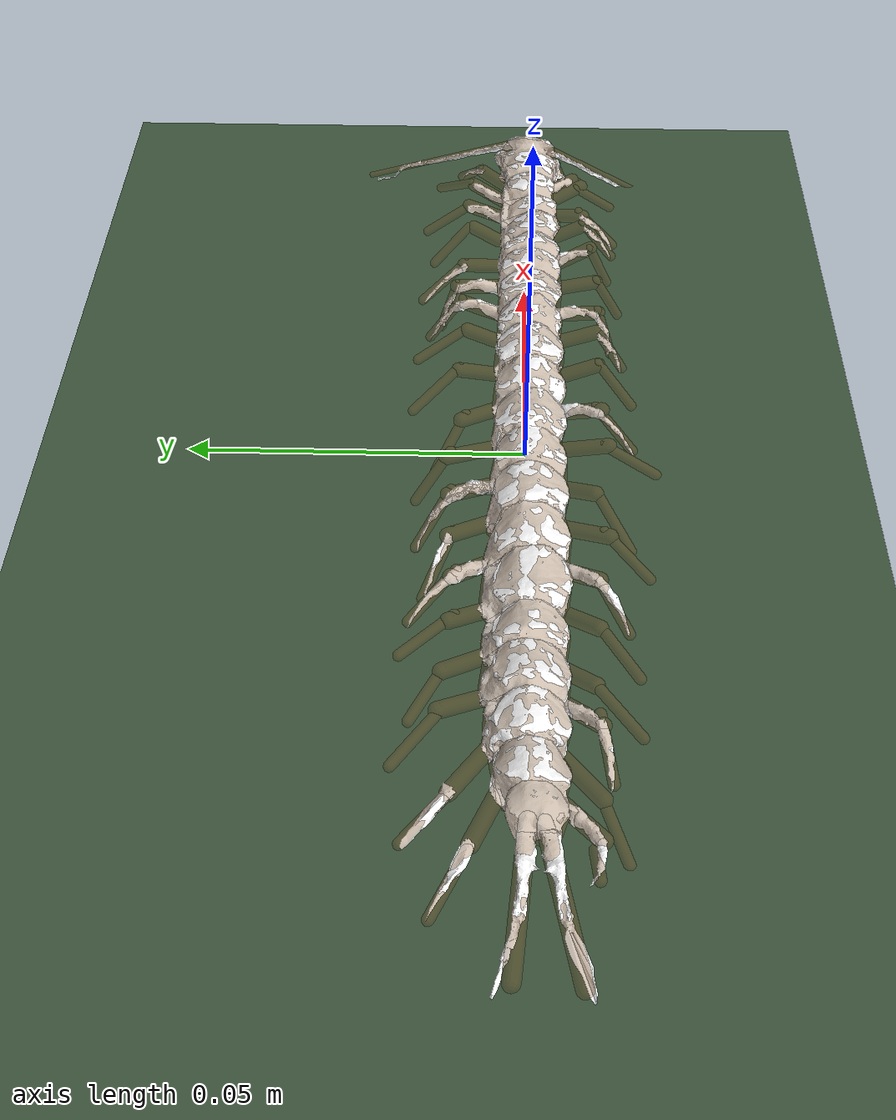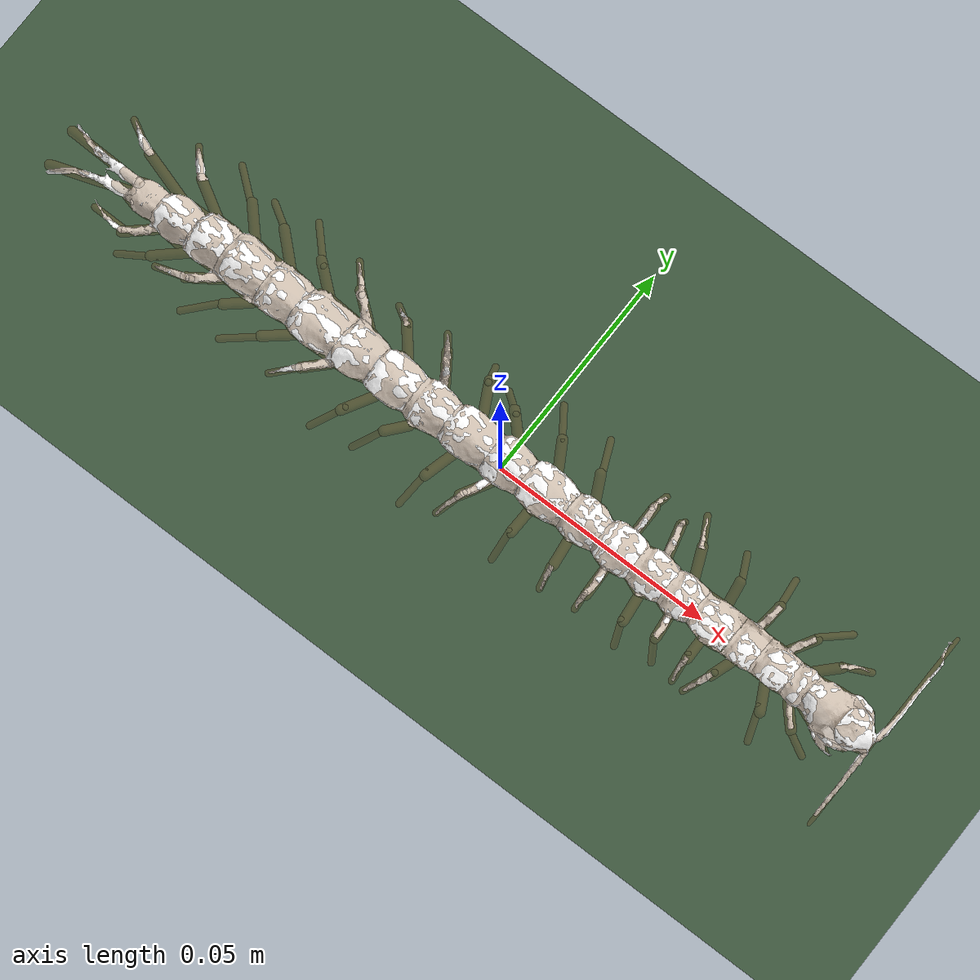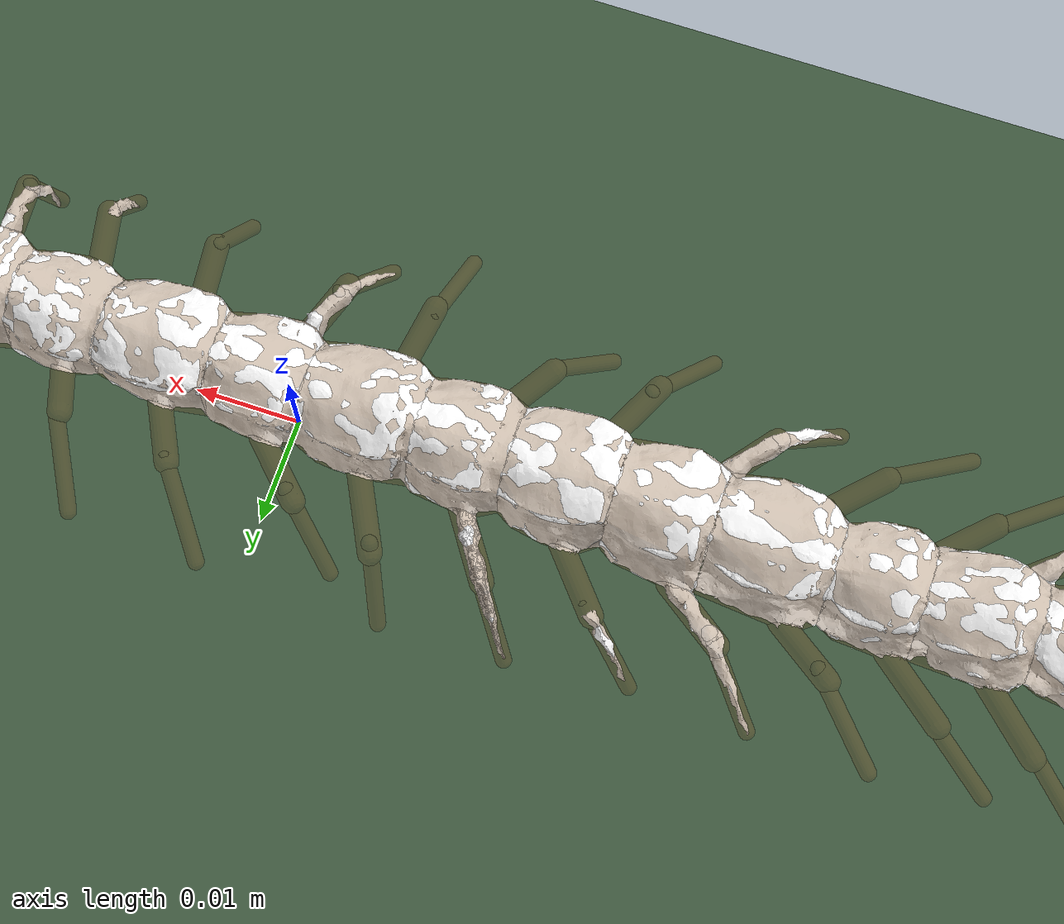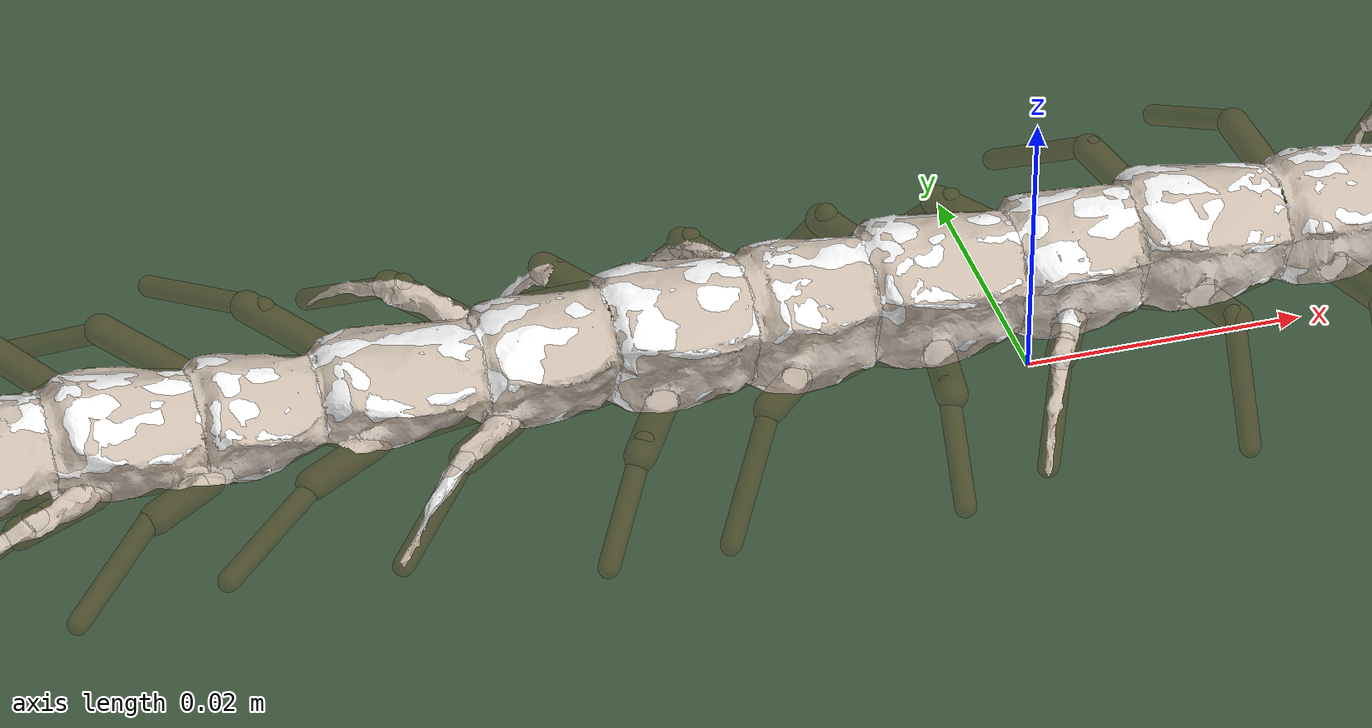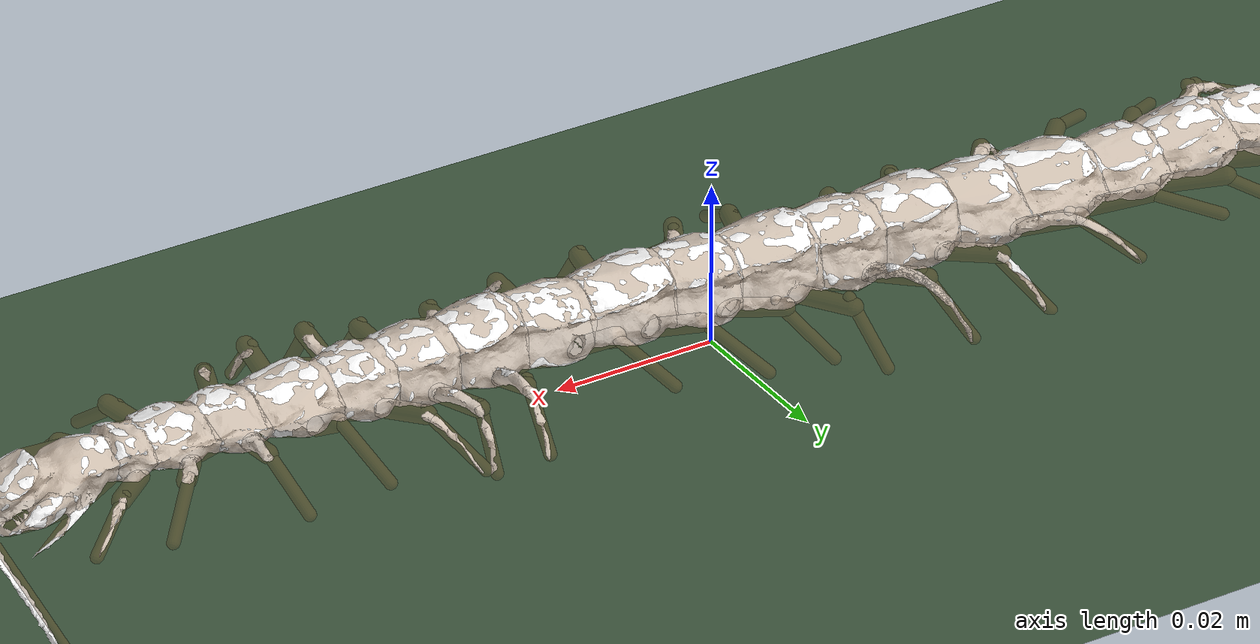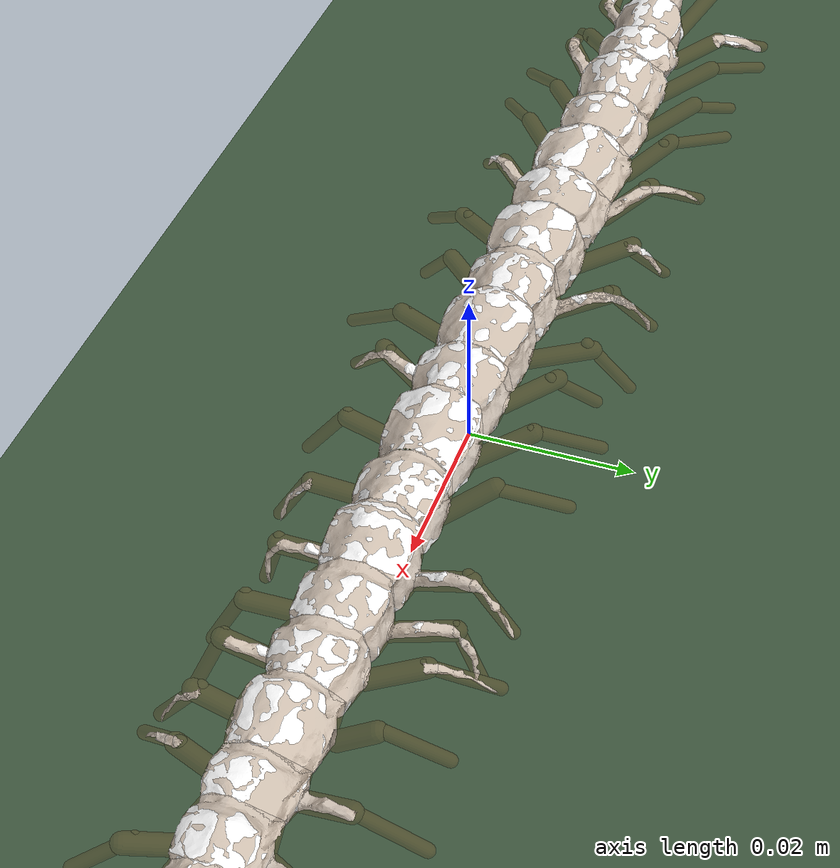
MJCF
<?xml version="1.0" ?>
<mujoco model="centipede_scolopendra">
  <compiler angle="radian" eulerseq="xyz" meshdir="." texturedir="textures" inertiafromgeom="auto" balanceinertia="true"/>
  <option timestep="0.0005" gravity="0 0 -9.81" integrator="implicitfast" cone="elliptic" impratio="10">
    <flag warmstart="enable" multiccd="enable"/>
  </option>
  <size nconmax="2000" njmax="4000"/>
  <visual>
    <map znear="0.0001" zfar="5.0" force="0.1"/>
    <quality shadowsize="4096"/>
  </visual>
  <default>
    <default class="body_joint">
      <joint type="hinge" damping="7.4107e-08" stiffness="0" armature="1.2348e-05"/>
    </default>
    <default class="leg_joint_0">
      <joint type="hinge" damping="3.5578e-07" stiffness="0" armature="2.3663e-08"/>
    </default>
    <default class="leg_joint_1">
      <joint type="hinge" damping="3.5578e-07" stiffness="0" armature="2.3663e-08"/>
    </default>
    <default class="leg_joint_2">
      <joint type="hinge" damping="0.00000213" stiffness="0" armature="2.3663e-08"/>
    </default>
    <default class="collision">
      <geom contype="1" conaffinity="0" condim="3" density="1050.00000000" friction="0.80000000 0.00500000 0.00010000" solref="0.11750000 1.00000000" solimp="0.90000000 0.95000000 0.00100000" group="2" rgba="0.5 0.3 0.1 0.3"/>
    </default>
    <default class="visual">
      <geom contype="0" conaffinity="0" group="1" mass="0" rgba="1 1 1 1"/>
    </default>
    <default class="foot">
      <geom type="sphere" size="0.00050000" contype="1" conaffinity="0" condim="3" density="0" friction="0.80000000 0.00500000 0.00010000" solref="0.11750000 1.00000000" solimp="0.90000000 0.95000000 0.00100000" group="3" rgba="0.8 0.6 0.3 1"/>
    </default>
  </default>
  <asset>
    <texture name="tex_body" type="2d" file="QS1167-W01-body_1.png"/>
    <material name="mat_body" texture="tex_body" texrepeat="1 1" texuniform="false" specular="0.3" shininess="0.3" emission="0.1"/>
    <texture name="tex_ashi" type="2d" file="ashi_3.png"/>
    <material name="mat_ashi" texture="tex_ashi" texrepeat="1 1" texuniform="false" specular="0.3" shininess="0.3" emission="0.1"/>
    <texture name="tex_tail" type="2d" file="tail_2.png"/>
    <material name="mat_tail" texture="tex_tail" texrepeat="1 1" texuniform="false" specular="0.3" shininess="0.3" emission="0.1"/>
    <texture name="tex_ground" type="2d" builtin="checker" rgb1="0.2 0.3 0.2" rgb2="0.3 0.4 0.3" width="300" height="300"/>
    <material name="mat_ground" texture="tex_ground" texrepeat="10 10" reflectance="0.1"/>
    <mesh name="vmesh_col_body_1_head_body" file="meshes/visual/body_1_head.001_body.obj"/>
    <mesh name="cmesh_col_body_1_head" file="meshes/collision/col_body_1_head.obj"/>
    <mesh name="vmesh_col_body_1_left_forcipules_body" file="meshes/visual/body_1_left_forcipules.001_body.obj"/>
    <mesh name="cmesh_col_body_1_left_forcipules" file="meshes/collision/col_body_1_left_forcipules.obj"/>
    <mesh name="vmesh_col_body_1_right_forcipules_body" file="meshes/visual/body_1_right_forcipules.001_body.obj"/>
    <mesh name="cmesh_col_body_1_right_forcipules" file="meshes/collision/col_body_1_right_forcipules.obj"/>
    <mesh name="vmesh_col_body_1_left_mandibles_body" file="meshes/visual/body_1_left_mandibles.001_body.obj"/>
    <mesh name="cmesh_col_body_1_left_mandibles" file="meshes/collision/col_body_1_left_mandibles.obj"/>
    <mesh name="vmesh_col_body_1_right_mandibles_body" file="meshes/visual/body_1_right_mandibles.001_body.obj"/>
    <mesh name="cmesh_col_body_1_right_mandibles" file="meshes/collision/col_body_1_right_mandibles.obj"/>
    <mesh name="vmesh_col_body_2_body" file="meshes/visual/body_2.001_body.obj"/>
    <mesh name="cmesh_col_body_2" file="meshes/collision/col_body_2.obj"/>
    <mesh name="vmesh_col_body_3_body" file="meshes/visual/body_3.001_body.obj"/>
    <mesh name="cmesh_col_body_3" file="meshes/collision/col_body_3.obj"/>
    <mesh name="vmesh_col_body_4_body" file="meshes/visual/body_4.001_body.obj"/>
    <mesh name="cmesh_col_body_4" file="meshes/collision/col_body_4.obj"/>
    <mesh name="vmesh_col_body_5_body" file="meshes/visual/body_5.001_body.obj"/>
    <mesh name="cmesh_col_body_5" file="meshes/collision/col_body_5.obj"/>
    <mesh name="vmesh_col_body_6_body" file="meshes/visual/body_6.001_body.obj"/>
    <mesh name="cmesh_col_body_6" file="meshes/collision/col_body_6.obj"/>
    <mesh name="vmesh_col_body_7_body" file="meshes/visual/body_7.001_body.obj"/>
    <mesh name="cmesh_col_body_7" file="meshes/collision/col_body_7.obj"/>
    <mesh name="vmesh_col_body_8_body" file="meshes/visual/body_8.001_body.obj"/>
    <mesh name="cmesh_col_body_8" file="meshes/collision/col_body_8.obj"/>
    <mesh name="vmesh_col_body_9_body" file="meshes/visual/body_9.001_body.obj"/>
    <mesh name="cmesh_col_body_9" file="meshes/collision/col_body_9.obj"/>
    <mesh name="vmesh_col_body_10_body" file="meshes/visual/body_10.001_body.obj"/>
    <mesh name="cmesh_col_body_10" file="meshes/collision/col_body_10.obj"/>
    <mesh name="vmesh_col_body_11_body" file="meshes/visual/body_11.001_body.obj"/>
    <mesh name="cmesh_col_body_11" file="meshes/collision/col_body_11.obj"/>
    <mesh name="vmesh_col_body_12_body" file="meshes/visual/body_12.001_body.obj"/>
    <mesh name="cmesh_col_body_12" file="meshes/collision/col_body_12.obj"/>
    <mesh name="vmesh_col_body_13_body" file="meshes/visual/body_13.001_body.obj"/>
    <mesh name="cmesh_col_body_13" file="meshes/collision/col_body_13.obj"/>
    <mesh name="vmesh_col_body_14_body" file="meshes/visual/body_14.001_body.obj"/>
    <mesh name="cmesh_col_body_14" file="meshes/collision/col_body_14.obj"/>
    <mesh name="vmesh_col_body_15_body" file="meshes/visual/body_15.001_body.obj"/>
    <mesh name="cmesh_col_body_15" file="meshes/collision/col_body_15.obj"/>
    <mesh name="vmesh_col_body_16_body" file="meshes/visual/body_16.001_body.obj"/>
    <mesh name="cmesh_col_body_16" file="meshes/collision/col_body_16.obj"/>
    <mesh name="vmesh_col_body_17_body" file="meshes/visual/body_17.001_body.obj"/>
    <mesh name="cmesh_col_body_17" file="meshes/collision/col_body_17.obj"/>
    <mesh name="vmesh_col_body_18_body" file="meshes/visual/body_18.001_body.obj"/>
    <mesh name="cmesh_col_body_18" file="meshes/collision/col_body_18.obj"/>
    <mesh name="vmesh_col_body_19_body" file="meshes/visual/body_19.001_body.obj"/>
    <mesh name="cmesh_col_body_19" file="meshes/collision/col_body_19.obj"/>
    <mesh name="vmesh_col_body_20_body" file="meshes/visual/body_20.001_body.obj"/>
    <mesh name="cmesh_col_body_20" file="meshes/collision/col_body_20.obj"/>
    <mesh name="vmesh_col_body_21_body" file="meshes/visual/body_21.001_body.obj"/>
    <mesh name="vmesh_col_body_21_tail" file="meshes/visual/body_21.001_tail.obj"/>
    <mesh name="cmesh_col_body_21" file="meshes/collision/col_body_21.obj"/>
    <mesh name="vmesh_col_left_antenna_body" file="meshes/visual/left_antenna_body.obj"/>
    <mesh name="vmesh_col_left_leg_1_body" file="meshes/visual/left_leg_1_body.obj"/>
    <mesh name="vmesh_col_left_leg_1.001_body" file="meshes/visual/left_leg_1.001_body.obj"/>
    <mesh name="vmesh_col_left_leg_2_body" file="meshes/visual/left_leg_2_body.obj"/>
    <mesh name="vmesh_col_left_leg_2.001_body" file="meshes/visual/left_leg_2.001_body.obj"/>
    <mesh name="vmesh_col_left_leg_3_body" file="meshes/visual/left_leg_3_body.obj"/>
    <mesh name="vmesh_col_left_leg_3.001_body" file="meshes/visual/left_leg_3.001_body.obj"/>
    <mesh name="vmesh_col_left_leg_4_body" file="meshes/visual/left_leg_4_body.obj"/>
    <mesh name="vmesh_col_left_leg_4.001_body" file="meshes/visual/left_leg_4.001_body.obj"/>
    <mesh name="vmesh_col_left_leg_5_body" file="meshes/visual/left_leg_5_body.obj"/>
    <mesh name="vmesh_col_left_leg_5.001_body" file="meshes/visual/left_leg_5.001_body.obj"/>
    <mesh name="vmesh_col_left_leg_6_body" file="meshes/visual/left_leg_6_body.obj"/>
    <mesh name="vmesh_col_left_leg_6.001_body" file="meshes/visual/left_leg_6.001_body.obj"/>
    <mesh name="vmesh_col_left_leg_7_body" file="meshes/visual/left_leg_7_body.obj"/>
    <mesh name="vmesh_col_left_leg_7.001_body" file="meshes/visual/left_leg_7.001_body.obj"/>
    <mesh name="vmesh_col_left_leg_8_body" file="meshes/visual/left_leg_8_body.obj"/>
    <mesh name="vmesh_col_left_leg_8.001_body" file="meshes/visual/left_leg_8.001_body.obj"/>
    <mesh name="vmesh_col_left_leg_9_body" file="meshes/visual/left_leg_9_body.obj"/>
    <mesh name="vmesh_col_left_leg_9.001_body" file="meshes/visual/left_leg_9.001_body.obj"/>
    <mesh name="vmesh_col_left_leg_10_body" file="meshes/visual/left_leg_10_body.obj"/>
    <mesh name="vmesh_col_left_leg_10.001_body" file="meshes/visual/left_leg_10.001_body.obj"/>
    <mesh name="vmesh_col_left_leg_11_body" file="meshes/visual/left_leg_11_body.obj"/>
    <mesh name="vmesh_col_left_leg_11.001_body" file="meshes/visual/left_leg_11.001_body.obj"/>
    <mesh name="vmesh_col_left_leg_12_body" file="meshes/visual/left_leg_12_body.obj"/>
    <mesh name="vmesh_col_left_leg_12.001_body" file="meshes/visual/left_leg_12.001_body.obj"/>
    <mesh name="vmesh_col_left_leg_13_body" file="meshes/visual/left_leg_13_body.obj"/>
    <mesh name="vmesh_col_left_leg_13.001_body" file="meshes/visual/left_leg_13.001_body.obj"/>
    <mesh name="vmesh_col_left_leg_14_body" file="meshes/visual/left_leg_14_body.obj"/>
    <mesh name="vmesh_col_left_leg_14.001_body" file="meshes/visual/left_leg_14.001_body.obj"/>
    <mesh name="vmesh_col_left_leg_15_body" file="meshes/visual/left_leg_15_body.obj"/>
    <mesh name="vmesh_col_left_leg_15.001_body" file="meshes/visual/left_leg_15.001_body.obj"/>
    <mesh name="vmesh_col_left_leg_16_body" file="meshes/visual/left_leg_16_body.obj"/>
    <mesh name="vmesh_col_left_leg_16.001_body" file="meshes/visual/left_leg_16.001_body.obj"/>
    <mesh name="vmesh_col_left_leg_17_body" file="meshes/visual/left_leg_17_body.obj"/>
    <mesh name="vmesh_col_left_leg_17.001_body" file="meshes/visual/left_leg_17.001_body.obj"/>
    <mesh name="vmesh_col_left_leg_18_body" file="meshes/visual/left_leg_18_body.obj"/>
    <mesh name="vmesh_col_left_leg_18.001_body" file="meshes/visual/left_leg_18.001_body.obj"/>
    <mesh name="vmesh_col_left_leg_19_body" file="meshes/visual/left_leg_19_body.obj"/>
    <mesh name="vmesh_col_left_leg_19.001_body" file="meshes/visual/left_leg_19.001_body.obj"/>
    <mesh name="vmesh_col_left_leg_ultimate_body" file="meshes/visual/left_leg_ultimate_body.obj"/>
    <mesh name="vmesh_col_right_antenna_body" file="meshes/visual/right_antenna_body.obj"/>
    <mesh name="vmesh_col_right_leg_1_body" file="meshes/visual/right_leg_1_body.obj"/>
    <mesh name="vmesh_col_right_leg_1.001_body" file="meshes/visual/right_leg_1.001_body.obj"/>
    <mesh name="vmesh_col_right_leg_2_body" file="meshes/visual/right_leg_2_body.obj"/>
    <mesh name="vmesh_col_right_leg_2.001_body" file="meshes/visual/right_leg_2.001_body.obj"/>
    <mesh name="vmesh_col_right_leg_3_body" file="meshes/visual/right_leg_3_body.obj"/>
    <mesh name="vmesh_col_right_leg_3.001_body" file="meshes/visual/right_leg_3.001_body.obj"/>
    <mesh name="vmesh_col_right_leg_4_body" file="meshes/visual/right_leg_4_body.obj"/>
    <mesh name="vmesh_col_right_leg_4.001_body" file="meshes/visual/right_leg_4.001_body.obj"/>
    <mesh name="vmesh_col_right_leg_5_body" file="meshes/visual/right_leg_5_body.obj"/>
    <mesh name="vmesh_col_right_leg_5.001_body" file="meshes/visual/right_leg_5.001_body.obj"/>
    <mesh name="vmesh_col_right_leg_6_body" file="meshes/visual/right_leg_6_body.obj"/>
    <mesh name="vmesh_col_right_leg_6.001_body" file="meshes/visual/right_leg_6.001_body.obj"/>
    <mesh name="vmesh_col_right_leg_7_body" file="meshes/visual/right_leg_7_body.obj"/>
    <mesh name="vmesh_col_right_leg_7.001_body" file="meshes/visual/right_leg_7.001_body.obj"/>
    <mesh name="vmesh_col_right_leg_8_body" file="meshes/visual/right_leg_8_body.obj"/>
    <mesh name="vmesh_col_right_leg_8.001_body" file="meshes/visual/right_leg_8.001_body.obj"/>
    <mesh name="vmesh_col_right_leg_9_body" file="meshes/visual/right_leg_9_body.obj"/>
    <mesh name="vmesh_col_right_leg_9.001_body" file="meshes/visual/right_leg_9.001_body.obj"/>
    <mesh name="vmesh_col_right_leg_10_body" file="meshes/visual/right_leg_10_body.obj"/>
    <mesh name="vmesh_col_right_leg_10.001_body" file="meshes/visual/right_leg_10.001_body.obj"/>
    <mesh name="vmesh_col_right_leg_11_body" file="meshes/visual/right_leg_11_body.obj"/>
    <mesh name="vmesh_col_right_leg_11.001_body" file="meshes/visual/right_leg_11.001_body.obj"/>
    <mesh name="vmesh_col_right_leg_12_body" file="meshes/visual/right_leg_12_body.obj"/>
    <mesh name="vmesh_col_right_leg_12.001_body" file="meshes/visual/right_leg_12.001_body.obj"/>
    <mesh name="vmesh_col_right_leg_13_body" file="meshes/visual/right_leg_13_body.obj"/>
    <mesh name="vmesh_col_right_leg_13.001_body" file="meshes/visual/right_leg_13.001_body.obj"/>
    <mesh name="vmesh_col_right_leg_14_body" file="meshes/visual/right_leg_14_body.obj"/>
    <mesh name="vmesh_col_right_leg_14.001_body" file="meshes/visual/right_leg_14.001_body.obj"/>
    <mesh name="vmesh_col_right_leg_15_body" file="meshes/visual/right_leg_15_body.obj"/>
    <mesh name="vmesh_col_right_leg_15.001_body" file="meshes/visual/right_leg_15.001_body.obj"/>
    <mesh name="vmesh_col_right_leg_16_body" file="meshes/visual/right_leg_16_body.obj"/>
    <mesh name="vmesh_col_right_leg_16.001_body" file="meshes/visual/right_leg_16.001_body.obj"/>
    <mesh name="vmesh_col_right_leg_17_body" file="meshes/visual/right_leg_17_body.obj"/>
    <mesh name="vmesh_col_right_leg_17.001_body" file="meshes/visual/right_leg_17.001_body.obj"/>
    <mesh name="vmesh_col_right_leg_18_body" file="meshes/visual/right_leg_18_body.obj"/>
    <mesh name="vmesh_col_right_leg_18.001_body" file="meshes/visual/right_leg_18.001_body.obj"/>
    <mesh name="vmesh_col_right_leg_19_body" file="meshes/visual/right_leg_19_body.obj"/>
    <mesh name="vmesh_col_right_leg_19_ashi" file="meshes/visual/right_leg_19_ashi.obj"/>
    <mesh name="vmesh_col_right_leg_19.001_body" file="meshes/visual/right_leg_19.001_body.obj"/>
    <mesh name="vmesh_col_right_leg_19.001_ashi" file="meshes/visual/right_leg_19.001_ashi.obj"/>
    <mesh name="vmesh_col_right_leg_ultimate_body" file="meshes/visual/right_leg_ultimate_body.obj"/>
    <mesh name="vmesh_col_right_leg_ultimate_tail" file="meshes/visual/right_leg_ultimate_tail.obj"/>
  </asset>
  <worldbody>
    <light name="top_light" pos="0 0 0.5" dir="0 0 -1" mode="trackcom" diffuse="0.8 0.8 0.8" specular="0.3 0.3 0.3" castshadow="true"/>
    <geom name="ground" type="plane" size="1 1 0.01" pos="0 0 0" material="mat_ground" contype="0" conaffinity="1" condim="3" friction="0.80000000 0.00500000 0.00010000"/>
    <body name="b0" pos="0.08390662 -0.00074569 0.00877781" quat="0.00288483 0.01069690 -0.00003086 0.99993862">
      <freejoint name="root"/>
      <geom name="colg_col_body_1_head" type="mesh" mesh="cmesh_col_body_1_head" pos="0.08387368 -0.00026154 -0.00257269" quat="0.00288483 -0.01069690 0.00003086 -0.99993862" class="collision"/>
      <geom name="vis_col_body_1_head" type="mesh" mesh="vmesh_col_body_1_head_body" pos="0.08387368 -0.00026154 -0.00257269" quat="0.00288483 -0.01069690 0.00003086 -0.99993862" material="mat_body" class="visual"/>
      <site name="sb0" pos="0 0 0" size="0.001" group="4"/>
      <body name="antL" pos="-0.00813407 -0.00117969 -0.00059894" quat="0.70313958 0.08378837 0.09958055 -0.69904074">
        <joint name="jantLy" axis="0 0 1" type="hinge" range="-1.57080000 1.57080000" limited="true" damping="1e-7"/>
        <joint name="jantLp" axis="0 1 0" type="hinge" range="-1.57080000 1.57080000" limited="true" damping="1e-7"/>
        <geom name="cantL" type="capsule" fromto="0.00000000 0.00000000 0.00000000 0.02789271 -1.5450e-18 8.6736e-19" size="0.00049000" class="collision"/>
        <geom name="vis_col_left_antenna" type="mesh" mesh="vmesh_col_left_antenna_body" pos="-0.00011729 0.09203342 -0.00003637" quat="0.70013307 0.09178973 -0.09152638 -0.70214760" material="mat_body" class="visual"/>
        <site name="santL" pos="0.02789271 -1.5450e-18 8.6736e-19" size="0.0002" group="4"/>
      </body>
      <body name="antR" pos="-0.00771332 0.00265108 -0.00130006" quat="0.70073709 -0.14874378 0.16980550 0.67676356">
        <joint name="jantRy" axis="0 0 1" type="hinge" range="-1.57080000 1.57080000" limited="true" damping="1e-7"/>
        <joint name="jantRp" axis="0 1 0" type="hinge" range="-1.57080000 1.57080000" limited="true" damping="1e-7"/>
        <geom name="cantR" type="capsule" fromto="0.00000000 0.00000000 0.00000000 0.02656158 -1.1907e-18 0.00000000" size="0.00049000" class="collision"/>
        <geom name="vis_col_right_antenna" type="mesh" mesh="vmesh_col_right_antenna_body" pos="0.00035373 -0.09163667 0.00093708" quat="0.67310417 -0.16274935 -0.15550569 0.70445823" material="mat_body" class="visual"/>
        <site name="santR" pos="0.02656158 -1.1907e-18 0.00000000" size="0.0002" group="4"/>
      </body>
      <body name="frcL" pos="0.00039692 -0.00453852 -0.00436169" quat="0.24958193 -0.55090907 0.77035644 0.20188861">
        <joint name="jfrcL" axis="0 1 0" type="hinge" range="-1.0 1.0" limited="true" damping="1e-6"/>
        <geom name="colg_col_body_1_left_forcipules" type="mesh" mesh="cmesh_col_body_1_left_forcipules" pos="-0.02669165 -0.07787018 0.01461693" quat="0.19523942 -0.76923492 -0.55082020 0.25837245" class="collision"/>
        <geom name="vis_col_body_1_left_forcipules" type="mesh" mesh="vmesh_col_body_1_left_forcipules_body" pos="-0.02669165 -0.07787018 0.01461693" quat="0.19523942 -0.76923492 -0.55082020 0.25837245" material="mat_body" class="visual"/>
        <body name="mndL" pos="-0.00185853 0.00253658 -0.00162601" quat="0.94963605 0.00254831 0.11871590 0.28998518">
          <joint name="jmndL" axis="0 0 1" type="hinge" range="-0.5 0.5" limited="true" damping="1e-7"/>
          <geom name="colg_col_body_1_left_mandibles" type="mesh" mesh="cmesh_col_body_1_left_mandibles" pos="-0.06792853 -0.05202363 0.00500198" quat="0.19297921 -0.92139335 -0.32253160 0.09882650" class="collision"/>
          <geom name="vis_col_body_1_left_mandibles" type="mesh" mesh="vmesh_col_body_1_left_mandibles_body" pos="-0.06792853 -0.05202363 0.00500198" quat="0.19297921 -0.92139335 -0.32253160 0.09882650" material="mat_body" class="visual"/>
        </body>
      </body>
      <body name="frcR" pos="0.00091923 0.00556416 -0.00398946" quat="0.07378171 -0.63294583 0.73143880 0.24276143">
        <joint name="jfrcR" axis="0 1 0" type="hinge" range="-1.0 1.0" limited="true" damping="1e-6"/>
        <geom name="colg_col_body_1_right_forcipules" type="mesh" mesh="cmesh_col_body_1_right_forcipules" pos="-0.01098764 -0.07988148 -0.02038649" quat="0.23574055 -0.73243811 -0.63339598 0.08228211" class="collision"/>
        <geom name="vis_col_body_1_right_forcipules" type="mesh" mesh="vmesh_col_body_1_right_forcipules_body" pos="-0.01098764 -0.07988148 -0.02038649" quat="0.23574055 -0.73243811 -0.63339598 0.08228211" material="mat_body" class="visual"/>
        <body name="mndR" pos="0.00217794 0.00312643 -0.00197286" quat="0.59379574 0.41595144 0.14072937 0.67423013">
          <joint name="jmndR" axis="0 0 1" type="hinge" range="-0.5 0.5" limited="true" damping="1e-7"/>
          <geom name="colg_col_body_1_right_mandibles" type="mesh" mesh="cmesh_col_body_1_right_mandibles" pos="-0.08410821 0.01759411 0.00435461" quat="-0.19833730 -0.97160941 0.11877375 0.05030180" class="collision"/>
          <geom name="vis_col_body_1_right_mandibles" type="mesh" mesh="vmesh_col_body_1_right_mandibles_body" pos="-0.08410821 0.01759411 0.00435461" quat="-0.19833730 -0.97160941 0.11877375 0.05030180" material="mat_body" class="visual"/>
        </body>
      </body>
      <body name="b1" pos="0.00795632 -2.7105e-20 -2.7105e-20" quat="0.99984965 -0.00040027 -0.01278633 -0.01170548">
        <joint name="jb1" axis="0 0 1" range="-0.62800000 0.62800000" limited="true" class="body_joint"/>
        <geom name="colg_col_body_2" type="mesh" mesh="cmesh_col_body_2" pos="0.07581205 0.00151763 -0.00451254" quat="0.01459305 -0.02348004 0.00034278 -0.99961773" class="collision"/>
        <geom name="vis_col_body_2" type="mesh" mesh="vmesh_col_body_2_body" pos="0.07581205 0.00151763 -0.00451254" quat="0.01459305 -0.02348004 0.00034278 -0.99961773" material="mat_body" class="visual"/>
        <site name="sb1" pos="0.00215551 0.00005051 -0.00005513" size="0.0005" group="4"/>
        <body name="l1L" pos="0.00241045 -0.00357249 -0.00124725" quat="0.39315935 -0.07995338 -0.01577781 -0.91585165">
          <joint name="jl1L0" axis="0 0 -1" range="-1.57080000 1.57080000" limited="true" class="leg_joint_0"/>
          <joint name="jl1L1" axis="0 1 0" range="-2.09440000 2.09440000" limited="true" class="leg_joint_1"/>
          <geom name="cl1Lu" type="capsule" fromto="0.00636016 -8.6736e-19 -2.1684e-19 0.00000000 0.00000000 0.00000000" size="0.00111000" class="collision"/>
          <geom name="vis_col_left_leg_1.001" type="mesh" mesh="vmesh_col_left_leg_1.001_body" pos="-0.05394268 0.04964239 0.00708428" quat="0.92311085 -0.02415035 0.05878359 -0.37924612" material="mat_body" class="visual"/>
          <site name="sl1L" pos="0 0 0" size="0.0003" group="4"/>
          <body name="l1Ll" pos="0.00616992 0.00024312 0.00040511" quat="0.93802109 0.02051790 0.33280792 -0.09452167">
            <joint name="jl1L2" axis="0 1 0" range="-2.09440000 2.09440000" limited="true" class="leg_joint_2"/>
            <geom name="cl1Ll" type="capsule" fromto="0.00742793 9.7595e-19 -4.3368e-19 0.00000000 0.00000000 0.00000000" size="0.00075000" class="collision"/>
            <geom name="vis_col_left_leg_1" type="mesh" mesh="vmesh_col_left_leg_1_body" pos="-0.05800348 0.03683132 -0.03711434" quat="0.92081254 0.07906596 -0.26214242 -0.27773042" material="mat_body" class="visual"/>
            <body name="f1L" pos="0.00742793 9.7595e-19 -4.3368e-19">
              <geom name="gf1L" class="foot"/>
              <site name="sf1L" pos="0 0 0" size="0.0002" group="4"/>
              <inertial pos="0 0 0" mass="1.0000e-08" diaginertia="1.0000e-15 1.0000e-15 1.0000e-15"/>
            </body>
          </body>
        </body>
        <body name="l1R" pos="0.00194826 0.00362457 -0.00219797" quat="0.38966568 0.06521197 -0.00931576 0.91859745">
          <joint name="jl1R0" axis="0 0 1" range="-1.57080000 1.57080000" limited="true" class="leg_joint_0"/>
          <joint name="jl1R1" axis="0 1 0" range="-2.09440000 2.09440000" limited="true" class="leg_joint_1"/>
          <geom name="cl1Ru" type="capsule" fromto="0.00000000 0.00000000 0.00000000 0.00554326 4.3732e-19 0.00000000" size="0.00111000" class="collision"/>
          <geom name="vis_col_right_leg_1.001" type="mesh" mesh="vmesh_col_right_leg_1.001_body" pos="-0.05260460 -0.05157950 0.00616181" quat="0.91409427 0.01909833 0.04334882 0.40272547" material="mat_body" class="visual"/>
          <site name="sl1R" pos="0 0 0" size="0.0003" group="4"/>
          <body name="l1Rl" pos="0.00567500 -0.00019375 0.00017170" quat="0.91031886 -0.05789345 0.35620341 0.20269941">
            <joint name="jl1R2" axis="0 1 0" range="-2.09440000 2.09440000" limited="true" class="leg_joint_2"/>
            <geom name="cl1Rl" type="capsule" fromto="0.00615899 8.6736e-19 8.6736e-19 0.00000000 0.00000000 0.00000000" size="0.00075000" class="collision"/>
            <geom name="vis_col_right_leg_1" type="mesh" mesh="vmesh_col_right_leg_1_body" pos="-0.05957083 -0.02267380 -0.04483416" quat="0.92808480 -0.06435976 -0.31332863 0.19063473" material="mat_body" class="visual"/>
            <body name="f1R" pos="0.00615899 8.6736e-19 8.6736e-19">
              <geom name="gf1R" class="foot"/>
              <site name="sf1R" pos="0 0 0" size="0.0002" group="4"/>
              <inertial pos="0 0 0" mass="1.0000e-08" diaginertia="1.0000e-15 1.0000e-15 1.0000e-15"/>
            </body>
          </body>
        </body>
        <body name="b2" pos="0.00430613 0.00005051 -0.00005513" quat="0.99907152 0.00020187 0.03746333 0.02127353">
          <joint name="jb2" axis="0 0 1" range="-0.62800000 0.62800000" limited="true" class="body_joint"/>
          <geom name="colg_col_body_3" type="mesh" mesh="cmesh_col_body_3" pos="0.07163650 -0.00158157 0.00091019" quat="0.00667780 -0.01399511 -0.00009347 0.99987976" class="collision"/>
          <geom name="vis_col_body_3" type="mesh" mesh="vmesh_col_body_3_body" pos="0.07163650 -0.00158157 0.00091019" quat="0.00667780 -0.01399511 -0.00009347 0.99987976" material="mat_body" class="visual"/>
          <site name="sb2" pos="0.00380968 -0.00016249 0.00028628" size="0.0005" group="4"/>
          <body name="l2L" pos="0.00400297 -0.00415286 -0.00106007" quat="0.47017526 -0.09667058 -0.06532210 -0.87482744">
            <joint name="jl2L0" axis="0 0 -1" range="-1.57080000 1.57080000" limited="true" class="leg_joint_0"/>
            <joint name="jl2L1" axis="0 1 0" range="-2.09440000 2.09440000" limited="true" class="leg_joint_1"/>
            <geom name="cl2Lu" type="capsule" fromto="0.00000000 0.00000000 0.00000000 0.00641278 -2.1903e-18 -8.6736e-19" size="0.00111000" class="collision"/>
            <geom name="vis_col_left_leg_2.001" type="mesh" mesh="vmesh_col_left_leg_2.001_body" pos="-0.03809516 0.05512610 0.00972935" quat="0.87022349 -0.05946140 0.10851000 -0.47686581" material="mat_body" class="visual"/>
            <site name="sl2L" pos="0 0 0" size="0.0003" group="4"/>
            <body name="l2Ll" pos="0.00656720 0.00028685 0.00031305" quat="0.93868431 0.00775674 0.33484346 -0.08180133">
              <joint name="jl2L2" axis="0 1 0" range="-2.09440000 2.09440000" limited="true" class="leg_joint_2"/>
              <geom name="cl2Ll" type="capsule" fromto="0.00000000 0.00000000 0.00000000 0.00817833 -3.3757e-19 4.3368e-19" size="0.00075000" class="collision"/>
              <geom name="vis_col_left_leg_2" type="mesh" mesh="vmesh_col_left_leg_2_body" pos="-0.04811767 0.04662917 -0.02451827" quat="0.89174603 0.08823356 -0.19809496 -0.39719296" material="mat_body" class="visual"/>
              <body name="f2L" pos="0.00817833 -3.3757e-19 4.3368e-19">
                <geom name="gf2L" class="foot"/>
                <site name="sf2L" pos="0 0 0" size="0.0002" group="4"/>
                <inertial pos="0 0 0" mass="1.0000e-08" diaginertia="1.0000e-15 1.0000e-15 1.0000e-15"/>
              </body>
            </body>
          </body>
          <body name="l2R" pos="0.00454116 0.00184653 -0.00182774" quat="0.52047709 0.10511396 -0.07970134 0.84362453">
            <joint name="jl2R0" axis="0 0 1" range="-1.57080000 1.57080000" limited="true" class="leg_joint_0"/>
            <joint name="jl2R1" axis="0 1 0" range="-2.09440000 2.09440000" limited="true" class="leg_joint_1"/>
            <geom name="cl2Ru" type="capsule" fromto="0.00827269 3.1276e-20 0.00000000 0.00000000 0.00000000 0.00000000" size="0.00111000" class="collision"/>
            <geom name="vis_col_right_leg_2.001" type="mesh" mesh="vmesh_col_right_leg_2.001_body" pos="-0.03150120 -0.05858700 0.00981173" quat="0.84553511 0.07162684 0.11739152 0.51590620" material="mat_body" class="visual"/>
            <site name="sl2R" pos="0 0 0" size="0.0003" group="4"/>
            <body name="l2Rl" pos="0.00715943 -0.00032981 0.00035702" quat="0.89774555 0.01327806 0.43380304 -0.07544228">
              <joint name="jl2R2" axis="0 1 0" range="-2.09440000 2.09440000" limited="true" class="leg_joint_2"/>
              <geom name="cl2Rl" type="capsule" fromto="0.00000000 0.00000000 0.00000000 0.00784696 -2.1684e-19 0.00000000" size="0.00075000" class="collision"/>
              <geom name="vis_col_right_leg_2" type="mesh" mesh="vmesh_col_right_leg_2_body" pos="-0.02383281 -0.06364914 -0.01893993" quat="0.77203010 -0.17958235 -0.24915407 0.55645481" material="mat_body" class="visual"/>
              <body name="f2R" pos="0.00784696 -2.1684e-19 0.00000000">
                <geom name="gf2R" class="foot"/>
                <site name="sf2R" pos="0 0 0" size="0.0002" group="4"/>
                <inertial pos="0 0 0" mass="1.0000e-08" diaginertia="1.0000e-15 1.0000e-15 1.0000e-15"/>
              </body>
            </body>
          </body>
          <body name="b3" pos="0.00763101 -0.00016249 0.00028628" quat="0.99966206 -0.00003839 -0.02407406 0.00980786">
            <joint name="jb3" axis="0 0 1" range="-0.62800000 0.62800000" limited="true" class="body_joint"/>
            <geom name="colg_col_body_4" type="mesh" mesh="cmesh_col_body_4" pos="0.06392118 -0.00267413 -0.00245700" quat="0.01648501 0.01008013 0.00016620 0.99981329" class="collision"/>
            <geom name="vis_col_body_4" type="mesh" mesh="vmesh_col_body_4_body" pos="0.06392118 -0.00267413 -0.00245700" quat="0.01648501 0.01008013 0.00016620 0.99981329" material="mat_body" class="visual"/>
            <site name="sb3" pos="0.00303613 -0.00005961 -0.00014633" size="0.0005" group="4"/>
            <body name="l3L" pos="0.00317856 -0.00466467 -0.00071919" quat="0.63708711 -0.11689151 -0.08525030 -0.75709231">
              <joint name="jl3L0" axis="0 0 -1" range="-1.57080000 1.57080000" limited="true" class="leg_joint_0"/>
              <joint name="jl3L1" axis="0 1 0" range="-2.09440000 2.09440000" limited="true" class="leg_joint_1"/>
              <geom name="cl3Lu" type="capsule" fromto="0.00568929 -1.1926e-18 -2.1684e-19 0.00000000 0.00000000 0.00000000" size="0.00111000" class="collision"/>
              <geom name="vis_col_left_leg_3.001" type="mesh" mesh="vmesh_col_left_leg_3.001_body" pos="-0.01215116 0.05949577 0.00304143" quat="0.74764102 -0.09345743 0.10772686 -0.64860893" material="mat_body" class="visual"/>
              <site name="sl3L" pos="0 0 0" size="0.0003" group="4"/>
              <body name="l3Ll" pos="0.00589544 0.00014970 -0.00028227" quat="0.90399772 -0.01928332 0.40158504 0.14541573">
                <joint name="jl3L2" axis="0 1 0" range="-2.09440000 2.09440000" limited="true" class="leg_joint_2"/>
                <geom name="cl3Ll" type="capsule" fromto="0.00784969 2.1684e-19 8.6736e-19 0.00000000 0.00000000 0.00000000" size="0.00075000" class="collision"/>
                <geom name="vis_col_left_leg_3" type="mesh" mesh="vmesh_col_left_leg_3_body" pos="0.00078913 0.06208856 -0.00175229" quat="0.62661150 0.20606853 -0.17675909 -0.73051353" material="mat_body" class="visual"/>
                <body name="f3L" pos="0.00784969 2.1684e-19 8.6736e-19">
                  <geom name="gf3L" class="foot"/>
                  <site name="sf3L" pos="0 0 0" size="0.0002" group="4"/>
                  <inertial pos="0 0 0" mass="1.0000e-08" diaginertia="1.0000e-15 1.0000e-15 1.0000e-15"/>
                </body>
              </body>
            </body>
            <body name="l3R" pos="0.00346288 0.00363575 -0.00024153" quat="0.81504616 0.04057287 -0.04086426 0.57652728">
              <joint name="jl3R0" axis="0 0 1" range="-1.57080000 1.57080000" limited="true" class="leg_joint_0"/>
              <joint name="jl3R1" axis="0 1 0" range="-2.09440000 2.09440000" limited="true" class="leg_joint_1"/>
              <geom name="cl3Ru" type="capsule" fromto="0.00000000 0.00000000 0.00000000 0.00559774 1.9749e-18 0.00000000" size="0.00111000" class="collision"/>
              <geom name="vis_col_right_leg_3.001" type="mesh" mesh="vmesh_col_right_leg_3.001_body" pos="0.01390539 -0.05915538 -0.00268502" quat="0.59025787 0.04849938 0.03556293 0.80497127" material="mat_body" class="visual"/>
              <site name="sl3R" pos="0 0 0" size="0.0003" group="4"/>
              <body name="l3Rl" pos="0.00496029 0.00005837 0.00075917" quat="0.93008387 0.02377946 0.35382141 -0.09585893">
                <joint name="jl3R2" axis="0 1 0" range="-2.09440000 2.09440000" limited="true" class="leg_joint_2"/>
                <geom name="cl3Rl" type="capsule" fromto="0.00793477 -2.5113e-19 4.3368e-19 0.00000000 0.00000000 0.00000000" size="0.00075000" class="collision"/>
                <geom name="vis_col_right_leg_3" type="mesh" mesh="vmesh_col_right_leg_3_body" pos="0.01838581 -0.05623172 0.00990460" quat="0.48556186 -0.25715262 -0.15197848 0.82158673" material="mat_body" class="visual"/>
                <body name="f3R" pos="0.00793477 -2.5113e-19 4.3368e-19">
                  <geom name="gf3R" class="foot"/>
                  <site name="sf3R" pos="0 0 0" size="0.0002" group="4"/>
                  <inertial pos="0 0 0" mass="1.0000e-08" diaginertia="1.0000e-15 1.0000e-15 1.0000e-15"/>
                </body>
              </body>
            </body>
            <body name="b4" pos="0.00622663 -0.00005961 -0.00014633" quat="0.99931832 -0.00021345 0.01391275 -0.03419479">
              <joint name="jb4" axis="0 0 1" range="-0.62800000 0.62800000" limited="true" class="body_joint"/>
              <geom name="colg_col_body_5" type="mesh" mesh="cmesh_col_body_5" pos="0.05778021 0.00133746 -0.00070327" quat="0.01771447 0.00383906 -0.00006802 -0.99983571" class="collision"/>
              <geom name="vis_col_body_5" type="mesh" mesh="vmesh_col_body_5_body" pos="0.05778021 0.00133746 -0.00070327" quat="0.01771447 0.00383906 -0.00006802 -0.99983571" material="mat_body" class="visual"/>
              <site name="sb4" pos="0.00450835 0.00030893 0.00012577" size="0.0005" group="4"/>
              <body name="l4L" pos="0.00512622 -0.00490627 -0.00094787" quat="0.72669581 -0.17569022 -0.20851242 -0.63053051">
                <joint name="jl4L0" axis="0 0 -1" range="-1.57080000 1.57080000" limited="true" class="leg_joint_0"/>
                <joint name="jl4L1" axis="0 1 0" range="-2.09440000 2.09440000" limited="true" class="leg_joint_1"/>
                <geom name="cl4Lu" type="capsule" fromto="0.00485370 -7.8047e-19 0.00000000 0.00000000 0.00000000 0.00000000" size="0.00111000" class="collision"/>
                <geom name="vis_col_left_leg_4.001" type="mesh" mesh="vmesh_col_left_leg_4.001_body" pos="0.00107229 0.05300584 -0.00084668" quat="0.64263965 -0.20253319 0.18172625 -0.71621935" material="mat_body" class="visual"/>
                <site name="sl4L" pos="0 0 0" size="0.0003" group="4"/>
                <body name="l4Ll" pos="0.00555367 -0.00000965 -0.00025311" quat="0.79621479 -0.01346279 0.58016222 0.17109225">
                  <joint name="jl4L2" axis="0 1 0" range="-2.09440000 2.09440000" limited="true" class="leg_joint_2"/>
                  <geom name="cl4Ll" type="capsule" fromto="0.00000000 0.00000000 0.00000000 0.00824324 2.0324e-18 1.7347e-18" size="0.00075000" class="collision"/>
                  <geom name="vis_col_left_leg_4" type="mesh" mesh="vmesh_col_left_leg_4_body" pos="0.01296488 0.05107833 0.00734801" quat="0.49729698 0.29400717 -0.18384794 -0.79527067" material="mat_body" class="visual"/>
                  <body name="f4L" pos="0.00824324 2.0324e-18 1.7347e-18">
                    <geom name="gf4L" class="foot"/>
                    <site name="sf4L" pos="0 0 0" size="0.0002" group="4"/>
                    <inertial pos="0 0 0" mass="1.0000e-08" diaginertia="1.0000e-15 1.0000e-15 1.0000e-15"/>
                  </body>
                </body>
              </body>
              <body name="l4R" pos="0.00454474 0.00353887 -0.00072892" quat="0.65946612 0.14861168 -0.14077775 0.72332609">
                <joint name="jl4R0" axis="0 0 1" range="-1.57080000 1.57080000" limited="true" class="leg_joint_0"/>
                <joint name="jl4R1" axis="0 1 0" range="-2.09440000 2.09440000" limited="true" class="leg_joint_1"/>
                <geom name="cl4Ru" type="capsule" fromto="0.00000000 0.00000000 0.00000000 0.00665703 3.4520e-19 0.00000000" size="0.00111000" class="collision"/>
                <geom name="vis_col_right_leg_4.001" type="mesh" mesh="vmesh_col_right_leg_4.001_body" pos="-0.00657807 -0.05281591 0.00246382" quat="0.71094506 0.14090467 0.14891520 0.67270146" material="mat_body" class="visual"/>
                <site name="sl4R" pos="0 0 0" size="0.0003" group="4"/>
                <body name="l4Rl" pos="0.00607194 -0.00025320 0.00057821" quat="0.79478040 0.00601060 0.60636481 -0.02469235">
                  <joint name="jl4R2" axis="0 1 0" range="-2.09440000 2.09440000" limited="true" class="leg_joint_2"/>
                  <geom name="cl4Rl" type="capsule" fromto="0.00000000 0.00000000 0.00000000 0.00779282 -3.9641e-19 4.3368e-19" size="0.00075000" class="collision"/>
                  <geom name="vis_col_right_leg_4" type="mesh" mesh="vmesh_col_right_leg_4_body" pos="-0.00347038 -0.05312198 -0.00961394" quat="0.63957848 -0.30386450 -0.30521457 0.63674940" material="mat_body" class="visual"/>
                  <body name="f4R" pos="0.00779282 -3.9641e-19 4.3368e-19">
                    <geom name="gf4R" class="foot"/>
                    <site name="sf4R" pos="0 0 0" size="0.0002" group="4"/>
                    <inertial pos="0 0 0" mass="1.0000e-08" diaginertia="1.0000e-15 1.0000e-15 1.0000e-15"/>
                  </body>
                </body>
              </body>
              <body name="b5" pos="0.00890111 0.00030893 0.00012577" quat="0.99973322 -0.00028569 0.00498775 0.02255050">
                <joint name="jb5" axis="0 0 1" range="-0.62800000 0.62800000" limited="true" class="body_joint"/>
                <geom name="colg_col_body_6" type="mesh" mesh="cmesh_col_body_6" pos="0.04888160 -0.00117628 -0.00034135" quat="0.00483849 -0.00882849 -0.00004272 0.99994932" class="collision"/>
                <geom name="vis_col_body_6" type="mesh" mesh="vmesh_col_body_6_body" pos="0.04888160 -0.00117628 -0.00034135" quat="0.00483849 -0.00882849 -0.00004272 0.99994932" material="mat_body" class="visual"/>
                <site name="sb5" pos="0.00349004 -0.00015754 0.00003480" size="0.0005" group="4"/>
                <body name="l5L" pos="0.00423254 -0.00483991 -0.00136192" quat="0.82508203 -0.05399013 -0.09509449 -0.55432999">
                  <joint name="jl5L0" axis="0 0 -1" range="-1.57080000 1.57080000" limited="true" class="leg_joint_0"/>
                  <joint name="jl5L1" axis="0 1 0" range="-2.09440000 2.09440000" limited="true" class="leg_joint_1"/>
                  <geom name="cl5Lu" type="capsule" fromto="0.00644495 -7.7333e-19 -6.5052e-19 0.00000000 0.00000000 0.00000000" size="0.00111000" class="collision"/>
                  <geom name="vis_col_left_leg_5.001" type="mesh" mesh="vmesh_col_left_leg_5.001_body" pos="0.01330946 0.04270795 -0.00262504" quat="0.54982904 -0.08809035 0.05845643 -0.82855957" material="mat_body" class="visual"/>
                  <site name="sl5L" pos="0 0 0" size="0.0003" group="4"/>
                  <body name="l5Ll" pos="0.00621682 -0.00001156 0.00041653" quat="0.92263662 -0.00802680 0.38310451 0.04368263">
                    <joint name="jl5L2" axis="0 1 0" range="-2.09440000 2.09440000" limited="true" class="leg_joint_2"/>
                    <geom name="cl5Ll" type="capsule" fromto="0.00000000 0.00000000 0.00000000 0.00921865 -1.3921e-19 0.00000000" size="0.00075000" class="collision"/>
                    <geom name="vis_col_left_leg_5" type="mesh" mesh="vmesh_col_left_leg_5_body" pos="0.01031666 0.04187889 0.00492326" quat="0.49420075 0.24311642 -0.14620924 -0.82175597" material="mat_body" class="visual"/>
                    <body name="f5L" pos="0.00921865 -1.3921e-19 0.00000000">
                      <geom name="gf5L" class="foot"/>
                      <site name="sf5L" pos="0 0 0" size="0.0002" group="4"/>
                      <inertial pos="0 0 0" mass="1.0000e-08" diaginertia="1.0000e-15 1.0000e-15 1.0000e-15"/>
                    </body>
                  </body>
                </body>
                <body name="l5R" pos="0.00376142 0.00356940 -0.00158941" quat="0.64065070 0.15507005 -0.14654650 0.73759344">
                  <joint name="jl5R0" axis="0 0 1" range="-1.57080000 1.57080000" limited="true" class="leg_joint_0"/>
                  <joint name="jl5R1" axis="0 1 0" range="-2.09440000 2.09440000" limited="true" class="leg_joint_1"/>
                  <geom name="cl5Ru" type="capsule" fromto="0.00683824 -9.4685e-19 -4.3368e-19 0.00000000 0.00000000 0.00000000" size="0.00111000" class="collision"/>
                  <geom name="vis_col_right_leg_5.001" type="mesh" mesh="vmesh_col_right_leg_5.001_body" pos="-0.00966205 -0.04406843 0.00495264" quat="0.73929307 0.14010129 0.16225572 0.63834980" material="mat_body" class="visual"/>
                  <site name="sl5R" pos="0 0 0" size="0.0003" group="4"/>
                  <body name="l5Rl" pos="0.00681522 -0.00039396 0.00029163" quat="0.70393914 -0.06788237 0.67973165 0.19449049">
                    <joint name="jl5R2" axis="0 1 0" range="-2.09440000 2.09440000" limited="true" class="leg_joint_2"/>
                    <geom name="cl5Rl" type="capsule" fromto="0.00814733 -4.0382e-19 -4.3368e-19 0.00000000 0.00000000 0.00000000" size="0.00075000" class="collision"/>
                    <geom name="vis_col_right_leg_5" type="mesh" mesh="vmesh_col_right_leg_5_body" pos="-0.01251658 -0.03314855 -0.03074399" quat="0.74535023 -0.25354163 -0.45888381 0.41181953" material="mat_body" class="visual"/>
                    <body name="f5R" pos="0.00814733 -4.0382e-19 -4.3368e-19">
                      <geom name="gf5R" class="foot"/>
                      <site name="sf5R" pos="0 0 0" size="0.0002" group="4"/>
                      <inertial pos="0 0 0" mass="1.0000e-08" diaginertia="1.0000e-15 1.0000e-15 1.0000e-15"/>
                    </body>
                  </body>
                </body>
                <body name="b6" pos="0.00698283 -0.00015754 0.00003480" quat="0.99947360 -0.00016025 -0.02947823 -0.01354762">
                  <joint name="jb6" axis="0 0 1" range="-0.62800000 0.62800000" limited="true" class="body_joint"/>
                  <geom name="colg_col_body_7" type="mesh" mesh="cmesh_col_body_7" pos="0.04181598 0.00011651 -0.00284535" quat="0.00870832 -0.02065425 0.00017991 -0.99974874" class="collision"/>
                  <geom name="vis_col_body_7" type="mesh" mesh="vmesh_col_body_7_body" pos="0.04181598 0.00011651 -0.00284535" quat="0.00870832 -0.02065425 0.00017991 -0.99974874" material="mat_body" class="visual"/>
                  <site name="sb6" pos="0.00384108 0.00010428 -0.00022680" size="0.0005" group="4"/>
                  <body name="l6L" pos="0.00404299 -0.00468424 -0.00160557" quat="0.79305696 -0.04846724 -0.03049784 -0.60644989">
                    <joint name="jl6L0" axis="0 0 -1" range="-1.57080000 1.57080000" limited="true" class="leg_joint_0"/>
                    <joint name="jl6L1" axis="0 1 0" range="-2.09440000 2.09440000" limited="true" class="leg_joint_1"/>
                    <geom name="cl6Lu" type="capsule" fromto="0.00000000 0.00000000 0.00000000 0.00699300 -1.0842e-18 -2.1684e-19" size="0.00111000" class="collision"/>
                    <geom name="vis_col_left_leg_6.001" type="mesh" mesh="vmesh_col_left_leg_6.001_body" pos="0.00518182 0.03774185 -0.00029169" quat="0.61419927 -0.04655721 0.03633756 -0.78693790" material="mat_body" class="visual"/>
                    <site name="sl6L" pos="0 0 0" size="0.0003" group="4"/>
                    <body name="l6Ll" pos="0.00699130 0.00005903 0.00040451" quat="0.77888016 0.01022387 0.62687690 -0.01632544">
                      <joint name="jl6L2" axis="0 1 0" range="-2.09440000 2.09440000" limited="true" class="leg_joint_2"/>
                      <geom name="cl6Ll" type="capsule" fromto="0.00798730 -5.4210e-19 0.00000000 0.00000000 0.00000000 0.00000000" size="0.00075000" class="collision"/>
                      <geom name="vis_col_left_leg_6" type="mesh" mesh="vmesh_col_left_leg_6_body" pos="-0.00018156 0.03758880 -0.00328672" quat="0.51353792 0.45017799 -0.36553035 -0.63246039" material="mat_body" class="visual"/>
                      <body name="f6L" pos="0.00798730 -5.4210e-19 0.00000000">
                        <geom name="gf6L" class="foot"/>
                        <site name="sf6L" pos="0 0 0" size="0.0002" group="4"/>
                        <inertial pos="0 0 0" mass="1.0000e-08" diaginertia="1.0000e-15 1.0000e-15 1.0000e-15"/>
                      </body>
                    </body>
                  </body>
                  <body name="l6R" pos="0.00370733 0.00421963 -0.00194928" quat="0.65359019 0.06472126 -0.02901810 0.75351773">
                    <joint name="jl6R0" axis="0 0 1" range="-1.57080000 1.57080000" limited="true" class="leg_joint_0"/>
                    <joint name="jl6R1" axis="0 1 0" range="-2.09440000 2.09440000" limited="true" class="leg_joint_1"/>
                    <geom name="cl6Ru" type="capsule" fromto="0.00660135 -4.4556e-19 0.00000000 0.00000000 0.00000000 0.00000000" size="0.00111000" class="collision"/>
                    <geom name="vis_col_right_leg_6.001" type="mesh" mesh="vmesh_col_right_leg_6.001_body" pos="-0.00937836 -0.03712550 0.00191099" quat="0.74897872 0.04293827 0.04877137 0.65940014" material="mat_body" class="visual"/>
                    <site name="sl6R" pos="0 0 0" size="0.0003" group="4"/>
                    <body name="l6Rl" pos="0.00661165 -0.00034996 0.00048353" quat="0.82701994 -0.03936632 0.55516776 0.07922795">
                      <joint name="jl6R2" axis="0 1 0" range="-2.09440000 2.09440000" limited="true" class="leg_joint_2"/>
                      <geom name="cl6Rl" type="capsule" fromto="0.00793480 3.8259e-19 0.00000000 0.00000000 0.00000000 0.00000000" size="0.00075000" class="collision"/>
                      <geom name="vis_col_right_leg_6" type="mesh" mesh="vmesh_col_right_leg_6_body" pos="-0.01046420 -0.03337290 -0.01966999" quat="0.69704922 -0.29721831 -0.40483401 0.51175491" material="mat_body" class="visual"/>
                      <body name="f6R" pos="0.00793480 3.8259e-19 0.00000000">
                        <geom name="gf6R" class="foot"/>
                        <site name="sf6R" pos="0 0 0" size="0.0002" group="4"/>
                        <inertial pos="0 0 0" mass="1.0000e-08" diaginertia="1.0000e-15 1.0000e-15 1.0000e-15"/>
                      </body>
                    </body>
                  </body>
                  <body name="b7" pos="0.00768747 0.00010428 -0.00022680" quat="0.99945987 0.00006577 0.03208029 0.00712810">
                    <joint name="jb7" axis="0 0 1" range="-0.62800000 0.62800000" limited="true" class="body_joint"/>
                    <geom name="colg_col_body_8" type="mesh" mesh="cmesh_col_body_8" pos="0.03422289 -0.00047544 -0.00042461" quat="0.00158172 0.01142985 -0.00001808 -0.99993343" class="collision"/>
                    <geom name="vis_col_body_8" type="mesh" mesh="vmesh_col_body_8_body" pos="0.03422289 -0.00047544 -0.00042461" quat="0.00158172 0.01142985 -0.00001808 -0.99993343" material="mat_body" class="visual"/>
                    <site name="sb7" pos="0.00431563 -0.00006161 0.00027735" size="0.0005" group="4"/>
                    <body name="l7L" pos="0.00445172 -0.00423157 -0.00220609" quat="0.68296711 -0.11200260 -0.12362526 -0.71114565">
                      <joint name="jl7L0" axis="0 0 -1" range="-1.57080000 1.57080000" limited="true" class="leg_joint_0"/>
                      <joint name="jl7L1" axis="0 1 0" range="-2.09440000 2.09440000" limited="true" class="leg_joint_1"/>
                      <geom name="cl7Lu" type="capsule" fromto="0.00000000 0.00000000 0.00000000 0.00718689 -3.5893e-18 -1.3010e-18" size="0.00111000" class="collision"/>
                      <geom name="vis_col_left_leg_7.001" type="mesh" mesh="vmesh_col_left_leg_7.001_body" pos="-0.00421105 0.02964693 0.00263270" quat="0.71090064 -0.11562081 0.12030662 -0.68321185" material="mat_body" class="visual"/>
                      <site name="sl7L" pos="0 0 0" size="0.0003" group="4"/>
                      <body name="l7Ll" pos="0.00688206 0.00030776 0.00060856" quat="0.80105582 -0.00433263 0.59841719 0.01369916">
                        <joint name="jl7L2" axis="0 1 0" range="-2.09440000 2.09440000" limited="true" class="leg_joint_2"/>
                        <geom name="cl7Ll" type="capsule" fromto="0.00000000 0.00000000 0.00000000 0.00858550 -5.4888e-19 -8.6736e-19" size="0.00075000" class="collision"/>
                        <geom name="vis_col_left_leg_7" type="mesh" mesh="vmesh_col_left_leg_7_body" pos="-0.00459305 0.02964718 -0.00937495" quat="0.63260615 0.32095516 -0.32449883 -0.62569781" material="mat_body" class="visual"/>
                        <body name="f7L" pos="0.00858550 -5.4888e-19 -8.6736e-19">
                          <geom name="gf7L" class="foot"/>
                          <site name="sf7L" pos="0 0 0" size="0.0002" group="4"/>
                          <inertial pos="0 0 0" mass="1.0000e-08" diaginertia="1.0000e-15 1.0000e-15 1.0000e-15"/>
                        </body>
                      </body>
                    </body>
                    <body name="l7R" pos="0.00460745 0.00378586 -0.00186912" quat="0.69197791 0.01042565 -0.02583077 0.72138107">
                      <joint name="jl7R0" axis="0 0 1" range="-1.57080000 1.57080000" limited="true" class="leg_joint_0"/>
                      <joint name="jl7R1" axis="0 1 0" range="-2.09440000 2.09440000" limited="true" class="leg_joint_1"/>
                      <geom name="cl7Ru" type="capsule" fromto="0.00000000 0.00000000 0.00000000 0.00701507 2.2251e-18 -5.4210e-20" size="0.00111000" class="collision"/>
                      <geom name="vis_col_right_leg_7.001" type="mesh" mesh="vmesh_col_right_leg_7.001_body" pos="-0.00542592 -0.02944109 0.00104932" quat="0.72011889 0.01794938 0.01864189 0.69336792" material="mat_body" class="visual"/>
                      <site name="sl7R" pos="0 0 0" size="0.0003" group="4"/>
                      <body name="l7Rl" pos="0.00696043 -0.00026922 0.00054487" quat="0.78211077 0.08948783 0.60294881 -0.12941177">
                        <joint name="jl7R2" axis="0 1 0" range="-2.09440000 2.09440000" limited="true" class="leg_joint_2"/>
                        <geom name="cl7Rl" type="capsule" fromto="0.00786288 9.4002e-19 4.3368e-19 0.00000000 0.00000000 0.00000000" size="0.00075000" class="collision"/>
                        <geom name="vis_col_right_leg_7" type="mesh" mesh="vmesh_col_right_leg_7_body" pos="-0.00069569 -0.03157966 -0.00262973" quat="0.48632913 -0.47088132 -0.35524396 0.64463672" material="mat_body" class="visual"/>
                        <body name="f7R" pos="0.00786288 9.4002e-19 4.3368e-19">
                          <geom name="gf7R" class="foot"/>
                          <site name="sf7R" pos="0 0 0" size="0.0002" group="4"/>
                          <inertial pos="0 0 0" mass="1.0000e-08" diaginertia="1.0000e-15 1.0000e-15 1.0000e-15"/>
                        </body>
                      </body>
                    </body>
                    <body name="b8" pos="0.00863836 -0.00006161 0.00027735" quat="0.99995218 0.00005367 -0.00898235 -0.00386736">
                      <joint name="jb8" axis="0 0 1" range="-0.62800000 0.62800000" limited="true" class="body_joint"/>
                      <geom name="colg_col_body_9" type="mesh" mesh="cmesh_col_body_9" pos="0.02557022 -0.00021610 -0.00116143" quat="0.00544952 0.00244753 -0.00001334 -0.99998216" class="collision"/>
                      <geom name="vis_col_body_9" type="mesh" mesh="vmesh_col_body_9_body" pos="0.02557022 -0.00021610 -0.00116143" quat="0.00544952 0.00244753 -0.00001334 -0.99998216" material="mat_body" class="visual"/>
                      <site name="sb8" pos="0.00415367 0.00003213 -0.00007463" size="0.0005" group="4"/>
                      <body name="l8L" pos="0.00532191 -0.00427120 -0.00178939" quat="0.81682983 -0.14163508 -0.23160291 -0.50900749">
                        <joint name="jl8L0" axis="0 0 -1" range="-1.57080000 1.57080000" limited="true" class="leg_joint_0"/>
                        <joint name="jl8L1" axis="0 1 0" range="-2.09440000 2.09440000" limited="true" class="leg_joint_1"/>
                        <geom name="cl8Lu" type="capsule" fromto="0.00669269 -3.3695e-19 0.00000000 0.00000000 0.00000000 0.00000000" size="0.00111000" class="collision"/>
                        <geom name="vis_col_left_leg_8.001" type="mesh" mesh="vmesh_col_left_leg_8.001_body" pos="0.00480604 0.01995970 -0.00231185" quat="0.51310617 -0.22882093 0.14412960 -0.81461015" material="mat_body" class="visual"/>
                        <site name="sl8L" pos="0 0 0" size="0.0003" group="4"/>
                        <body name="l8Ll" pos="0.00688452 -0.00029879 -0.00015722" quat="0.88400128 -0.00049026 0.46741596 -0.00798814">
                          <joint name="jl8L2" axis="0 1 0" range="-2.09440000 2.09440000" limited="true" class="leg_joint_2"/>
                          <geom name="cl8Ll" type="capsule" fromto="0.00853543 -4.7656e-19 4.3368e-19 0.00000000 0.00000000 0.00000000" size="0.00075000" class="collision"/>
                          <geom name="vis_col_left_leg_8" type="mesh" mesh="vmesh_col_left_leg_8_body" pos="0.00031515 0.02024546 -0.00306453" quat="0.52757439 0.17758401 -0.11385175 -0.82290155" material="mat_body" class="visual"/>
                          <body name="f8L" pos="0.00853543 -4.7656e-19 4.3368e-19">
                            <geom name="gf8L" class="foot"/>
                            <site name="sf8L" pos="0 0 0" size="0.0002" group="4"/>
                            <inertial pos="0 0 0" mass="1.0000e-08" diaginertia="1.0000e-15 1.0000e-15 1.0000e-15"/>
                          </body>
                        </body>
                      </body>
                      <body name="l8R" pos="0.00511331 0.00375621 -0.00188948" quat="0.64468700 0.08212810 -0.07318497 0.75649032">
                        <joint name="jl8R0" axis="0 0 1" range="-1.57080000 1.57080000" limited="true" class="leg_joint_0"/>
                        <joint name="jl8R1" axis="0 1 0" range="-2.09440000 2.09440000" limited="true" class="leg_joint_1"/>
                        <geom name="cl8Ru" type="capsule" fromto="0.00000000 0.00000000 0.00000000 0.00691039 0.00000000 0.00000000" size="0.00111000" class="collision"/>
                        <geom name="vis_col_right_leg_8.001" type="mesh" mesh="vmesh_col_right_leg_8.001_body" pos="-0.00684396 -0.01957528 0.00218248" quat="0.75276160 0.07206342 0.08358795 0.64897604" material="mat_body" class="visual"/>
                        <site name="sl8R" pos="0 0 0" size="0.0003" group="4"/>
                        <body name="l8Rl" pos="0.00720987 -0.00042902 -0.00007216" quat="0.80946752 0.01633711 0.58570016 -0.03808879">
                          <joint name="jl8R2" axis="0 1 0" range="-2.09440000 2.09440000" limited="true" class="leg_joint_2"/>
                          <geom name="cl8Rl" type="capsule" fromto="0.00000000 0.00000000 0.00000000 0.00731658 -3.2526e-19 -4.3368e-19" size="0.00075000" class="collision"/>
                          <geom name="vis_col_right_leg_8" type="mesh" mesh="vmesh_col_right_leg_8_body" pos="-0.00569734 -0.02025701 -0.01124130" quat="0.63475214 -0.33725409 -0.35988366 0.59483877" material="mat_body" class="visual"/>
                          <body name="f8R" pos="0.00731658 -3.2526e-19 -4.3368e-19">
                            <geom name="gf8R" class="foot"/>
                            <site name="sf8R" pos="0 0 0" size="0.0002" group="4"/>
                            <inertial pos="0 0 0" mass="1.0000e-08" diaginertia="1.0000e-15 1.0000e-15 1.0000e-15"/>
                          </body>
                        </body>
                      </body>
                      <body name="b9" pos="0.00837292 0.00003213 -0.00007463" quat="0.99982547 -0.00001117 0.01867646 0.00047367">
                        <joint name="jb9" axis="0 0 1" range="-0.62800000 0.62800000" limited="true" class="body_joint"/>
                        <geom name="colg_col_body_10" type="mesh" mesh="cmesh_col_body_10" pos="0.01722565 -0.00026451 -0.00044380" quat="0.00497463 0.02112329 -0.00010511 -0.99976450" class="collision"/>
                        <geom name="vis_col_body_10" type="mesh" mesh="vmesh_col_body_10_body" pos="0.01722565 -0.00026451 -0.00044380" quat="0.00497463 0.02112329 -0.00010511 -0.99976450" material="mat_body" class="visual"/>
                        <site name="sb9" pos="0.00524030 -0.00000497 0.00019584" size="0.0005" group="4"/>
                        <body name="l9L" pos="0.00636729 -0.00453098 -0.00160318" quat="0.84835235 -0.08383392 -0.18235278 -0.48991594">
                          <joint name="jl9L0" axis="0 0 -1" range="-1.57080000 1.57080000" limited="true" class="leg_joint_0"/>
                          <joint name="jl9L1" axis="0 1 0" range="-2.09440000 2.09440000" limited="true" class="leg_joint_1"/>
                          <geom name="cl9Lu" type="capsule" fromto="0.00734787 -2.8297e-18 4.3368e-19 0.00000000 0.00000000 0.00000000" size="0.00111000" class="collision"/>
                          <geom name="vis_col_left_leg_9.001" type="mesh" mesh="vmesh_col_left_leg_9.001_body" pos="0.00196176 0.01155861 -0.00003246" quat="0.49226912 -0.16392131 0.09498078 -0.84957611" material="mat_body" class="visual"/>
                          <site name="sl9L" pos="0 0 0" size="0.0003" group="4"/>
                          <body name="l9Ll" pos="0.00729570 -0.00001181 0.00041772" quat="0.89885516 -0.00311263 0.43600786 0.04412327">
                            <joint name="jl9L2" axis="0 1 0" range="-2.09440000 2.09440000" limited="true" class="leg_joint_2"/>
                            <geom name="cl9Ll" type="capsule" fromto="0.00964155 -2.6689e-19 8.6736e-19 0.00000000 0.00000000 0.00000000" size="0.00075000" class="collision"/>
                            <geom name="vis_col_left_leg_9" type="mesh" mesh="vmesh_col_left_leg_9_body" pos="-0.00204582 0.01194791 -0.00394845" quat="0.44691516 0.22880346 -0.11938208 -0.85654173" material="mat_body" class="visual"/>
                            <body name="f9L" pos="0.00964155 -2.6689e-19 8.6736e-19">
                              <geom name="gf9L" class="foot"/>
                              <site name="sf9L" pos="0 0 0" size="0.0002" group="4"/>
                              <inertial pos="0 0 0" mass="1.0000e-08" diaginertia="1.0000e-15 1.0000e-15 1.0000e-15"/>
                            </body>
                          </body>
                        </body>
                        <body name="l9R" pos="0.00648063 0.00374314 -0.00204980" quat="0.68300781 0.10761202 -0.13324221 0.71004682">
                          <joint name="jl9R0" axis="0 0 1" range="-1.57080000 1.57080000" limited="true" class="leg_joint_0"/>
                          <joint name="jl9R1" axis="0 1 0" range="-2.09440000 2.09440000" limited="true" class="leg_joint_1"/>
                          <geom name="cl9Ru" type="capsule" fromto="0.00000000 0.00000000 0.00000000 0.00700303 1.3393e-18 -8.6736e-19" size="0.00111000" class="collision"/>
                          <geom name="vis_col_right_leg_9.001" type="mesh" mesh="vmesh_col_right_leg_9.001_body" pos="-0.00370556 -0.01067169 0.00254555" quat="0.70419477 0.11939342 0.12199416 0.68918238" material="mat_body" class="visual"/>
                          <site name="sl9R" pos="0 0 0" size="0.0003" group="4"/>
                          <body name="l9Rl" pos="0.00716209 -0.00023677 0.00040832" quat="0.80215814 0.01394810 0.59518478 -0.04585681">
                            <joint name="jl9R2" axis="0 1 0" range="-2.09440000 2.09440000" limited="true" class="leg_joint_2"/>
                            <geom name="cl9Rl" type="capsule" fromto="0.00890211 7.5894e-19 8.6736e-19 0.00000000 0.00000000 0.00000000" size="0.00075000" class="collision"/>
                            <geom name="vis_col_right_leg_9" type="mesh" mesh="vmesh_col_right_leg_9_body" pos="-0.00457140 -0.01143577 -0.00893794" quat="0.60754624 -0.32983490 -0.30617962 0.65448495" material="mat_body" class="visual"/>
                            <body name="f9R" pos="0.00890211 7.5894e-19 8.6736e-19">
                              <geom name="gf9R" class="foot"/>
                              <site name="sf9R" pos="0 0 0" size="0.0002" group="4"/>
                              <inertial pos="0 0 0" mass="1.0000e-08" diaginertia="1.0000e-15 1.0000e-15 1.0000e-15"/>
                            </body>
                          </body>
                        </body>
                        <body name="b10" pos="0.01041927 -0.00000497 0.00019584" quat="0.99997154 -0.00017765 -0.00576251 0.00486663">
                          <joint name="jb10" axis="0 0 1" range="-0.62800000 0.62800000" limited="true" class="body_joint"/>
                          <geom name="colg_col_body_11" type="mesh" mesh="cmesh_col_body_11" pos="0.00679571 -0.00032550 -0.00071813" quat="0.00010586 0.01536191 -0.00000163 -0.99988199" class="collision"/>
                          <geom name="vis_col_body_11" type="mesh" mesh="vmesh_col_body_11_body" pos="0.00679571 -0.00032550 -0.00071813" quat="0.00010586 0.01536191 -0.00000163 -0.99988199" material="mat_body" class="visual"/>
                          <site name="sb10" pos="0.00426204 -0.00004148 -0.00004913" size="0.0005" group="4"/>
                          <body name="l10L" pos="0.00557461 -0.00473092 -0.00166281" quat="0.91841975 -0.02515884 -0.08845767 -0.38476932">
                            <joint name="jl10L0" axis="0 0 -1" range="-1.57080000 1.57080000" limited="true" class="leg_joint_0"/>
                            <joint name="jl10L1" axis="0 1 0" range="-2.09440000 2.09440000" limited="true" class="leg_joint_1"/>
                            <geom name="cl10Lu" type="capsule" fromto="0.00730093 -1.3092e-18 -2.1684e-19 0.00000000 0.00000000 0.00000000" size="0.00111000" class="collision"/>
                            <geom name="vis_col_left_leg_10.001" type="mesh" mesh="vmesh_col_left_leg_10.001_body" pos="-0.00208175 0.00398453 0.00125741" quat="0.38443479 -0.07433526 0.03107453 -0.91962956" material="mat_body" class="visual"/>
                            <site name="sl10L" pos="0 0 0" size="0.0003" group="4"/>
                            <body name="l10Ll" pos="0.00633335 -0.00010965 0.00065461" quat="0.88851872 -0.01333442 0.45679930 0.04112272">
                              <joint name="jl10L2" axis="0 1 0" range="-2.09440000 2.09440000" limited="true" class="leg_joint_2"/>
                              <geom name="cl10Ll" type="capsule" fromto="0.00939002 2.4883e-19 0.00000000 0.00000000 0.00000000 0.00000000" size="0.00075000" class="collision"/>
                              <geom name="vis_col_left_leg_10" type="mesh" mesh="vmesh_col_left_leg_10_body" pos="-0.00511542 0.00480470 -0.00621988" quat="0.31894588 0.36044195 -0.13267965 -0.86645902" material="mat_body" class="visual"/>
                              <body name="f10L" pos="0.00939002 2.4883e-19 0.00000000">
                                <geom name="gf10L" class="foot"/>
                                <site name="sf10L" pos="0 0 0" size="0.0002" group="4"/>
                                <inertial pos="0 0 0" mass="1.0000e-08" diaginertia="1.0000e-15 1.0000e-15 1.0000e-15"/>
                              </body>
                            </body>
                          </body>
                          <body name="l10R" pos="0.00499337 0.00293041 -0.00263750" quat="0.82738873 0.08144914 -0.15223942 0.53443156">
                            <joint name="jl10R0" axis="0 0 1" range="-1.57080000 1.57080000" limited="true" class="leg_joint_0"/>
                            <joint name="jl10R1" axis="0 1 0" range="-2.09440000 2.09440000" limited="true" class="leg_joint_1"/>
                            <geom name="cl10Ru" type="capsule" fromto="0.00891932 -1.1912e-18 -4.3368e-19 0.00000000 0.00000000 0.00000000" size="0.00111000" class="collision"/>
                            <geom name="vis_col_right_leg_10.001" type="mesh" mesh="vmesh_col_right_leg_10.001_body" pos="-0.00145880 -0.00304508 0.00247644" quat="0.53302945 0.13952068 0.08963464 0.82968622" material="mat_body" class="visual"/>
                            <site name="sl10R" pos="0 0 0" size="0.0003" group="4"/>
                            <body name="l10Rl" pos="0.00804663 0.00004115 0.00055492" quat="0.85509279 0.00383189 0.51815384 -0.01783910">
                              <joint name="jl10R2" axis="0 1 0" range="-2.09440000 2.09440000" limited="true" class="leg_joint_2"/>
                              <geom name="cl10Rl" type="capsule" fromto="0.00844905 -8.6736e-19 0.00000000 0.00000000 0.00000000 0.00000000" size="0.00075000" class="collision"/>
                              <geom name="vis_col_right_leg_10" type="mesh" mesh="vmesh_col_right_leg_10_body" pos="-0.00601638 -0.00343484 -0.00745488" quat="0.48796794 -0.31424349 -0.19387713 0.79091717" material="mat_body" class="visual"/>
                              <body name="f10R" pos="0.00844905 -8.6736e-19 0.00000000">
                                <geom name="gf10R" class="foot"/>
                                <site name="sf10R" pos="0 0 0" size="0.0002" group="4"/>
                                <inertial pos="0 0 0" mass="1.0000e-08" diaginertia="1.0000e-15 1.0000e-15 1.0000e-15"/>
                              </body>
                            </body>
                          </body>
                          <body name="b11" pos="0.00852476 -0.00004148 -0.00004913" quat="0.99992193 0.00040963 0.00483839 -0.01151340">
                            <joint name="jb11" axis="0 0 1" range="-0.62800000 0.62800000" limited="true" class="body_joint"/>
                            <geom name="colg_col_body_12" type="mesh" mesh="cmesh_col_body_12" pos="-0.00171550 -0.00032424 -0.00068541" quat="0.01162417 0.02019851 -0.00023485 -0.99972839" class="collision"/>
                            <geom name="vis_col_body_12" type="mesh" mesh="vmesh_col_body_12_body" pos="-0.00171550 -0.00032424 -0.00068541" quat="0.01162417 0.02019851 -0.00023485 -0.99972839" material="mat_body" class="visual"/>
                            <site name="sb11" pos="0.00523434 0.00012058 0.00005061" size="0.0005" group="4"/>
                            <body name="l11L" pos="0.00627921 -0.00438227 -0.00212865" quat="0.85817444 -0.00845500 -0.04892469 -0.51095158">
                              <joint name="jl11L0" axis="0 0 -1" range="-1.57080000 1.57080000" limited="true" class="leg_joint_0"/>
                              <joint name="jl11L1" axis="0 1 0" range="-2.09440000 2.09440000" limited="true" class="leg_joint_1"/>
                              <geom name="cl11Lu" type="capsule" fromto="0.00000000 0.00000000 0.00000000 0.00817632 0.00000000 0.00000000" size="0.00111000" class="collision"/>
                              <geom name="vis_col_left_leg_11.001" type="mesh" mesh="vmesh_col_left_leg_11.001_body" pos="-0.00720381 -0.00502795 0.00230015" quat="0.52062908 -0.03135927 0.01914033 -0.85299215" material="mat_body" class="visual"/>
                              <site name="sl11L" pos="0 0 0" size="0.0003" group="4"/>
                              <body name="l11Ll" pos="0.00756263 0.00011575 0.00095663" quat="0.87568591 0.01758220 0.48102613 -0.03845665">
                                <joint name="jl11L2" axis="0 1 0" range="-2.09440000 2.09440000" limited="true" class="leg_joint_2"/>
                                <geom name="cl11Ll" type="capsule" fromto="0.00901672 -1.8873e-18 0.00000000 0.00000000 0.00000000 0.00000000" size="0.00075000" class="collision"/>
                                <geom name="vis_col_left_leg_11" type="mesh" mesh="vmesh_col_left_leg_11_body" pos="-0.00876351 -0.00637796 -0.01135046" quat="0.49736640 0.37296076 -0.24987873 -0.74235272" material="mat_body" class="visual"/>
                                <body name="f11L" pos="0.00901672 -1.8873e-18 0.00000000">
                                  <geom name="gf11L" class="foot"/>
                                  <site name="sf11L" pos="0 0 0" size="0.0002" group="4"/>
                                  <inertial pos="0 0 0" mass="1.0000e-08" diaginertia="1.0000e-15 1.0000e-15 1.0000e-15"/>
                                </body>
                              </body>
                            </body>
                            <body name="l11R" pos="0.00622290 0.00344416 -0.00248495" quat="0.75906731 0.06593550 -0.10954894 0.63833249">
                              <joint name="jl11R0" axis="0 0 1" range="-1.57080000 1.57080000" limited="true" class="leg_joint_0"/>
                              <joint name="jl11R1" axis="0 1 0" range="-2.09440000 2.09440000" limited="true" class="leg_joint_1"/>
                              <geom name="cl11Ru" type="capsule" fromto="0.00000000 0.00000000 0.00000000 0.00856749 -4.6267e-19 4.3368e-19" size="0.00111000" class="collision"/>
                              <geom name="vis_col_right_leg_11.001" type="mesh" mesh="vmesh_col_right_leg_11.001_body" pos="-0.00442522 0.00707141 0.00329695" quat="0.62797805 0.09510352 0.07771581 0.76847846" material="mat_body" class="visual"/>
                              <site name="sl11R" pos="0 0 0" size="0.0003" group="4"/>
                              <body name="l11Rl" pos="0.00779835 -0.00019195 0.00034587" quat="0.93153436 -0.00312247 0.36279158 0.02482450">
                                <joint name="jl11R2" axis="0 1 0" range="-2.09440000 2.09440000" limited="true" class="leg_joint_2"/>
                                <geom name="cl11Rl" type="capsule" fromto="0.00885727 -9.8447e-19 -8.6736e-19 0.00000000 0.00000000 0.00000000" size="0.00075000" class="collision"/>
                                <geom name="vis_col_right_leg_11" type="mesh" mesh="vmesh_col_right_leg_11_body" pos="-0.01066646 0.00788328 -0.00591282" quat="0.63195791 -0.18631522 -0.16019065 0.73502027" material="mat_body" class="visual"/>
                                <body name="f11R" pos="0.00885727 -9.8447e-19 -8.6736e-19">
                                  <geom name="gf11R" class="foot"/>
                                  <site name="sf11R" pos="0 0 0" size="0.0002" group="4"/>
                                  <inertial pos="0 0 0" mass="1.0000e-08" diaginertia="1.0000e-15 1.0000e-15 1.0000e-15"/>
                                </body>
                              </body>
                            </body>
                            <body name="b12" pos="0.01046916 0.00012058 0.00005061" quat="0.99979540 -0.00002200 -0.02019820 0.00108862">
                              <joint name="jb12" axis="0 0 1" range="-0.62800000 0.62800000" limited="true" class="body_joint"/>
                              <geom name="colg_col_body_13" type="mesh" mesh="cmesh_col_body_13" pos="-0.01220538 -0.00041824 -0.00024331" quat="0.01053777 0.00000167 -1.7564e-08 -0.99994448" class="collision"/>
                              <geom name="vis_col_body_13" type="mesh" mesh="vmesh_col_body_13_body" pos="-0.01220538 -0.00041824 -0.00024331" quat="0.01053777 0.00000167 -1.7564e-08 -0.99994448" material="mat_body" class="visual"/>
                              <site name="sb12" pos="0.00427808 -0.00000932 -0.00017293" size="0.0005" group="4"/>
                              <body name="l12L" pos="0.00535221 -0.00467282 -0.00208330" quat="0.88541760 -0.03230844 -0.06226229 -0.45947278">
                                <joint name="jl12L0" axis="0 0 -1" range="-1.57080000 1.57080000" limited="true" class="leg_joint_0"/>
                                <joint name="jl12L1" axis="0 1 0" range="-2.09440000 2.09440000" limited="true" class="leg_joint_1"/>
                                <geom name="cl12Lu" type="capsule" fromto="0.00775244 7.5281e-21 0.00000000 0.00000000 0.00000000 0.00000000" size="0.00111000" class="collision"/>
                                <geom name="vis_col_left_leg_12.001" type="mesh" mesh="vmesh_col_left_leg_12.001_body" pos="-0.01319524 -0.01190709 0.00372328" quat="0.46877755 -0.06191689 0.03296351 -0.88052673" material="mat_body" class="visual"/>
                                <site name="sl12L" pos="0 0 0" size="0.0003" group="4"/>
                                <body name="l12Ll" pos="0.00724976 -0.00013659 0.00066050" quat="0.87565704 -0.01385442 0.48134810 0.03656243">
                                  <joint name="jl12L2" axis="0 1 0" range="-2.09440000 2.09440000" limited="true" class="leg_joint_2"/>
                                  <geom name="cl12Ll" type="capsule" fromto="0.00954714 2.1380e-18 1.7347e-18 0.00000000 0.00000000 0.00000000" size="0.00075000" class="collision"/>
                                  <geom name="vis_col_left_leg_12" type="mesh" mesh="vmesh_col_left_leg_12_body" pos="-0.01409800 -0.01011920 -0.01627182" quat="0.39501891 0.37732177 -0.18231743 -0.81752596" material="mat_body" class="visual"/>
                                  <body name="f12L" pos="0.00954714 2.1380e-18 1.7347e-18">
                                    <geom name="gf12L" class="foot"/>
                                    <site name="sf12L" pos="0 0 0" size="0.0002" group="4"/>
                                    <inertial pos="0 0 0" mass="1.0000e-08" diaginertia="1.0000e-15 1.0000e-15 1.0000e-15"/>
                                  </body>
                                </body>
                              </body>
                              <body name="l12R" pos="0.00613430 0.00516324 -0.00186879" quat="0.88047977 0.05565973 -0.10688641 0.45851135">
                                <joint name="jl12R0" axis="0 0 1" range="-1.57080000 1.57080000" limited="true" class="leg_joint_0"/>
                                <joint name="jl12R1" axis="0 1 0" range="-2.09440000 2.09440000" limited="true" class="leg_joint_1"/>
                                <geom name="cl12Ru" type="capsule" fromto="0.00551868 1.8324e-20 2.1684e-19 0.00000000 0.00000000 0.00000000" size="0.00111000" class="collision"/>
                                <geom name="vis_col_right_leg_12.001" type="mesh" mesh="vmesh_col_right_leg_12.001_body" pos="-0.01426070 0.01182596 0.00518828" quat="0.44920750 0.10746555 0.05453108 0.88526275" material="mat_body" class="visual"/>
                                <site name="sl12R" pos="0 0 0" size="0.0003" group="4"/>
                                <body name="l12Rl" pos="0.00572124 0.00004072 -0.00000498" quat="0.86064122 0.00954170 0.50812997 -0.03177398">
                                  <joint name="jl12R2" axis="0 1 0" range="-2.09440000 2.09440000" limited="true" class="leg_joint_2"/>
                                  <geom name="cl12Rl" type="capsule" fromto="0.00926378 0.00000000 -8.6736e-19 0.00000000 0.00000000 0.00000000" size="0.00075000" class="collision"/>
                                  <geom name="vis_col_right_leg_12" type="mesh" mesh="vmesh_col_right_leg_12_body" pos="-0.01469871 0.01039029 -0.01552836" quat="0.38721245 -0.36335813 -0.16946258 0.83025287" material="mat_body" class="visual"/>
                                  <body name="f12R" pos="0.00926378 0.00000000 -8.6736e-19">
                                    <geom name="gf12R" class="foot"/>
                                    <site name="sf12R" pos="0 0 0" size="0.0002" group="4"/>
                                    <inertial pos="0 0 0" mass="1.0000e-08" diaginertia="1.0000e-15 1.0000e-15 1.0000e-15"/>
                                  </body>
                                </body>
                              </body>
                              <body name="b13" pos="0.00854467 -0.00000932 -0.00017293" quat="0.99998346 -0.00001030 0.00189204 0.00543179">
                                <joint name="jb13" axis="0 0 1" range="-0.62800000 0.62800000" limited="true" class="body_joint"/>
                                <geom name="colg_col_body_14" type="mesh" mesh="cmesh_col_body_14" pos="-0.02075286 -0.00018348 -0.00014892" quat="0.00510611 0.00189371 -0.00000967 -0.99998517" class="collision"/>
                                <geom name="vis_col_body_14" type="mesh" mesh="vmesh_col_body_14_body" pos="-0.02075286 -0.00018348 -0.00014892" quat="0.00510611 0.00189371 -0.00000967 -0.99998517" material="mat_body" class="visual"/>
                                <site name="sb13" pos="0.00481309 -0.00005229 0.00001821" size="0.0005" group="4"/>
                                <body name="l13L" pos="0.00634648 -0.00506226 -0.00181590" quat="0.90426083 -0.02739689 -0.06221098 -0.42153477">
                                  <joint name="jl13L0" axis="0 0 -1" range="-1.57080000 1.57080000" limited="true" class="leg_joint_0"/>
                                  <joint name="jl13L1" axis="0 1 0" range="-2.09440000 2.09440000" limited="true" class="leg_joint_1"/>
                                  <geom name="cl13Lu" type="capsule" fromto="0.00000000 0.00000000 0.00000000 0.00742366 -1.3079e-18 0.00000000" size="0.00111000" class="collision"/>
                                  <geom name="vis_col_left_leg_13.001" type="mesh" mesh="vmesh_col_left_leg_13.001_body" pos="-0.02073560 -0.01760923 0.00457221" quat="0.42609449 -0.06035368 0.02850366 -0.90221309" material="mat_body" class="visual"/>
                                  <site name="sl13L" pos="0 0 0" size="0.0003" group="4"/>
                                  <body name="l13Ll" pos="0.00640812 -0.00014821 0.00037055" quat="0.88064183 -0.04211426 0.45714608 0.11710600">
                                    <joint name="jl13L2" axis="0 1 0" range="-2.09440000 2.09440000" limited="true" class="leg_joint_2"/>
                                    <geom name="cl13Ll" type="capsule" fromto="0.00000000 0.00000000 0.00000000 0.01004108 -1.3010e-18 -8.6736e-19" size="0.00075000" class="collision"/>
                                    <geom name="vis_col_left_leg_13" type="mesh" mesh="vmesh_col_left_leg_13_body" pos="-0.02140769 -0.01013822 -0.02232151" quat="0.28515416 0.38057581 -0.12462210 -0.87081485" material="mat_body" class="visual"/>
                                    <body name="f13L" pos="0.01004108 -1.3010e-18 -8.6736e-19">
                                      <geom name="gf13L" class="foot"/>
                                      <site name="sf13L" pos="0 0 0" size="0.0002" group="4"/>
                                      <inertial pos="0 0 0" mass="1.0000e-08" diaginertia="1.0000e-15 1.0000e-15 1.0000e-15"/>
                                    </body>
                                  </body>
                                </body>
                                <body name="l13R" pos="0.00641492 0.00391914 -0.00213024" quat="0.84995390 0.03375283 -0.05813398 0.52255100">
                                  <joint name="jl13R0" axis="0 0 1" range="-1.57080000 1.57080000" limited="true" class="leg_joint_0"/>
                                  <joint name="jl13R1" axis="0 1 0" range="-2.09440000 2.09440000" limited="true" class="leg_joint_1"/>
                                  <geom name="cl13Ru" type="capsule" fromto="0.00000000 0.00000000 0.00000000 0.00838006 7.6990e-21 -2.1684e-19" size="0.00111000" class="collision"/>
                                  <geom name="vis_col_right_leg_13.001" type="mesh" mesh="vmesh_col_right_leg_13.001_body" pos="-0.01550982 0.02237999 0.00417451" quat="0.51813882 0.05670095 0.03445327 0.85271926" material="mat_body" class="visual"/>
                                  <site name="sl13R" pos="0 0 0" size="0.0003" group="4"/>
                                  <body name="l13Rl" pos="0.00751183 0.00005157 0.00060695" quat="0.93638368 0.01212545 0.34662046 -0.05378508">
                                    <joint name="jl13R2" axis="0 1 0" range="-2.09440000 2.09440000" limited="true" class="leg_joint_2"/>
                                    <geom name="cl13Rl" type="capsule" fromto="0.00895145 1.3010e-18 -8.6736e-19 0.00000000 0.00000000 0.00000000" size="0.00075000" class="collision"/>
                                    <geom name="vis_col_right_leg_13" type="mesh" mesh="vmesh_col_right_leg_13_body" pos="-0.02173843 0.01962824 -0.01354456" quat="0.45194289 -0.25061184 -0.13394677 0.84557649" material="mat_body" class="visual"/>
                                    <body name="f13R" pos="0.00895145 1.3010e-18 -8.6736e-19">
                                      <geom name="gf13R" class="foot"/>
                                      <site name="sf13R" pos="0 0 0" size="0.0002" group="4"/>
                                      <inertial pos="0 0 0" mass="1.0000e-08" diaginertia="1.0000e-15 1.0000e-15 1.0000e-15"/>
                                    </body>
                                  </body>
                                </body>
                                <body name="b14" pos="0.00967311 -0.00005229 0.00001821" quat="0.99987393 0.00007282 0.01541928 -0.00379096">
                                  <joint name="jb14" axis="0 0 1" range="-0.62800000 0.62800000" limited="true" class="body_joint"/>
                                  <geom name="colg_col_body_15" type="mesh" mesh="cmesh_col_body_15" pos="-0.03040448 -0.00036192 -0.00110517" quat="0.00889635 0.01731218 -0.00015404 -0.99981054" class="collision"/>
                                  <geom name="vis_col_body_15" type="mesh" mesh="vmesh_col_body_15_body" pos="-0.03040448 -0.00036192 -0.00110517" quat="0.00889635 0.01731218 -0.00015404 -0.99981054" material="mat_body" class="visual"/>
                                  <site name="sb14" pos="0.00453051 0.00003437 0.00013976" size="0.0005" group="4"/>
                                  <body name="l14L" pos="0.00681830 -0.00538395 -0.00141667" quat="0.93706409 -0.03669857 -0.14147900 -0.31709274">
                                    <joint name="jl14L0" axis="0 0 -1" range="-1.57080000 1.57080000" limited="true" class="leg_joint_0"/>
                                    <joint name="jl14L1" axis="0 1 0" range="-2.09440000 2.09440000" limited="true" class="leg_joint_1"/>
                                    <geom name="cl14Lu" type="capsule" fromto="0.00757557 -1.2735e-18 -4.3368e-19 0.00000000 0.00000000 0.00000000" size="0.00111000" class="collision"/>
                                    <geom name="vis_col_left_leg_14.001" type="mesh" mesh="vmesh_col_left_leg_14.001_body" pos="-0.03108978 -0.01850188 0.01009749" quat="0.32475557 -0.12485424 0.04329549 -0.93652055" material="mat_body" class="visual"/>
                                    <site name="sl14L" pos="0 0 0" size="0.0003" group="4"/>
                                    <body name="l14Ll" pos="0.00655385 -0.00001364 0.00077764" quat="0.92539112 0.00957478 0.36971863 -0.08287182">
                                      <joint name="jl14L2" axis="0 1 0" range="-2.09440000 2.09440000" limited="true" class="leg_joint_2"/>
                                      <geom name="cl14Ll" type="capsule" fromto="0.00943929 9.9185e-19 8.6736e-19 0.00000000 0.00000000 0.00000000" size="0.00075000" class="collision"/>
                                      <geom name="vis_col_left_leg_14" type="mesh" mesh="vmesh_col_left_leg_14_body" pos="-0.03052271 -0.02467706 -0.01746781" quat="0.39294878 0.22401264 -0.09931680 -0.88631020" material="mat_body" class="visual"/>
                                      <body name="f14L" pos="0.00943929 9.9185e-19 8.6736e-19">
                                        <geom name="gf14L" class="foot"/>
                                        <site name="sf14L" pos="0 0 0" size="0.0002" group="4"/>
                                        <inertial pos="0 0 0" mass="1.0000e-08" diaginertia="1.0000e-15 1.0000e-15 1.0000e-15"/>
                                      </body>
                                    </body>
                                  </body>
                                  <body name="l14R" pos="0.00758781 0.00461402 -0.00135450" quat="0.89732878 0.04041944 -0.11708887 0.42362428">
                                    <joint name="jl14R0" axis="0 0 1" range="-1.57080000 1.57080000" limited="true" class="leg_joint_0"/>
                                    <joint name="jl14R1" axis="0 1 0" range="-2.09440000 2.09440000" limited="true" class="leg_joint_1"/>
                                    <geom name="cl14Ru" type="capsule" fromto="0.00000000 0.00000000 0.00000000 0.00691791 4.7650e-19 2.1684e-19" size="0.00111000" class="collision"/>
                                    <geom name="vis_col_right_leg_14.001" type="mesh" mesh="vmesh_col_right_leg_14.001_body" pos="-0.02698954 0.02606326 0.00777869" quat="0.41484328 0.10195681 0.04684221 0.90294832" material="mat_body" class="visual"/>
                                    <site name="sl14R" pos="0 0 0" size="0.0003" group="4"/>
                                    <body name="l14Rl" pos="0.00660073 0.00001825 0.00020999" quat="0.90674588 0.02118137 0.40764269 -0.10578607">
                                      <joint name="jl14R2" axis="0 1 0" range="-2.09440000 2.09440000" limited="true" class="leg_joint_2"/>
                                      <geom name="cl14Rl" type="capsule" fromto="0.00000000 0.00000000 0.00000000 0.00849775 -2.9662e-19 0.00000000" size="0.00075000" class="collision"/>
                                      <geom name="vis_col_right_leg_14" type="mesh" mesh="vmesh_col_right_leg_14_body" pos="-0.03185079 0.01805258 -0.02288153" quat="0.30189255 -0.28937357 -0.09672256 0.90319908" material="mat_body" class="visual"/>
                                      <body name="f14R" pos="0.00849775 -2.9662e-19 0.00000000">
                                        <geom name="gf14R" class="foot"/>
                                        <site name="sf14R" pos="0 0 0" size="0.0002" group="4"/>
                                        <inertial pos="0 0 0" mass="1.0000e-08" diaginertia="1.0000e-15 1.0000e-15 1.0000e-15"/>
                                      </body>
                                    </body>
                                  </body>
                                  <body name="b15" pos="0.00905167 0.00003437 0.00013976" quat="0.99999052 -0.00011955 -0.00229839 0.00369656">
                                    <joint name="jb15" axis="0 0 1" range="-0.62800000 0.62800000" limited="true" class="body_joint"/>
                                    <geom name="colg_col_body_16" type="mesh" mesh="cmesh_col_body_16" pos="-0.03946331 -0.00010428 -0.00106361" quat="0.00519869 0.01501456 -0.00007807 -0.99987376" class="collision"/>
                                    <geom name="vis_col_body_16" type="mesh" mesh="vmesh_col_body_16_body" pos="-0.03946331 -0.00010428 -0.00106361" quat="0.00519869 0.01501456 -0.00007807 -0.99987376" material="mat_body" class="visual"/>
                                    <site name="sb15" pos="0.00552878 -0.00004087 -0.00002542" size="0.0005" group="4"/>
                                    <body name="l15L" pos="0.00795855 -0.00548404 -0.00140029" quat="0.92814157 -0.04955505 -0.16887741 -0.32799077">
                                      <joint name="jl15L0" axis="0 0 -1" range="-1.57080000 1.57080000" limited="true" class="leg_joint_0"/>
                                      <joint name="jl15L1" axis="0 1 0" range="-2.09440000 2.09440000" limited="true" class="leg_joint_1"/>
                                      <geom name="cl15Lu" type="capsule" fromto="0.00735688 8.6736e-19 -8.6736e-19 0.00000000 0.00000000 0.00000000" size="0.00111000" class="collision"/>
                                      <geom name="vis_col_left_leg_15.001" type="mesh" mesh="vmesh_col_left_leg_15.001_body" pos="-0.03758276 -0.02546404 0.01473112" quat="0.33204362 -0.15463723 0.05527892 -0.92885876" material="mat_body" class="visual"/>
                                      <site name="sl15L" pos="0 0 0" size="0.0003" group="4"/>
                                      <body name="l15Ll" pos="0.00614373 -0.00008366 0.00059766" quat="0.96735701 -0.00485351 0.24617011 -0.05997620">
                                        <joint name="jl15L2" axis="0 1 0" range="-2.09440000 2.09440000" limited="true" class="leg_joint_2"/>
                                        <geom name="cl15Ll" type="capsule" fromto="0.00000000 0.00000000 0.00000000 0.00969163 -8.6736e-19 2.1684e-19" size="0.00075000" class="collision"/>
                                        <geom name="vis_col_left_leg_15" type="mesh" mesh="vmesh_col_left_leg_15_body" pos="-0.04182968 -0.03071604 -0.00792007" quat="0.39127269 0.07736401 -0.03303110 -0.91642208" material="mat_body" class="visual"/>
                                        <body name="f15L" pos="0.00969163 -8.6736e-19 2.1684e-19">
                                          <geom name="gf15L" class="foot"/>
                                          <site name="sf15L" pos="0 0 0" size="0.0002" group="4"/>
                                          <inertial pos="0 0 0" mass="1.0000e-08" diaginertia="1.0000e-15 1.0000e-15 1.0000e-15"/>
                                        </body>
                                      </body>
                                    </body>
                                    <body name="l15R" pos="0.00770475 0.00427922 -0.00136422" quat="0.92081512 0.03228747 -0.10754388 0.37348542">
                                      <joint name="jl15R0" axis="0 0 1" range="-1.57080000 1.57080000" limited="true" class="leg_joint_0"/>
                                      <joint name="jl15R1" axis="0 1 0" range="-2.09440000 2.09440000" limited="true" class="leg_joint_1"/>
                                      <geom name="cl15Ru" type="capsule" fromto="0.00774987 1.3010e-18 0.00000000 0.00000000 0.00000000 0.00000000" size="0.00111000" class="collision"/>
                                      <geom name="vis_col_right_leg_15.001" type="mesh" mesh="vmesh_col_right_leg_15.001_body" pos="-0.03583577 0.02961308 0.00911015" quat="0.36815806 0.09390168 0.03740390 0.92425271" material="mat_body" class="visual"/>
                                      <site name="sl15R" pos="0 0 0" size="0.0003" group="4"/>
                                      <body name="l15Rl" pos="0.00764174 0.00016902 0.00005341" quat="0.96469095 0.00391527 0.25330473 -0.07206079">
                                        <joint name="jl15R2" axis="0 1 0" range="-2.09440000 2.09440000" limited="true" class="leg_joint_2"/>
                                        <geom name="cl15Rl" type="capsule" fromto="0.00000000 0.00000000 0.00000000 0.00898831 -1.1453e-19 8.6736e-19" size="0.00075000" class="collision"/>
                                        <geom name="vis_col_right_leg_15" type="mesh" mesh="vmesh_col_right_leg_15_body" pos="-0.04591328 0.02274411 -0.01462695" quat="0.29839860 -0.14766827 -0.04678764 0.94178728" material="mat_body" class="visual"/>
                                        <body name="f15R" pos="0.00898831 -1.1453e-19 8.6736e-19">
                                          <geom name="gf15R" class="foot"/>
                                          <site name="sf15R" pos="0 0 0" size="0.0002" group="4"/>
                                          <inertial pos="0 0 0" mass="1.0000e-08" diaginertia="1.0000e-15 1.0000e-15 1.0000e-15"/>
                                        </body>
                                      </body>
                                    </body>
                                    <body name="b16" pos="0.01104548 -0.00004087 -0.00002542" quat="0.99952544 0.00000191 -0.03065475 0.00302883">
                                      <joint name="jb16" axis="0 0 1" range="-0.62800000 0.62800000" limited="true" class="body_joint"/>
                                      <geom name="colg_col_body_17" type="mesh" mesh="cmesh_col_body_17" pos="-0.05047694 0.00024260 0.00205897" quat="0.00217020 -0.01564370 0.00003395 -0.99987527" class="collision"/>
                                      <geom name="vis_col_body_17" type="mesh" mesh="vmesh_col_body_17_body" pos="-0.05047694 0.00024260 0.00205897" quat="0.00217020 -0.01564370 0.00003395 -0.99987527" material="mat_body" class="visual"/>
                                      <site name="sb16" pos="0.00409521 -0.00002484 -0.00025143" size="0.0005" group="4"/>
                                      <body name="l16L" pos="0.00617376 -0.00497741 -0.00157411" quat="0.92631677 -0.05167894 -0.10411905 -0.35836538">
                                        <joint name="jl16L0" axis="0 0 -1" range="-1.57080000 1.57080000" limited="true" class="leg_joint_0"/>
                                        <joint name="jl16L1" axis="0 1 0" range="-2.09440000 2.09440000" limited="true" class="leg_joint_1"/>
                                        <geom name="cl16Lu" type="capsule" fromto="0.00000000 0.00000000 0.00000000 0.00834720 2.9237e-20 -4.3368e-19" size="0.00111000" class="collision"/>
                                        <geom name="vis_col_left_leg_16.001" type="mesh" mesh="vmesh_col_left_leg_16.001_body" pos="-0.04344573 -0.03444652 0.01325350" quat="0.36113588 -0.11849710 0.04632375 -0.92379295" material="mat_body" class="visual"/>
                                        <site name="sl16L" pos="0 0 0" size="0.0003" group="4"/>
                                        <body name="l16Ll" pos="0.00847915 -0.00008105 -0.00042317" quat="0.93974401 -0.00686333 0.33207048 0.08101406">
                                          <joint name="jl16L2" axis="0 1 0" range="-2.09440000 2.09440000" limited="true" class="leg_joint_2"/>
                                          <geom name="cl16Ll" type="capsule" fromto="0.00731889 4.1804e-20 8.6736e-19 0.00000000 0.00000000 0.00000000" size="0.00075000" class="collision"/>
                                          <geom name="vis_col_left_leg_16" type="mesh" mesh="vmesh_col_left_leg_16_body" pos="-0.05341882 -0.02520866 -0.02398297" quat="0.28073110 0.20163891 -0.06044987 -0.93641744" material="mat_body" class="visual"/>
                                          <body name="f16L" pos="0.00731889 4.1804e-20 8.6736e-19">
                                            <geom name="gf16L" class="foot"/>
                                            <site name="sf16L" pos="0 0 0" size="0.0002" group="4"/>
                                            <inertial pos="0 0 0" mass="1.0000e-08" diaginertia="1.0000e-15 1.0000e-15 1.0000e-15"/>
                                          </body>
                                        </body>
                                      </body>
                                      <body name="l16R" pos="0.00803720 0.00474282 -0.00200186" quat="0.92640047 0.03503711 -0.05848183 0.37031668">
                                        <joint name="jl16R0" axis="0 0 1" range="-1.57080000 1.57080000" limited="true" class="leg_joint_0"/>
                                        <joint name="jl16R1" axis="0 1 0" range="-2.09440000 2.09440000" limited="true" class="leg_joint_1"/>
                                        <geom name="cl16Ru" type="capsule" fromto="0.00000000 0.00000000 0.00000000 0.00609784 4.2705e-19 -2.1684e-19" size="0.00111000" class="collision"/>
                                        <geom name="vis_col_right_leg_16.001" type="mesh" mesh="vmesh_col_right_leg_16.001_body" pos="-0.04458915 0.03722052 0.00933204" quat="0.36881012 0.07303033 0.02908125 0.92617490" material="mat_body" class="visual"/>
                                        <site name="sl16R" pos="0 0 0" size="0.0003" group="4"/>
                                        <body name="l16Rl" pos="0.00627191 -0.00016566 0.00017212" quat="0.96720603 0.00100050 0.25379226 -0.01004904">
                                          <joint name="jl16R2" axis="0 1 0" range="-2.09440000 2.09440000" limited="true" class="leg_joint_2"/>
                                          <geom name="cl16Rl" type="capsule" fromto="0.00899489 4.3489e-20 0.00000000 0.00000000 0.00000000 0.00000000" size="0.00075000" class="collision"/>
                                          <geom name="vis_col_right_leg_16" type="mesh" mesh="vmesh_col_right_leg_16_body" pos="-0.04950372 0.03633504 -0.01725179" quat="0.35486186 -0.16508188 -0.06381307 0.91801357" material="mat_body" class="visual"/>
                                          <body name="f16R" pos="0.00899489 4.3489e-20 0.00000000">
                                            <geom name="gf16R" class="foot"/>
                                            <site name="sf16R" pos="0 0 0" size="0.0002" group="4"/>
                                            <inertial pos="0 0 0" mass="1.0000e-08" diaginertia="1.0000e-15 1.0000e-15 1.0000e-15"/>
                                          </body>
                                        </body>
                                      </body>
                                      <body name="b17" pos="0.00815539 -0.00002484 -0.00025143" quat="0.99946012 0.00004270 0.02863129 0.01611554">
                                        <joint name="jb17" axis="0 0 1" range="-0.62800000 0.62800000" limited="true" class="body_joint"/>
                                        <geom name="colg_col_body_18" type="mesh" mesh="cmesh_col_body_18" pos="-0.05862935 0.00215826 -0.00104887" quat="0.01394420 -0.01299293 -0.00018121 0.99981834" class="collision"/>
                                        <geom name="vis_col_body_18" type="mesh" mesh="vmesh_col_body_18_body" pos="-0.05862935 0.00215826 -0.00104887" quat="0.01394420 -0.01299293 -0.00018121 0.99981834" material="mat_body" class="visual"/>
                                        <site name="sb17" pos="0.00497266 -0.00016052 0.00028522" size="0.0005" group="4"/>
                                        <body name="l17L" pos="0.00682402 -0.00506780 -0.00067965" quat="0.90057317 -0.04914087 -0.13137601 -0.41145289">
                                          <joint name="jl17L0" axis="0 0 -1" range="-1.57080000 1.57080000" limited="true" class="leg_joint_0"/>
                                          <joint name="jl17L1" axis="0 1 0" range="-2.09440000 2.09440000" limited="true" class="leg_joint_1"/>
                                          <geom name="cl17Lu" type="capsule" fromto="0.00820603 -1.7644e-18 -4.3368e-19 0.00000000 0.00000000 0.00000000" size="0.00111000" class="collision"/>
                                          <geom name="vis_col_left_leg_17.001" type="mesh" mesh="vmesh_col_left_leg_17.001_body" pos="-0.04639644 -0.04461449 0.01390733" quat="0.39815809 -0.12041085 0.05280918 -0.90784501" material="mat_body" class="visual"/>
                                          <site name="sl17L" pos="0 0 0" size="0.0003" group="4"/>
                                          <body name="l17Ll" pos="0.00815648 0.00027551 -0.00009075" quat="0.95708787 -0.00153319 0.28164985 0.06821884">
                                            <joint name="jl17L2" axis="0 1 0" range="-2.09440000 2.09440000" limited="true" class="leg_joint_2"/>
                                            <geom name="cl17Ll" type="capsule" fromto="0.00000000 0.00000000 0.00000000 0.00930154 -9.0658e-19 0.00000000" size="0.00075000" class="collision"/>
                                            <geom name="vis_col_left_leg_17" type="mesh" mesh="vmesh_col_left_leg_17_body" pos="-0.05876294 -0.03680435 -0.01947914" quat="0.33419845 0.14466368 -0.05199195 -0.92988206" material="mat_body" class="visual"/>
                                            <body name="f17L" pos="0.00930154 -9.0658e-19 0.00000000">
                                              <geom name="gf17L" class="foot"/>
                                              <site name="sf17L" pos="0 0 0" size="0.0002" group="4"/>
                                              <inertial pos="0 0 0" mass="1.0000e-08" diaginertia="1.0000e-15 1.0000e-15 1.0000e-15"/>
                                            </body>
                                          </body>
                                        </body>
                                        <body name="l17R" pos="0.00770671 0.00457849 -0.00097102" quat="0.94383769 0.02659856 -0.10521155 0.31207925">
                                          <joint name="jl17R0" axis="0 0 1" range="-1.57080000 1.57080000" limited="true" class="leg_joint_0"/>
                                          <joint name="jl17R1" axis="0 1 0" range="-2.09440000 2.09440000" limited="true" class="leg_joint_1"/>
                                          <geom name="cl17Ru" type="capsule" fromto="0.00000000 0.00000000 0.00000000 0.00752303 1.0168e-20 -2.1684e-19" size="0.00111000" class="collision"/>
                                          <geom name="vis_col_right_leg_17.001" type="mesh" mesh="vmesh_col_right_leg_17.001_body" pos="-0.05337503 0.03750596 0.01227784" quat="0.32485709 0.09250178 0.03194461 0.94068636" material="mat_body" class="visual"/>
                                          <site name="sl17R" pos="0 0 0" size="0.0003" group="4"/>
                                          <body name="l17Rl" pos="0.00647116 0.00059420 0.00096552" quat="0.92031723 0.03059120 0.30898061 -0.23793141">
                                            <joint name="jl17R2" axis="0 1 0" range="-2.09440000 2.09440000" limited="true" class="leg_joint_2"/>
                                            <geom name="cl17Rl" type="capsule" fromto="0.00000000 0.00000000 0.00000000 0.00932709 0.00000000 0.00000000" size="0.00075000" class="collision"/>
                                            <geom name="vis_col_right_leg_17" type="mesh" mesh="vmesh_col_right_leg_17_body" pos="-0.06370907 0.00429645 -0.03153898" quat="0.08785276 -0.22306127 -0.02018956 0.97062760" material="mat_body" class="visual"/>
                                            <body name="f17R" pos="0.00932709 0.00000000 0.00000000">
                                              <geom name="gf17R" class="foot"/>
                                              <site name="sf17R" pos="0 0 0" size="0.0002" group="4"/>
                                              <inertial pos="0 0 0" mass="1.0000e-08" diaginertia="1.0000e-15 1.0000e-15 1.0000e-15"/>
                                            </body>
                                          </body>
                                        </body>
                                        <body name="b18" pos="0.00993977 -0.00016052 0.00028522" quat="0.99995653 -0.00012762 0.00856096 0.00369242">
                                          <joint name="jb18" axis="0 0 1" range="-0.62800000 0.62800000" limited="true" class="body_joint"/>
                                          <geom name="colg_col_body_19" type="mesh" mesh="cmesh_col_body_19" pos="-0.06851724 0.00282547 -0.00250707" quat="0.01763544 -0.02155065 -0.00038020 0.99961213" class="collision"/>
                                          <geom name="vis_col_body_19" type="mesh" mesh="vmesh_col_body_19_body" pos="-0.06851724 0.00282547 -0.00250707" quat="0.01763544 -0.02155065 -0.00038020 0.99961213" material="mat_body" class="visual"/>
                                          <site name="sb18" pos="0.00406977 -0.00003007 0.00006969" size="0.0005" group="4"/>
                                          <body name="l18L" pos="0.00634318 -0.00493116 -0.00109556" quat="0.96022086 0.00884522 -0.01095254 -0.27888655">
                                            <joint name="jl18L0" axis="0 0 -1" range="-1.57080000 1.57080000" limited="true" class="leg_joint_0"/>
                                            <joint name="jl18L1" axis="0 1 0" range="-2.09440000 2.09440000" limited="true" class="leg_joint_1"/>
                                            <geom name="cl18Lu" type="capsule" fromto="0.00878740 -8.6736e-19 -2.7105e-20 0.00000000 0.00000000 0.00000000" size="0.00111000" class="collision"/>
                                            <geom name="vis_col_left_leg_18.001" type="mesh" mesh="vmesh_col_left_leg_18.001_body" pos="-0.06737608 -0.03356341 0.00044860" quat="0.26203091 0.00979505 -0.00265968 -0.96500611" material="mat_body" class="visual"/>
                                            <site name="sl18L" pos="0 0 0" size="0.0003" group="4"/>
                                            <body name="l18Ll" pos="0.00856022 0.00024113 0.00018781" quat="0.97167439 0.03032428 0.18587885 -0.14275284">
                                              <joint name="jl18L2" axis="0 1 0" range="-2.09440000 2.09440000" limited="true" class="leg_joint_2"/>
                                              <geom name="cl18Ll" type="capsule" fromto="0.00000000 0.00000000 0.00000000 0.00879188 8.6736e-19 0.00000000" size="0.00075000" class="collision"/>
                                              <geom name="vis_col_left_leg_18" type="mesh" mesh="vmesh_col_left_leg_18_body" pos="-0.05869359 -0.05428527 -0.02274443" quat="0.39216873 0.18132561 -0.07915520 -0.89836472" material="mat_body" class="visual"/>
                                              <body name="f18L" pos="0.00879188 8.6736e-19 0.00000000">
                                                <geom name="gf18L" class="foot"/>
                                                <site name="sf18L" pos="0 0 0" size="0.0002" group="4"/>
                                                <inertial pos="0 0 0" mass="1.0000e-08" diaginertia="1.0000e-15 1.0000e-15 1.0000e-15"/>
                                              </body>
                                            </body>
                                          </body>
                                          <body name="l18R" pos="0.00647897 0.00380175 -0.00182685" quat="0.94484740 -0.03481662 0.06183869 0.31972984">
                                            <joint name="jl18R0" axis="0 0 1" range="-1.57080000 1.57080000" limited="true" class="leg_joint_0"/>
                                            <joint name="jl18R1" axis="0 1 0" range="-2.09440000 2.09440000" limited="true" class="leg_joint_1"/>
                                            <geom name="cl18Ru" type="capsule" fromto="0.00826514 8.4752e-19 2.1684e-19 0.00000000 0.00000000 0.00000000" size="0.00111000" class="collision"/>
                                            <geom name="vis_col_right_leg_18.001" type="mesh" mesh="vmesh_col_right_leg_18.001_body" pos="-0.05958036 0.04487858 -0.00787028" quat="0.33699544 -0.08168434 -0.02936251 0.93749645" material="mat_body" class="visual"/>
                                            <site name="sl18R" pos="0 0 0" size="0.0003" group="4"/>
                                            <body name="l18Rl" pos="0.00691745 0.00039000 0.00007437" quat="0.97932014 0.04356039 0.14952776 -0.12913564">
                                              <joint name="jl18R2" axis="0 1 0" range="-2.09440000 2.09440000" limited="true" class="leg_joint_2"/>
                                              <geom name="cl18Rl" type="capsule" fromto="0.00969522 -9.2912e-19 0.00000000 0.00000000 0.00000000 0.00000000" size="0.00075000" class="collision"/>
                                              <geom name="vis_col_right_leg_18" type="mesh" mesh="vmesh_col_right_leg_18_body" pos="-0.06956320 0.02477937 -0.03180021" quat="0.20101350 -0.23106477 -0.04885612 0.95069223" material="mat_body" class="visual"/>
                                              <body name="f18R" pos="0.00969522 -9.2912e-19 0.00000000">
                                                <geom name="gf18R" class="foot"/>
                                                <site name="sf18R" pos="0 0 0" size="0.0002" group="4"/>
                                                <inertial pos="0 0 0" mass="1.0000e-08" diaginertia="1.0000e-15 1.0000e-15 1.0000e-15"/>
                                              </body>
                                            </body>
                                          </body>
                                          <body name="b19" pos="0.00816045 -0.00003007 0.00006969" quat="0.99926192 -0.00068276 -0.02160230 0.03175684">
                                            <joint name="jb19" axis="0 0 1" range="-0.62800000 0.62800000" limited="true" class="body_joint"/>
                                            <geom name="colg_col_body_20" type="mesh" mesh="cmesh_col_body_20" pos="-0.07638128 0.00772105 0.00073934" quat="0.04938987 0.00005914 0.00000292 0.99877957" class="collision"/>
                                            <geom name="vis_col_body_20" type="mesh" mesh="vmesh_col_body_20_body" pos="-0.07638128 0.00772105 0.00073934" quat="0.04938987 0.00005914 0.00000292 0.99877957" material="mat_body" class="visual"/>
                                            <site name="sb19" pos="0.00417193 -0.00026544 -0.00018083" size="0.0005" group="4"/>
                                            <body name="l19L" pos="0.00528713 -0.00403869 -0.00118417" quat="0.97911015 -0.01443985 -0.07489402 -0.18848259">
                                              <joint name="jl19L0" axis="0 0 -1" range="-1.57080000 1.57080000" limited="true" class="leg_joint_0"/>
                                              <joint name="jl19L1" axis="0 1 0" range="-2.09440000 2.09440000" limited="true" class="leg_joint_1"/>
                                              <geom name="cl19Lu" type="capsule" fromto="0.01176932 8.6736e-19 -6.5052e-19 0.00000000 0.00000000 0.00000000" size="0.00111000" class="collision"/>
                                              <geom name="vis_col_left_leg_19.001" type="mesh" mesh="vmesh_col_left_leg_19.001_body" pos="-0.07897199 -0.01940046 0.01409852" quat="0.13989551 -0.07557315 0.01070921 -0.98721996" material="mat_body" class="visual"/>
                                              <site name="sl19L" pos="0 0 0" size="0.0003" group="4"/>
                                              <body name="l19Ll" pos="0.01207597 0.00007004 0.00016854" quat="0.94962948 0.01737249 0.28831803 -0.12155149">
                                                <joint name="jl19L2" axis="0 1 0" range="-2.09440000 2.09440000" limited="true" class="leg_joint_2"/>
                                                <geom name="cl19Ll" type="capsule" fromto="0.00982225 -1.4164e-18 0.00000000 0.00000000 0.00000000 0.00000000" size="0.00075000" class="collision"/>
                                                <geom name="vis_col_left_leg_19" type="mesh" mesh="vmesh_col_left_leg_19_body" pos="-0.07660728 -0.04133136 -0.03585971" quat="0.25462172 0.20913478 -0.05650112 -0.94246382" material="mat_body" class="visual"/>
                                                <body name="f19L" pos="0.00982225 -1.4164e-18 0.00000000">
                                                  <geom name="gf19L" class="foot"/>
                                                  <site name="sf19L" pos="0 0 0" size="0.0002" group="4"/>
                                                  <inertial pos="0 0 0" mass="1.0000e-08" diaginertia="1.0000e-15 1.0000e-15 1.0000e-15"/>
                                                </body>
                                              </body>
                                            </body>
                                            <body name="l19R" pos="0.00641549 0.00305744 -0.00219116" quat="0.95384966 -0.01092686 0.03508496 0.29802764">
                                              <joint name="jl19R0" axis="0 0 1" range="-1.57080000 1.57080000" limited="true" class="leg_joint_0"/>
                                              <joint name="jl19R1" axis="0 1 0" range="-2.09440000 2.09440000" limited="true" class="leg_joint_1"/>
                                              <geom name="cl19Ru" type="capsule" fromto="0.00776179 0.00000000 0.00000000 0.00000000 0.00000000 0.00000000" size="0.00111000" class="collision"/>
                                              <geom name="vis_col_right_leg_19.001" type="mesh" mesh="vmesh_col_right_leg_19.001_body" pos="-0.06545216 0.05097160 -0.00188513" quat="0.34477389 -0.03444519 -0.01266120 0.93796812" material="mat_body" class="visual"/>
                                              <geom name="vis_col_right_leg_19.001_1" type="mesh" mesh="vmesh_col_right_leg_19.001_ashi" pos="-0.06545216 0.05097160 -0.00188513" quat="0.34477389 -0.03444519 -0.01266120 0.93796812" material="mat_ashi" class="visual"/>
                                              <site name="sl19R" pos="0 0 0" size="0.0003" group="4"/>
                                              <body name="l19Rl" pos="0.00727850 -0.00082486 -0.00141744" quat="0.93301513 -0.03107562 -0.16016160 -0.32072626">
                                                <joint name="jl19R2" axis="0 1 0" range="-2.09440000 2.09440000" limited="true" class="leg_joint_2"/>
                                                <geom name="cl19Rl" type="capsule" fromto="0.00743088 -5.2512e-20 -2.1684e-19 0.00000000 0.00000000 0.00000000" size="0.00075000" class="collision"/>
                                                <geom name="vis_col_right_leg_19" type="mesh" mesh="vmesh_col_right_leg_19_body" pos="-0.08466930 -0.00323281 0.02816911" quat="0.02394649 0.13286344 0.00321103 0.99083983" material="mat_body" class="visual"/>
                                                <geom name="vis_col_right_leg_19_1" type="mesh" mesh="vmesh_col_right_leg_19_ashi" pos="-0.08466930 -0.00323281 0.02816911" quat="0.02394649 0.13286344 0.00321103 0.99083983" material="mat_ashi" class="visual"/>
                                                <body name="f19R" pos="0.00743088 -5.2512e-20 -2.1684e-19">
                                                  <geom name="gf19R" class="foot"/>
                                                  <site name="sf19R" pos="0 0 0" size="0.0002" group="4"/>
                                                  <inertial pos="0 0 0" mass="1.0000e-08" diaginertia="1.0000e-15 1.0000e-15 1.0000e-15"/>
                                                </body>
                                              </body>
                                            </body>
                                            <body name="b20" pos="0.00832245 -0.00026544 -0.00018083" quat="1.00000000 0.00000000 0.00000000 0.00000000">
                                              <joint name="jb20" axis="0 0 1" range="-0.62800000 0.62800000" limited="true" class="body_joint"/>
                                              <geom name="colg_col_body_21" type="mesh" mesh="cmesh_col_body_21" pos="-0.08470374 0.00798649 0.00092017" quat="0.04938987 0.00005914 0.00000292 0.99877957" class="collision"/>
                                              <geom name="vis_col_body_21" type="mesh" mesh="vmesh_col_body_21_body" pos="-0.08470374 0.00798649 0.00092017" quat="0.04938987 0.00005914 0.00000292 0.99877957" material="mat_body" class="visual"/>
                                              <geom name="vis_col_body_21_1" type="mesh" mesh="vmesh_col_body_21_tail" pos="-0.08470374 0.00798649 0.00092017" quat="0.04938987 0.00005914 0.00000292 0.99877957" material="mat_tail" class="visual"/>
                                              <site name="sb20" pos="0.00348517 -3.4957e-28 2.1811e-20" size="0.0005" group="4"/>
                                              <body name="ultL" pos="0.00566467 -0.00136000 0.00218487" quat="0.98385289 0.01440594 0.15207165 -0.09327477">
                                                <joint name="jultLy" axis="0 0 1" type="hinge" range="-1.57080000 1.57080000" limited="true" damping="1e-6"/>
                                                <joint name="jultLp" axis="0 1 0" type="hinge" range="-1.57080000 1.57080000" limited="true" damping="1e-6"/>
                                                <geom name="cultL" type="capsule" fromto="0.00000000 0.00000000 0.00000000 0.02024478 -2.1199e-20 0.00000000" size="0.00111000" class="collision"/>
                                                <geom name="vis_col_left_leg_ultimate" type="mesh" mesh="vmesh_col_left_leg_ultimate_body" pos="-0.08590892 -0.00780191 -0.02853406" quat="0.04456727 0.15253966 -0.00688595 -0.98726795" material="mat_body" class="visual"/>
                                                <site name="sultL" pos="0.02024478 -2.1199e-20 0.00000000" size="0.0003" group="4"/>
                                              </body>
                                              <body name="ultR" pos="0.00577043 0.00052192 0.00177049" quat="0.98315594 -0.01126364 0.17044120 0.06501782">
                                                <joint name="jultRy" axis="0 0 1" type="hinge" range="-1.57080000 1.57080000" limited="true" damping="1e-6"/>
                                                <joint name="jultRp" axis="0 1 0" type="hinge" range="-1.57080000 1.57080000" limited="true" damping="1e-6"/>
                                                <geom name="cultR" type="capsule" fromto="0.00000000 0.00000000 0.00000000 0.02052529 0.00000000 0.00000000" size="0.00111000" class="collision"/>
                                                <geom name="vis_col_right_leg_ultimate" type="mesh" mesh="vmesh_col_right_leg_ultimate_body" pos="-0.08324079 0.01931363 -0.03065899" quat="0.11349625 -0.16961855 -0.01966894 0.97875496" material="mat_body" class="visual"/>
                                                <geom name="vis_col_right_leg_ultimate_1" type="mesh" mesh="vmesh_col_right_leg_ultimate_tail" pos="-0.08324079 0.01931363 -0.03065899" quat="0.11349625 -0.16961855 -0.01966894 0.97875496" material="mat_tail" class="visual"/>
                                                <site name="sultR" pos="0.02052529 0.00000000 0.00000000" size="0.0003" group="4"/>
                                              </body>
                                            </body>
                                          </body>
                                        </body>
                                      </body>
                                    </body>
                                  </body>
                                </body>
                              </body>
                            </body>
                          </body>
                        </body>
                      </body>
                    </body>
                  </body>
                </body>
              </body>
            </body>
          </body>
        </body>
      </body>
    </body>
  </worldbody>
  <actuator>
    <position name="p_jb1" joint="jb1" kp="0.00036481" ctrlrange="-0.62800000 0.62800000" ctrllimited="true" forcerange="-0.09505204 0.09505204" forcelimited="true"/>
    <position name="p_jb2" joint="jb2" kp="0.00036481" ctrlrange="-0.62800000 0.62800000" ctrllimited="true" forcerange="-0.09505204 0.09505204" forcelimited="true"/>
    <position name="p_jb3" joint="jb3" kp="0.00036481" ctrlrange="-0.62800000 0.62800000" ctrllimited="true" forcerange="-0.09505204 0.09505204" forcelimited="true"/>
    <position name="p_jb4" joint="jb4" kp="0.00036481" ctrlrange="-0.62800000 0.62800000" ctrllimited="true" forcerange="-0.09505204 0.09505204" forcelimited="true"/>
    <position name="p_jb5" joint="jb5" kp="0.00036481" ctrlrange="-0.62800000 0.62800000" ctrllimited="true" forcerange="-0.09505204 0.09505204" forcelimited="true"/>
    <position name="p_jb6" joint="jb6" kp="0.00036481" ctrlrange="-0.62800000 0.62800000" ctrllimited="true" forcerange="-0.09505204 0.09505204" forcelimited="true"/>
    <position name="p_jb7" joint="jb7" kp="0.00036481" ctrlrange="-0.62800000 0.62800000" ctrllimited="true" forcerange="-0.09505204 0.09505204" forcelimited="true"/>
    <position name="p_jb8" joint="jb8" kp="0.00036481" ctrlrange="-0.62800000 0.62800000" ctrllimited="true" forcerange="-0.09505204 0.09505204" forcelimited="true"/>
    <position name="p_jb9" joint="jb9" kp="0.00036481" ctrlrange="-0.62800000 0.62800000" ctrllimited="true" forcerange="-0.09505204 0.09505204" forcelimited="true"/>
    <position name="p_jb10" joint="jb10" kp="0.00036481" ctrlrange="-0.62800000 0.62800000" ctrllimited="true" forcerange="-0.09505204 0.09505204" forcelimited="true"/>
    <position name="p_jb11" joint="jb11" kp="0.00036481" ctrlrange="-0.62800000 0.62800000" ctrllimited="true" forcerange="-0.09505204 0.09505204" forcelimited="true"/>
    <position name="p_jb12" joint="jb12" kp="0.00036481" ctrlrange="-0.62800000 0.62800000" ctrllimited="true" forcerange="-0.09505204 0.09505204" forcelimited="true"/>
    <position name="p_jb13" joint="jb13" kp="0.00036481" ctrlrange="-0.62800000 0.62800000" ctrllimited="true" forcerange="-0.09505204 0.09505204" forcelimited="true"/>
    <position name="p_jb14" joint="jb14" kp="0.00036481" ctrlrange="-0.62800000 0.62800000" ctrllimited="true" forcerange="-0.09505204 0.09505204" forcelimited="true"/>
    <position name="p_jb15" joint="jb15" kp="0.00036481" ctrlrange="-0.62800000 0.62800000" ctrllimited="true" forcerange="-0.09505204 0.09505204" forcelimited="true"/>
    <position name="p_jb16" joint="jb16" kp="0.00036481" ctrlrange="-0.62800000 0.62800000" ctrllimited="true" forcerange="-0.09505204 0.09505204" forcelimited="true"/>
    <position name="p_jb17" joint="jb17" kp="0.00036481" ctrlrange="-0.62800000 0.62800000" ctrllimited="true" forcerange="-0.09505204 0.09505204" forcelimited="true"/>
    <position name="p_jb18" joint="jb18" kp="0.00036481" ctrlrange="-0.62800000 0.62800000" ctrllimited="true" forcerange="-0.09505204 0.09505204" forcelimited="true"/>
    <position name="p_jb19" joint="jb19" kp="0.00036481" ctrlrange="-0.62800000 0.62800000" ctrllimited="true" forcerange="-0.09505204 0.09505204" forcelimited="true"/>
    <position name="p_jb20" joint="jb20" kp="0.00036481" ctrlrange="-0.62800000 0.62800000" ctrllimited="true" forcerange="-0.09505204 0.09505204" forcelimited="true"/>
    <position name="p_jl1L0" joint="jl1L0" kp="0.00295199" ctrlrange="-1.57080000 1.57080000" ctrllimited="true" forcerange="-0.25014344 0.25014344" forcelimited="true"/>
    <position name="p_jl1L1" joint="jl1L1" kp="0.00150045" ctrlrange="-2.09440000 2.09440000" ctrllimited="true" forcerange="-0.25014344 0.25014344" forcelimited="true"/>
    <position name="p_jl1L2" joint="jl1L2" kp="0.00742310" ctrlrange="-2.09440000 2.09440000" ctrllimited="true" forcerange="-0.25014344 0.25014344" forcelimited="true"/>
    <position name="p_jl2L0" joint="jl2L0" kp="0.00295199" ctrlrange="-1.57080000 1.57080000" ctrllimited="true" forcerange="-0.25014344 0.25014344" forcelimited="true"/>
    <position name="p_jl2L1" joint="jl2L1" kp="0.00150045" ctrlrange="-2.09440000 2.09440000" ctrllimited="true" forcerange="-0.25014344 0.25014344" forcelimited="true"/>
    <position name="p_jl2L2" joint="jl2L2" kp="0.00742310" ctrlrange="-2.09440000 2.09440000" ctrllimited="true" forcerange="-0.25014344 0.25014344" forcelimited="true"/>
    <position name="p_jl3L0" joint="jl3L0" kp="0.00295199" ctrlrange="-1.57080000 1.57080000" ctrllimited="true" forcerange="-0.25014344 0.25014344" forcelimited="true"/>
    <position name="p_jl3L1" joint="jl3L1" kp="0.00150045" ctrlrange="-2.09440000 2.09440000" ctrllimited="true" forcerange="-0.25014344 0.25014344" forcelimited="true"/>
    <position name="p_jl3L2" joint="jl3L2" kp="0.00742310" ctrlrange="-2.09440000 2.09440000" ctrllimited="true" forcerange="-0.25014344 0.25014344" forcelimited="true"/>
    <position name="p_jl4L0" joint="jl4L0" kp="0.00295199" ctrlrange="-1.57080000 1.57080000" ctrllimited="true" forcerange="-0.25014344 0.25014344" forcelimited="true"/>
    <position name="p_jl4L1" joint="jl4L1" kp="0.00150045" ctrlrange="-2.09440000 2.09440000" ctrllimited="true" forcerange="-0.25014344 0.25014344" forcelimited="true"/>
    <position name="p_jl4L2" joint="jl4L2" kp="0.00742310" ctrlrange="-2.09440000 2.09440000" ctrllimited="true" forcerange="-0.25014344 0.25014344" forcelimited="true"/>
    <position name="p_jl5L0" joint="jl5L0" kp="0.00295199" ctrlrange="-1.57080000 1.57080000" ctrllimited="true" forcerange="-0.25014344 0.25014344" forcelimited="true"/>
    <position name="p_jl5L1" joint="jl5L1" kp="0.00150045" ctrlrange="-2.09440000 2.09440000" ctrllimited="true" forcerange="-0.25014344 0.25014344" forcelimited="true"/>
    <position name="p_jl5L2" joint="jl5L2" kp="0.00742310" ctrlrange="-2.09440000 2.09440000" ctrllimited="true" forcerange="-0.25014344 0.25014344" forcelimited="true"/>
    <position name="p_jl6L0" joint="jl6L0" kp="0.00295199" ctrlrange="-1.57080000 1.57080000" ctrllimited="true" forcerange="-0.25014344 0.25014344" forcelimited="true"/>
    <position name="p_jl6L1" joint="jl6L1" kp="0.00150045" ctrlrange="-2.09440000 2.09440000" ctrllimited="true" forcerange="-0.25014344 0.25014344" forcelimited="true"/>
    <position name="p_jl6L2" joint="jl6L2" kp="0.00742310" ctrlrange="-2.09440000 2.09440000" ctrllimited="true" forcerange="-0.25014344 0.25014344" forcelimited="true"/>
    <position name="p_jl7L0" joint="jl7L0" kp="0.00295199" ctrlrange="-1.57080000 1.57080000" ctrllimited="true" forcerange="-0.25014344 0.25014344" forcelimited="true"/>
    <position name="p_jl7L1" joint="jl7L1" kp="0.00150045" ctrlrange="-2.09440000 2.09440000" ctrllimited="true" forcerange="-0.25014344 0.25014344" forcelimited="true"/>
    <position name="p_jl7L2" joint="jl7L2" kp="0.00742310" ctrlrange="-2.09440000 2.09440000" ctrllimited="true" forcerange="-0.25014344 0.25014344" forcelimited="true"/>
    <position name="p_jl8L0" joint="jl8L0" kp="0.00295199" ctrlrange="-1.57080000 1.57080000" ctrllimited="true" forcerange="-0.25014344 0.25014344" forcelimited="true"/>
    <position name="p_jl8L1" joint="jl8L1" kp="0.00150045" ctrlrange="-2.09440000 2.09440000" ctrllimited="true" forcerange="-0.25014344 0.25014344" forcelimited="true"/>
    <position name="p_jl8L2" joint="jl8L2" kp="0.00742310" ctrlrange="-2.09440000 2.09440000" ctrllimited="true" forcerange="-0.25014344 0.25014344" forcelimited="true"/>
    <position name="p_jl9L0" joint="jl9L0" kp="0.00295199" ctrlrange="-1.57080000 1.57080000" ctrllimited="true" forcerange="-0.25014344 0.25014344" forcelimited="true"/>
    <position name="p_jl9L1" joint="jl9L1" kp="0.00150045" ctrlrange="-2.09440000 2.09440000" ctrllimited="true" forcerange="-0.25014344 0.25014344" forcelimited="true"/>
    <position name="p_jl9L2" joint="jl9L2" kp="0.00742310" ctrlrange="-2.09440000 2.09440000" ctrllimited="true" forcerange="-0.25014344 0.25014344" forcelimited="true"/>
    <position name="p_jl10L0" joint="jl10L0" kp="0.00295199" ctrlrange="-1.57080000 1.57080000" ctrllimited="true" forcerange="-0.25014344 0.25014344" forcelimited="true"/>
    <position name="p_jl10L1" joint="jl10L1" kp="0.00150045" ctrlrange="-2.09440000 2.09440000" ctrllimited="true" forcerange="-0.25014344 0.25014344" forcelimited="true"/>
    <position name="p_jl10L2" joint="jl10L2" kp="0.00742310" ctrlrange="-2.09440000 2.09440000" ctrllimited="true" forcerange="-0.25014344 0.25014344" forcelimited="true"/>
    <position name="p_jl11L0" joint="jl11L0" kp="0.00295199" ctrlrange="-1.57080000 1.57080000" ctrllimited="true" forcerange="-0.25014344 0.25014344" forcelimited="true"/>
    <position name="p_jl11L1" joint="jl11L1" kp="0.00150045" ctrlrange="-2.09440000 2.09440000" ctrllimited="true" forcerange="-0.25014344 0.25014344" forcelimited="true"/>
    <position name="p_jl11L2" joint="jl11L2" kp="0.00742310" ctrlrange="-2.09440000 2.09440000" ctrllimited="true" forcerange="-0.25014344 0.25014344" forcelimited="true"/>
    <position name="p_jl12L0" joint="jl12L0" kp="0.00295199" ctrlrange="-1.57080000 1.57080000" ctrllimited="true" forcerange="-0.25014344 0.25014344" forcelimited="true"/>
    <position name="p_jl12L1" joint="jl12L1" kp="0.00150045" ctrlrange="-2.09440000 2.09440000" ctrllimited="true" forcerange="-0.25014344 0.25014344" forcelimited="true"/>
    <position name="p_jl12L2" joint="jl12L2" kp="0.00742310" ctrlrange="-2.09440000 2.09440000" ctrllimited="true" forcerange="-0.25014344 0.25014344" forcelimited="true"/>
    <position name="p_jl13L0" joint="jl13L0" kp="0.00295199" ctrlrange="-1.57080000 1.57080000" ctrllimited="true" forcerange="-0.25014344 0.25014344" forcelimited="true"/>
    <position name="p_jl13L1" joint="jl13L1" kp="0.00150045" ctrlrange="-2.09440000 2.09440000" ctrllimited="true" forcerange="-0.25014344 0.25014344" forcelimited="true"/>
    <position name="p_jl13L2" joint="jl13L2" kp="0.00742310" ctrlrange="-2.09440000 2.09440000" ctrllimited="true" forcerange="-0.25014344 0.25014344" forcelimited="true"/>
    <position name="p_jl14L0" joint="jl14L0" kp="0.00295199" ctrlrange="-1.57080000 1.57080000" ctrllimited="true" forcerange="-0.25014344 0.25014344" forcelimited="true"/>
    <position name="p_jl14L1" joint="jl14L1" kp="0.00150045" ctrlrange="-2.09440000 2.09440000" ctrllimited="true" forcerange="-0.25014344 0.25014344" forcelimited="true"/>
    <position name="p_jl14L2" joint="jl14L2" kp="0.00742310" ctrlrange="-2.09440000 2.09440000" ctrllimited="true" forcerange="-0.25014344 0.25014344" forcelimited="true"/>
    <position name="p_jl15L0" joint="jl15L0" kp="0.00295199" ctrlrange="-1.57080000 1.57080000" ctrllimited="true" forcerange="-0.25014344 0.25014344" forcelimited="true"/>
    <position name="p_jl15L1" joint="jl15L1" kp="0.00150045" ctrlrange="-2.09440000 2.09440000" ctrllimited="true" forcerange="-0.25014344 0.25014344" forcelimited="true"/>
    <position name="p_jl15L2" joint="jl15L2" kp="0.00742310" ctrlrange="-2.09440000 2.09440000" ctrllimited="true" forcerange="-0.25014344 0.25014344" forcelimited="true"/>
    <position name="p_jl16L0" joint="jl16L0" kp="0.00295199" ctrlrange="-1.57080000 1.57080000" ctrllimited="true" forcerange="-0.25014344 0.25014344" forcelimited="true"/>
    <position name="p_jl16L1" joint="jl16L1" kp="0.00150045" ctrlrange="-2.09440000 2.09440000" ctrllimited="true" forcerange="-0.25014344 0.25014344" forcelimited="true"/>
    <position name="p_jl16L2" joint="jl16L2" kp="0.00742310" ctrlrange="-2.09440000 2.09440000" ctrllimited="true" forcerange="-0.25014344 0.25014344" forcelimited="true"/>
    <position name="p_jl17L0" joint="jl17L0" kp="0.00295199" ctrlrange="-1.57080000 1.57080000" ctrllimited="true" forcerange="-0.25014344 0.25014344" forcelimited="true"/>
    <position name="p_jl17L1" joint="jl17L1" kp="0.00150045" ctrlrange="-2.09440000 2.09440000" ctrllimited="true" forcerange="-0.25014344 0.25014344" forcelimited="true"/>
    <position name="p_jl17L2" joint="jl17L2" kp="0.00742310" ctrlrange="-2.09440000 2.09440000" ctrllimited="true" forcerange="-0.25014344 0.25014344" forcelimited="true"/>
    <position name="p_jl18L0" joint="jl18L0" kp="0.00295199" ctrlrange="-1.57080000 1.57080000" ctrllimited="true" forcerange="-0.25014344 0.25014344" forcelimited="true"/>
    <position name="p_jl18L1" joint="jl18L1" kp="0.00150045" ctrlrange="-2.09440000 2.09440000" ctrllimited="true" forcerange="-0.25014344 0.25014344" forcelimited="true"/>
    <position name="p_jl18L2" joint="jl18L2" kp="0.00742310" ctrlrange="-2.09440000 2.09440000" ctrllimited="true" forcerange="-0.25014344 0.25014344" forcelimited="true"/>
    <position name="p_jl19L0" joint="jl19L0" kp="0.00295199" ctrlrange="-1.57080000 1.57080000" ctrllimited="true" forcerange="-0.25014344 0.25014344" forcelimited="true"/>
    <position name="p_jl19L1" joint="jl19L1" kp="0.00150045" ctrlrange="-2.09440000 2.09440000" ctrllimited="true" forcerange="-0.25014344 0.25014344" forcelimited="true"/>
    <position name="p_jl19L2" joint="jl19L2" kp="0.00742310" ctrlrange="-2.09440000 2.09440000" ctrllimited="true" forcerange="-0.25014344 0.25014344" forcelimited="true"/>
    <position name="p_jl1R0" joint="jl1R0" kp="0.00295199" ctrlrange="-1.57080000 1.57080000" ctrllimited="true" forcerange="-0.25014344 0.25014344" forcelimited="true"/>
    <position name="p_jl1R1" joint="jl1R1" kp="0.00150045" ctrlrange="-2.09440000 2.09440000" ctrllimited="true" forcerange="-0.25014344 0.25014344" forcelimited="true"/>
    <position name="p_jl1R2" joint="jl1R2" kp="0.00742310" ctrlrange="-2.09440000 2.09440000" ctrllimited="true" forcerange="-0.25014344 0.25014344" forcelimited="true"/>
    <position name="p_jl2R0" joint="jl2R0" kp="0.00295199" ctrlrange="-1.57080000 1.57080000" ctrllimited="true" forcerange="-0.25014344 0.25014344" forcelimited="true"/>
    <position name="p_jl2R1" joint="jl2R1" kp="0.00150045" ctrlrange="-2.09440000 2.09440000" ctrllimited="true" forcerange="-0.25014344 0.25014344" forcelimited="true"/>
    <position name="p_jl2R2" joint="jl2R2" kp="0.00742310" ctrlrange="-2.09440000 2.09440000" ctrllimited="true" forcerange="-0.25014344 0.25014344" forcelimited="true"/>
    <position name="p_jl3R0" joint="jl3R0" kp="0.00295199" ctrlrange="-1.57080000 1.57080000" ctrllimited="true" forcerange="-0.25014344 0.25014344" forcelimited="true"/>
    <position name="p_jl3R1" joint="jl3R1" kp="0.00150045" ctrlrange="-2.09440000 2.09440000" ctrllimited="true" forcerange="-0.25014344 0.25014344" forcelimited="true"/>
    <position name="p_jl3R2" joint="jl3R2" kp="0.00742310" ctrlrange="-2.09440000 2.09440000" ctrllimited="true" forcerange="-0.25014344 0.25014344" forcelimited="true"/>
    <position name="p_jl4R0" joint="jl4R0" kp="0.00295199" ctrlrange="-1.57080000 1.57080000" ctrllimited="true" forcerange="-0.25014344 0.25014344" forcelimited="true"/>
    <position name="p_jl4R1" joint="jl4R1" kp="0.00150045" ctrlrange="-2.09440000 2.09440000" ctrllimited="true" forcerange="-0.25014344 0.25014344" forcelimited="true"/>
    <position name="p_jl4R2" joint="jl4R2" kp="0.00742310" ctrlrange="-2.09440000 2.09440000" ctrllimited="true" forcerange="-0.25014344 0.25014344" forcelimited="true"/>
    <position name="p_jl5R0" joint="jl5R0" kp="0.00295199" ctrlrange="-1.57080000 1.57080000" ctrllimited="true" forcerange="-0.25014344 0.25014344" forcelimited="true"/>
    <position name="p_jl5R1" joint="jl5R1" kp="0.00150045" ctrlrange="-2.09440000 2.09440000" ctrllimited="true" forcerange="-0.25014344 0.25014344" forcelimited="true"/>
    <position name="p_jl5R2" joint="jl5R2" kp="0.00742310" ctrlrange="-2.09440000 2.09440000" ctrllimited="true" forcerange="-0.25014344 0.25014344" forcelimited="true"/>
    <position name="p_jl6R0" joint="jl6R0" kp="0.00295199" ctrlrange="-1.57080000 1.57080000" ctrllimited="true" forcerange="-0.25014344 0.25014344" forcelimited="true"/>
    <position name="p_jl6R1" joint="jl6R1" kp="0.00150045" ctrlrange="-2.09440000 2.09440000" ctrllimited="true" forcerange="-0.25014344 0.25014344" forcelimited="true"/>
    <position name="p_jl6R2" joint="jl6R2" kp="0.00742310" ctrlrange="-2.09440000 2.09440000" ctrllimited="true" forcerange="-0.25014344 0.25014344" forcelimited="true"/>
    <position name="p_jl7R0" joint="jl7R0" kp="0.00295199" ctrlrange="-1.57080000 1.57080000" ctrllimited="true" forcerange="-0.25014344 0.25014344" forcelimited="true"/>
    <position name="p_jl7R1" joint="jl7R1" kp="0.00150045" ctrlrange="-2.09440000 2.09440000" ctrllimited="true" forcerange="-0.25014344 0.25014344" forcelimited="true"/>
    <position name="p_jl7R2" joint="jl7R2" kp="0.00742310" ctrlrange="-2.09440000 2.09440000" ctrllimited="true" forcerange="-0.25014344 0.25014344" forcelimited="true"/>
    <position name="p_jl8R0" joint="jl8R0" kp="0.00295199" ctrlrange="-1.57080000 1.57080000" ctrllimited="true" forcerange="-0.25014344 0.25014344" forcelimited="true"/>
    <position name="p_jl8R1" joint="jl8R1" kp="0.00150045" ctrlrange="-2.09440000 2.09440000" ctrllimited="true" forcerange="-0.25014344 0.25014344" forcelimited="true"/>
    <position name="p_jl8R2" joint="jl8R2" kp="0.00742310" ctrlrange="-2.09440000 2.09440000" ctrllimited="true" forcerange="-0.25014344 0.25014344" forcelimited="true"/>
    <position name="p_jl9R0" joint="jl9R0" kp="0.00295199" ctrlrange="-1.57080000 1.57080000" ctrllimited="true" forcerange="-0.25014344 0.25014344" forcelimited="true"/>
    <position name="p_jl9R1" joint="jl9R1" kp="0.00150045" ctrlrange="-2.09440000 2.09440000" ctrllimited="true" forcerange="-0.25014344 0.25014344" forcelimited="true"/>
    <position name="p_jl9R2" joint="jl9R2" kp="0.00742310" ctrlrange="-2.09440000 2.09440000" ctrllimited="true" forcerange="-0.25014344 0.25014344" forcelimited="true"/>
    <position name="p_jl10R0" joint="jl10R0" kp="0.00295199" ctrlrange="-1.57080000 1.57080000" ctrllimited="true" forcerange="-0.25014344 0.25014344" forcelimited="true"/>
    <position name="p_jl10R1" joint="jl10R1" kp="0.00150045" ctrlrange="-2.09440000 2.09440000" ctrllimited="true" forcerange="-0.25014344 0.25014344" forcelimited="true"/>
    <position name="p_jl10R2" joint="jl10R2" kp="0.00742310" ctrlrange="-2.09440000 2.09440000" ctrllimited="true" forcerange="-0.25014344 0.25014344" forcelimited="true"/>
    <position name="p_jl11R0" joint="jl11R0" kp="0.00295199" ctrlrange="-1.57080000 1.57080000" ctrllimited="true" forcerange="-0.25014344 0.25014344" forcelimited="true"/>
    <position name="p_jl11R1" joint="jl11R1" kp="0.00150045" ctrlrange="-2.09440000 2.09440000" ctrllimited="true" forcerange="-0.25014344 0.25014344" forcelimited="true"/>
    <position name="p_jl11R2" joint="jl11R2" kp="0.00742310" ctrlrange="-2.09440000 2.09440000" ctrllimited="true" forcerange="-0.25014344 0.25014344" forcelimited="true"/>
    <position name="p_jl12R0" joint="jl12R0" kp="0.00295199" ctrlrange="-1.57080000 1.57080000" ctrllimited="true" forcerange="-0.25014344 0.25014344" forcelimited="true"/>
    <position name="p_jl12R1" joint="jl12R1" kp="0.00150045" ctrlrange="-2.09440000 2.09440000" ctrllimited="true" forcerange="-0.25014344 0.25014344" forcelimited="true"/>
    <position name="p_jl12R2" joint="jl12R2" kp="0.00742310" ctrlrange="-2.09440000 2.09440000" ctrllimited="true" forcerange="-0.25014344 0.25014344" forcelimited="true"/>
    <position name="p_jl13R0" joint="jl13R0" kp="0.00295199" ctrlrange="-1.57080000 1.57080000" ctrllimited="true" forcerange="-0.25014344 0.25014344" forcelimited="true"/>
    <position name="p_jl13R1" joint="jl13R1" kp="0.00150045" ctrlrange="-2.09440000 2.09440000" ctrllimited="true" forcerange="-0.25014344 0.25014344" forcelimited="true"/>
    <position name="p_jl13R2" joint="jl13R2" kp="0.00742310" ctrlrange="-2.09440000 2.09440000" ctrllimited="true" forcerange="-0.25014344 0.25014344" forcelimited="true"/>
    <position name="p_jl14R0" joint="jl14R0" kp="0.00295199" ctrlrange="-1.57080000 1.57080000" ctrllimited="true" forcerange="-0.25014344 0.25014344" forcelimited="true"/>
    <position name="p_jl14R1" joint="jl14R1" kp="0.00150045" ctrlrange="-2.09440000 2.09440000" ctrllimited="true" forcerange="-0.25014344 0.25014344" forcelimited="true"/>
    <position name="p_jl14R2" joint="jl14R2" kp="0.00742310" ctrlrange="-2.09440000 2.09440000" ctrllimited="true" forcerange="-0.25014344 0.25014344" forcelimited="true"/>
    <position name="p_jl15R0" joint="jl15R0" kp="0.00295199" ctrlrange="-1.57080000 1.57080000" ctrllimited="true" forcerange="-0.25014344 0.25014344" forcelimited="true"/>
    <position name="p_jl15R1" joint="jl15R1" kp="0.00150045" ctrlrange="-2.09440000 2.09440000" ctrllimited="true" forcerange="-0.25014344 0.25014344" forcelimited="true"/>
    <position name="p_jl15R2" joint="jl15R2" kp="0.00742310" ctrlrange="-2.09440000 2.09440000" ctrllimited="true" forcerange="-0.25014344 0.25014344" forcelimited="true"/>
    <position name="p_jl16R0" joint="jl16R0" kp="0.00295199" ctrlrange="-1.57080000 1.57080000" ctrllimited="true" forcerange="-0.25014344 0.25014344" forcelimited="true"/>
    <position name="p_jl16R1" joint="jl16R1" kp="0.00150045" ctrlrange="-2.09440000 2.09440000" ctrllimited="true" forcerange="-0.25014344 0.25014344" forcelimited="true"/>
    <position name="p_jl16R2" joint="jl16R2" kp="0.00742310" ctrlrange="-2.09440000 2.09440000" ctrllimited="true" forcerange="-0.25014344 0.25014344" forcelimited="true"/>
    <position name="p_jl17R0" joint="jl17R0" kp="0.00295199" ctrlrange="-1.57080000 1.57080000" ctrllimited="true" forcerange="-0.25014344 0.25014344" forcelimited="true"/>
    <position name="p_jl17R1" joint="jl17R1" kp="0.00150045" ctrlrange="-2.09440000 2.09440000" ctrllimited="true" forcerange="-0.25014344 0.25014344" forcelimited="true"/>
    <position name="p_jl17R2" joint="jl17R2" kp="0.00742310" ctrlrange="-2.09440000 2.09440000" ctrllimited="true" forcerange="-0.25014344 0.25014344" forcelimited="true"/>
    <position name="p_jl18R0" joint="jl18R0" kp="0.00295199" ctrlrange="-1.57080000 1.57080000" ctrllimited="true" forcerange="-0.25014344 0.25014344" forcelimited="true"/>
    <position name="p_jl18R1" joint="jl18R1" kp="0.00150045" ctrlrange="-2.09440000 2.09440000" ctrllimited="true" forcerange="-0.25014344 0.25014344" forcelimited="true"/>
    <position name="p_jl18R2" joint="jl18R2" kp="0.00742310" ctrlrange="-2.09440000 2.09440000" ctrllimited="true" forcerange="-0.25014344 0.25014344" forcelimited="true"/>
    <position name="p_jl19R0" joint="jl19R0" kp="0.00295199" ctrlrange="-1.57080000 1.57080000" ctrllimited="true" forcerange="-0.25014344 0.25014344" forcelimited="true"/>
    <position name="p_jl19R1" joint="jl19R1" kp="0.00150045" ctrlrange="-2.09440000 2.09440000" ctrllimited="true" forcerange="-0.25014344 0.25014344" forcelimited="true"/>
    <position name="p_jl19R2" joint="jl19R2" kp="0.00742310" ctrlrange="-2.09440000 2.09440000" ctrllimited="true" forcerange="-0.25014344 0.25014344" forcelimited="true"/>
    <velocity name="v_jb1" joint="jb1" kv="0.00152570" forcerange="-0.09505204 0.09505204" forcelimited="true"/>
    <velocity name="v_jb2" joint="jb2" kv="0.00152570" forcerange="-0.09505204 0.09505204" forcelimited="true"/>
    <velocity name="v_jb3" joint="jb3" kv="0.00152570" forcerange="-0.09505204 0.09505204" forcelimited="true"/>
    <velocity name="v_jb4" joint="jb4" kv="0.00152570" forcerange="-0.09505204 0.09505204" forcelimited="true"/>
    <velocity name="v_jb5" joint="jb5" kv="0.00152570" forcerange="-0.09505204 0.09505204" forcelimited="true"/>
    <velocity name="v_jb6" joint="jb6" kv="0.00152570" forcerange="-0.09505204 0.09505204" forcelimited="true"/>
    <velocity name="v_jb7" joint="jb7" kv="0.00152570" forcerange="-0.09505204 0.09505204" forcelimited="true"/>
    <velocity name="v_jb8" joint="jb8" kv="0.00152570" forcerange="-0.09505204 0.09505204" forcelimited="true"/>
    <velocity name="v_jb9" joint="jb9" kv="0.00152570" forcerange="-0.09505204 0.09505204" forcelimited="true"/>
    <velocity name="v_jb10" joint="jb10" kv="0.00152570" forcerange="-0.09505204 0.09505204" forcelimited="true"/>
    <velocity name="v_jb11" joint="jb11" kv="0.00152570" forcerange="-0.09505204 0.09505204" forcelimited="true"/>
    <velocity name="v_jb12" joint="jb12" kv="0.00152570" forcerange="-0.09505204 0.09505204" forcelimited="true"/>
    <velocity name="v_jb13" joint="jb13" kv="0.00152570" forcerange="-0.09505204 0.09505204" forcelimited="true"/>
    <velocity name="v_jb14" joint="jb14" kv="0.00152570" forcerange="-0.09505204 0.09505204" forcelimited="true"/>
    <velocity name="v_jb15" joint="jb15" kv="0.00152570" forcerange="-0.09505204 0.09505204" forcelimited="true"/>
    <velocity name="v_jb16" joint="jb16" kv="0.00152570" forcerange="-0.09505204 0.09505204" forcelimited="true"/>
    <velocity name="v_jb17" joint="jb17" kv="0.00152570" forcerange="-0.09505204 0.09505204" forcelimited="true"/>
    <velocity name="v_jb18" joint="jb18" kv="0.00152570" forcerange="-0.09505204 0.09505204" forcelimited="true"/>
    <velocity name="v_jb19" joint="jb19" kv="0.00152570" forcerange="-0.09505204 0.09505204" forcelimited="true"/>
    <velocity name="v_jb20" joint="jb20" kv="0.00152570" forcerange="-0.09505204 0.09505204" forcelimited="true"/>
    <velocity name="v_jl1L0" joint="jl1L0" kv="0.00014193" forcerange="-0.25014344 0.25014344" forcelimited="true"/>
    <velocity name="v_jl1L1" joint="jl1L1" kv="0.00014193" forcerange="-0.25014344 0.25014344" forcelimited="true"/>
    <velocity name="v_jl1L2" joint="jl1L2" kv="0.00000581" forcerange="-0.25014344 0.25014344" forcelimited="true"/>
    <velocity name="v_jl2L0" joint="jl2L0" kv="0.00014193" forcerange="-0.25014344 0.25014344" forcelimited="true"/>
    <velocity name="v_jl2L1" joint="jl2L1" kv="0.00014193" forcerange="-0.25014344 0.25014344" forcelimited="true"/>
    <velocity name="v_jl2L2" joint="jl2L2" kv="0.00000581" forcerange="-0.25014344 0.25014344" forcelimited="true"/>
    <velocity name="v_jl3L0" joint="jl3L0" kv="0.00014193" forcerange="-0.25014344 0.25014344" forcelimited="true"/>
    <velocity name="v_jl3L1" joint="jl3L1" kv="0.00014193" forcerange="-0.25014344 0.25014344" forcelimited="true"/>
    <velocity name="v_jl3L2" joint="jl3L2" kv="0.00000581" forcerange="-0.25014344 0.25014344" forcelimited="true"/>
    <velocity name="v_jl4L0" joint="jl4L0" kv="0.00014193" forcerange="-0.25014344 0.25014344" forcelimited="true"/>
    <velocity name="v_jl4L1" joint="jl4L1" kv="0.00014193" forcerange="-0.25014344 0.25014344" forcelimited="true"/>
    <velocity name="v_jl4L2" joint="jl4L2" kv="0.00000581" forcerange="-0.25014344 0.25014344" forcelimited="true"/>
    <velocity name="v_jl5L0" joint="jl5L0" kv="0.00014193" forcerange="-0.25014344 0.25014344" forcelimited="true"/>
    <velocity name="v_jl5L1" joint="jl5L1" kv="0.00014193" forcerange="-0.25014344 0.25014344" forcelimited="true"/>
    <velocity name="v_jl5L2" joint="jl5L2" kv="0.00000581" forcerange="-0.25014344 0.25014344" forcelimited="true"/>
    <velocity name="v_jl6L0" joint="jl6L0" kv="0.00014193" forcerange="-0.25014344 0.25014344" forcelimited="true"/>
    <velocity name="v_jl6L1" joint="jl6L1" kv="0.00014193" forcerange="-0.25014344 0.25014344" forcelimited="true"/>
    <velocity name="v_jl6L2" joint="jl6L2" kv="0.00000581" forcerange="-0.25014344 0.25014344" forcelimited="true"/>
    <velocity name="v_jl7L0" joint="jl7L0" kv="0.00014193" forcerange="-0.25014344 0.25014344" forcelimited="true"/>
    <velocity name="v_jl7L1" joint="jl7L1" kv="0.00014193" forcerange="-0.25014344 0.25014344" forcelimited="true"/>
    <velocity name="v_jl7L2" joint="jl7L2" kv="0.00000581" forcerange="-0.25014344 0.25014344" forcelimited="true"/>
    <velocity name="v_jl8L0" joint="jl8L0" kv="0.00014193" forcerange="-0.25014344 0.25014344" forcelimited="true"/>
    <velocity name="v_jl8L1" joint="jl8L1" kv="0.00014193" forcerange="-0.25014344 0.25014344" forcelimited="true"/>
    <velocity name="v_jl8L2" joint="jl8L2" kv="0.00000581" forcerange="-0.25014344 0.25014344" forcelimited="true"/>
    <velocity name="v_jl9L0" joint="jl9L0" kv="0.00014193" forcerange="-0.25014344 0.25014344" forcelimited="true"/>
    <velocity name="v_jl9L1" joint="jl9L1" kv="0.00014193" forcerange="-0.25014344 0.25014344" forcelimited="true"/>
    <velocity name="v_jl9L2" joint="jl9L2" kv="0.00000581" forcerange="-0.25014344 0.25014344" forcelimited="true"/>
    <velocity name="v_jl10L0" joint="jl10L0" kv="0.00014193" forcerange="-0.25014344 0.25014344" forcelimited="true"/>
    <velocity name="v_jl10L1" joint="jl10L1" kv="0.00014193" forcerange="-0.25014344 0.25014344" forcelimited="true"/>
    <velocity name="v_jl10L2" joint="jl10L2" kv="0.00000581" forcerange="-0.25014344 0.25014344" forcelimited="true"/>
    <velocity name="v_jl11L0" joint="jl11L0" kv="0.00014193" forcerange="-0.25014344 0.25014344" forcelimited="true"/>
    <velocity name="v_jl11L1" joint="jl11L1" kv="0.00014193" forcerange="-0.25014344 0.25014344" forcelimited="true"/>
    <velocity name="v_jl11L2" joint="jl11L2" kv="0.00000581" forcerange="-0.25014344 0.25014344" forcelimited="true"/>
    <velocity name="v_jl12L0" joint="jl12L0" kv="0.00014193" forcerange="-0.25014344 0.25014344" forcelimited="true"/>
    <velocity name="v_jl12L1" joint="jl12L1" kv="0.00014193" forcerange="-0.25014344 0.25014344" forcelimited="true"/>
    <velocity name="v_jl12L2" joint="jl12L2" kv="0.00000581" forcerange="-0.25014344 0.25014344" forcelimited="true"/>
    <velocity name="v_jl13L0" joint="jl13L0" kv="0.00014193" forcerange="-0.25014344 0.25014344" forcelimited="true"/>
    <velocity name="v_jl13L1" joint="jl13L1" kv="0.00014193" forcerange="-0.25014344 0.25014344" forcelimited="true"/>
    <velocity name="v_jl13L2" joint="jl13L2" kv="0.00000581" forcerange="-0.25014344 0.25014344" forcelimited="true"/>
    <velocity name="v_jl14L0" joint="jl14L0" kv="0.00014193" forcerange="-0.25014344 0.25014344" forcelimited="true"/>
    <velocity name="v_jl14L1" joint="jl14L1" kv="0.00014193" forcerange="-0.25014344 0.25014344" forcelimited="true"/>
    <velocity name="v_jl14L2" joint="jl14L2" kv="0.00000581" forcerange="-0.25014344 0.25014344" forcelimited="true"/>
    <velocity name="v_jl15L0" joint="jl15L0" kv="0.00014193" forcerange="-0.25014344 0.25014344" forcelimited="true"/>
    <velocity name="v_jl15L1" joint="jl15L1" kv="0.00014193" forcerange="-0.25014344 0.25014344" forcelimited="true"/>
    <velocity name="v_jl15L2" joint="jl15L2" kv="0.00000581" forcerange="-0.25014344 0.25014344" forcelimited="true"/>
    <velocity name="v_jl16L0" joint="jl16L0" kv="0.00014193" forcerange="-0.25014344 0.25014344" forcelimited="true"/>
    <velocity name="v_jl16L1" joint="jl16L1" kv="0.00014193" forcerange="-0.25014344 0.25014344" forcelimited="true"/>
    <velocity name="v_jl16L2" joint="jl16L2" kv="0.00000581" forcerange="-0.25014344 0.25014344" forcelimited="true"/>
    <velocity name="v_jl17L0" joint="jl17L0" kv="0.00014193" forcerange="-0.25014344 0.25014344" forcelimited="true"/>
    <velocity name="v_jl17L1" joint="jl17L1" kv="0.00014193" forcerange="-0.25014344 0.25014344" forcelimited="true"/>
    <velocity name="v_jl17L2" joint="jl17L2" kv="0.00000581" forcerange="-0.25014344 0.25014344" forcelimited="true"/>
    <velocity name="v_jl18L0" joint="jl18L0" kv="0.00014193" forcerange="-0.25014344 0.25014344" forcelimited="true"/>
    <velocity name="v_jl18L1" joint="jl18L1" kv="0.00014193" forcerange="-0.25014344 0.25014344" forcelimited="true"/>
    <velocity name="v_jl18L2" joint="jl18L2" kv="0.00000581" forcerange="-0.25014344 0.25014344" forcelimited="true"/>
    <velocity name="v_jl19L0" joint="jl19L0" kv="0.00014193" forcerange="-0.25014344 0.25014344" forcelimited="true"/>
    <velocity name="v_jl19L1" joint="jl19L1" kv="0.00014193" forcerange="-0.25014344 0.25014344" forcelimited="true"/>
    <velocity name="v_jl19L2" joint="jl19L2" kv="0.00000581" forcerange="-0.25014344 0.25014344" forcelimited="true"/>
    <velocity name="v_jl1R0" joint="jl1R0" kv="0.00014193" forcerange="-0.25014344 0.25014344" forcelimited="true"/>
    <velocity name="v_jl1R1" joint="jl1R1" kv="0.00014193" forcerange="-0.25014344 0.25014344" forcelimited="true"/>
    <velocity name="v_jl1R2" joint="jl1R2" kv="0.00000581" forcerange="-0.25014344 0.25014344" forcelimited="true"/>
    <velocity name="v_jl2R0" joint="jl2R0" kv="0.00014193" forcerange="-0.25014344 0.25014344" forcelimited="true"/>
    <velocity name="v_jl2R1" joint="jl2R1" kv="0.00014193" forcerange="-0.25014344 0.25014344" forcelimited="true"/>
    <velocity name="v_jl2R2" joint="jl2R2" kv="0.00000581" forcerange="-0.25014344 0.25014344" forcelimited="true"/>
    <velocity name="v_jl3R0" joint="jl3R0" kv="0.00014193" forcerange="-0.25014344 0.25014344" forcelimited="true"/>
    <velocity name="v_jl3R1" joint="jl3R1" kv="0.00014193" forcerange="-0.25014344 0.25014344" forcelimited="true"/>
    <velocity name="v_jl3R2" joint="jl3R2" kv="0.00000581" forcerange="-0.25014344 0.25014344" forcelimited="true"/>
    <velocity name="v_jl4R0" joint="jl4R0" kv="0.00014193" forcerange="-0.25014344 0.25014344" forcelimited="true"/>
    <velocity name="v_jl4R1" joint="jl4R1" kv="0.00014193" forcerange="-0.25014344 0.25014344" forcelimited="true"/>
    <velocity name="v_jl4R2" joint="jl4R2" kv="0.00000581" forcerange="-0.25014344 0.25014344" forcelimited="true"/>
    <velocity name="v_jl5R0" joint="jl5R0" kv="0.00014193" forcerange="-0.25014344 0.25014344" forcelimited="true"/>
    <velocity name="v_jl5R1" joint="jl5R1" kv="0.00014193" forcerange="-0.25014344 0.25014344" forcelimited="true"/>
    <velocity name="v_jl5R2" joint="jl5R2" kv="0.00000581" forcerange="-0.25014344 0.25014344" forcelimited="true"/>
    <velocity name="v_jl6R0" joint="jl6R0" kv="0.00014193" forcerange="-0.25014344 0.25014344" forcelimited="true"/>
    <velocity name="v_jl6R1" joint="jl6R1" kv="0.00014193" forcerange="-0.25014344 0.25014344" forcelimited="true"/>
    <velocity name="v_jl6R2" joint="jl6R2" kv="0.00000581" forcerange="-0.25014344 0.25014344" forcelimited="true"/>
    <velocity name="v_jl7R0" joint="jl7R0" kv="0.00014193" forcerange="-0.25014344 0.25014344" forcelimited="true"/>
    <velocity name="v_jl7R1" joint="jl7R1" kv="0.00014193" forcerange="-0.25014344 0.25014344" forcelimited="true"/>
    <velocity name="v_jl7R2" joint="jl7R2" kv="0.00000581" forcerange="-0.25014344 0.25014344" forcelimited="true"/>
    <velocity name="v_jl8R0" joint="jl8R0" kv="0.00014193" forcerange="-0.25014344 0.25014344" forcelimited="true"/>
    <velocity name="v_jl8R1" joint="jl8R1" kv="0.00014193" forcerange="-0.25014344 0.25014344" forcelimited="true"/>
    <velocity name="v_jl8R2" joint="jl8R2" kv="0.00000581" forcerange="-0.25014344 0.25014344" forcelimited="true"/>
    <velocity name="v_jl9R0" joint="jl9R0" kv="0.00014193" forcerange="-0.25014344 0.25014344" forcelimited="true"/>
    <velocity name="v_jl9R1" joint="jl9R1" kv="0.00014193" forcerange="-0.25014344 0.25014344" forcelimited="true"/>
    <velocity name="v_jl9R2" joint="jl9R2" kv="0.00000581" forcerange="-0.25014344 0.25014344" forcelimited="true"/>
    <velocity name="v_jl10R0" joint="jl10R0" kv="0.00014193" forcerange="-0.25014344 0.25014344" forcelimited="true"/>
    <velocity name="v_jl10R1" joint="jl10R1" kv="0.00014193" forcerange="-0.25014344 0.25014344" forcelimited="true"/>
    <velocity name="v_jl10R2" joint="jl10R2" kv="0.00000581" forcerange="-0.25014344 0.25014344" forcelimited="true"/>
    <velocity name="v_jl11R0" joint="jl11R0" kv="0.00014193" forcerange="-0.25014344 0.25014344" forcelimited="true"/>
    <velocity name="v_jl11R1" joint="jl11R1" kv="0.00014193" forcerange="-0.25014344 0.25014344" forcelimited="true"/>
    <velocity name="v_jl11R2" joint="jl11R2" kv="0.00000581" forcerange="-0.25014344 0.25014344" forcelimited="true"/>
    <velocity name="v_jl12R0" joint="jl12R0" kv="0.00014193" forcerange="-0.25014344 0.25014344" forcelimited="true"/>
    <velocity name="v_jl12R1" joint="jl12R1" kv="0.00014193" forcerange="-0.25014344 0.25014344" forcelimited="true"/>
    <velocity name="v_jl12R2" joint="jl12R2" kv="0.00000581" forcerange="-0.25014344 0.25014344" forcelimited="true"/>
    <velocity name="v_jl13R0" joint="jl13R0" kv="0.00014193" forcerange="-0.25014344 0.25014344" forcelimited="true"/>
    <velocity name="v_jl13R1" joint="jl13R1" kv="0.00014193" forcerange="-0.25014344 0.25014344" forcelimited="true"/>
    <velocity name="v_jl13R2" joint="jl13R2" kv="0.00000581" forcerange="-0.25014344 0.25014344" forcelimited="true"/>
    <velocity name="v_jl14R0" joint="jl14R0" kv="0.00014193" forcerange="-0.25014344 0.25014344" forcelimited="true"/>
    <velocity name="v_jl14R1" joint="jl14R1" kv="0.00014193" forcerange="-0.25014344 0.25014344" forcelimited="true"/>
    <velocity name="v_jl14R2" joint="jl14R2" kv="0.00000581" forcerange="-0.25014344 0.25014344" forcelimited="true"/>
    <velocity name="v_jl15R0" joint="jl15R0" kv="0.00014193" forcerange="-0.25014344 0.25014344" forcelimited="true"/>
    <velocity name="v_jl15R1" joint="jl15R1" kv="0.00014193" forcerange="-0.25014344 0.25014344" forcelimited="true"/>
    <velocity name="v_jl15R2" joint="jl15R2" kv="0.00000581" forcerange="-0.25014344 0.25014344" forcelimited="true"/>
    <velocity name="v_jl16R0" joint="jl16R0" kv="0.00014193" forcerange="-0.25014344 0.25014344" forcelimited="true"/>
    <velocity name="v_jl16R1" joint="jl16R1" kv="0.00014193" forcerange="-0.25014344 0.25014344" forcelimited="true"/>
    <velocity name="v_jl16R2" joint="jl16R2" kv="0.00000581" forcerange="-0.25014344 0.25014344" forcelimited="true"/>
    <velocity name="v_jl17R0" joint="jl17R0" kv="0.00014193" forcerange="-0.25014344 0.25014344" forcelimited="true"/>
    <velocity name="v_jl17R1" joint="jl17R1" kv="0.00014193" forcerange="-0.25014344 0.25014344" forcelimited="true"/>
    <velocity name="v_jl17R2" joint="jl17R2" kv="0.00000581" forcerange="-0.25014344 0.25014344" forcelimited="true"/>
    <velocity name="v_jl18R0" joint="jl18R0" kv="0.00014193" forcerange="-0.25014344 0.25014344" forcelimited="true"/>
    <velocity name="v_jl18R1" joint="jl18R1" kv="0.00014193" forcerange="-0.25014344 0.25014344" forcelimited="true"/>
    <velocity name="v_jl18R2" joint="jl18R2" kv="0.00000581" forcerange="-0.25014344 0.25014344" forcelimited="true"/>
    <velocity name="v_jl19R0" joint="jl19R0" kv="0.00014193" forcerange="-0.25014344 0.25014344" forcelimited="true"/>
    <velocity name="v_jl19R1" joint="jl19R1" kv="0.00014193" forcerange="-0.25014344 0.25014344" forcelimited="true"/>
    <velocity name="v_jl19R2" joint="jl19R2" kv="0.00000581" forcerange="-0.25014344 0.25014344" forcelimited="true"/>
    <position name="p_jantLy" joint="jantLy" kp="0.00003155" ctrlrange="-1.57080000 1.57080000" ctrllimited="true"/>
    <position name="p_jantLp" joint="jantLp" kp="0.00003155" ctrlrange="-1.57080000 1.57080000" ctrllimited="true"/>
    <position name="p_jultLy" joint="jultLy" kp="0.00003155" ctrlrange="-1.57080000 1.57080000" ctrllimited="true"/>
    <position name="p_jultLp" joint="jultLp" kp="0.00003155" ctrlrange="-1.57080000 1.57080000" ctrllimited="true"/>
    <position name="p_jfrcL" joint="jfrcL" kp="0.00003155" ctrlrange="-1.0 1.0" ctrllimited="true"/>
    <position name="p_jmndL" joint="jmndL" kp="0.00003648" ctrlrange="-0.5 0.5" ctrllimited="true"/>
    <position name="p_jantRy" joint="jantRy" kp="0.00003155" ctrlrange="-1.57080000 1.57080000" ctrllimited="true"/>
    <position name="p_jantRp" joint="jantRp" kp="0.00003155" ctrlrange="-1.57080000 1.57080000" ctrllimited="true"/>
    <position name="p_jultRy" joint="jultRy" kp="0.00003155" ctrlrange="-1.57080000 1.57080000" ctrllimited="true"/>
    <position name="p_jultRp" joint="jultRp" kp="0.00003155" ctrlrange="-1.57080000 1.57080000" ctrllimited="true"/>
    <position name="p_jfrcR" joint="jfrcR" kp="0.00003155" ctrlrange="-1.0 1.0" ctrllimited="true"/>
    <position name="p_jmndR" joint="jmndR" kp="0.00003648" ctrlrange="-0.5 0.5" ctrllimited="true"/>
  </actuator>
  <sensor>
    <jointpos name="sp_jb1" joint="jb1"/>
    <jointvel name="sv_jb1" joint="jb1"/>
    <jointpos name="sp_jb2" joint="jb2"/>
    <jointvel name="sv_jb2" joint="jb2"/>
    <jointpos name="sp_jb3" joint="jb3"/>
    <jointvel name="sv_jb3" joint="jb3"/>
    <jointpos name="sp_jb4" joint="jb4"/>
    <jointvel name="sv_jb4" joint="jb4"/>
    <jointpos name="sp_jb5" joint="jb5"/>
    <jointvel name="sv_jb5" joint="jb5"/>
    <jointpos name="sp_jb6" joint="jb6"/>
    <jointvel name="sv_jb6" joint="jb6"/>
    <jointpos name="sp_jb7" joint="jb7"/>
    <jointvel name="sv_jb7" joint="jb7"/>
    <jointpos name="sp_jb8" joint="jb8"/>
    <jointvel name="sv_jb8" joint="jb8"/>
    <jointpos name="sp_jb9" joint="jb9"/>
    <jointvel name="sv_jb9" joint="jb9"/>
    <jointpos name="sp_jb10" joint="jb10"/>
    <jointvel name="sv_jb10" joint="jb10"/>
    <jointpos name="sp_jb11" joint="jb11"/>
    <jointvel name="sv_jb11" joint="jb11"/>
    <jointpos name="sp_jb12" joint="jb12"/>
    <jointvel name="sv_jb12" joint="jb12"/>
    <jointpos name="sp_jb13" joint="jb13"/>
    <jointvel name="sv_jb13" joint="jb13"/>
    <jointpos name="sp_jb14" joint="jb14"/>
    <jointvel name="sv_jb14" joint="jb14"/>
    <jointpos name="sp_jb15" joint="jb15"/>
    <jointvel name="sv_jb15" joint="jb15"/>
    <jointpos name="sp_jb16" joint="jb16"/>
    <jointvel name="sv_jb16" joint="jb16"/>
    <jointpos name="sp_jb17" joint="jb17"/>
    <jointvel name="sv_jb17" joint="jb17"/>
    <jointpos name="sp_jb18" joint="jb18"/>
    <jointvel name="sv_jb18" joint="jb18"/>
    <jointpos name="sp_jb19" joint="jb19"/>
    <jointvel name="sv_jb19" joint="jb19"/>
    <jointpos name="sp_jb20" joint="jb20"/>
    <jointvel name="sv_jb20" joint="jb20"/>
    <jointpos name="sp_jl1L0" joint="jl1L0"/>
    <jointvel name="sv_jl1L0" joint="jl1L0"/>
    <jointpos name="sp_jl1L1" joint="jl1L1"/>
    <jointvel name="sv_jl1L1" joint="jl1L1"/>
    <jointpos name="sp_jl1L2" joint="jl1L2"/>
    <jointvel name="sv_jl1L2" joint="jl1L2"/>
    <touch name="t1L" site="sf1L"/>
    <jointpos name="sp_jl2L0" joint="jl2L0"/>
    <jointvel name="sv_jl2L0" joint="jl2L0"/>
    <jointpos name="sp_jl2L1" joint="jl2L1"/>
    <jointvel name="sv_jl2L1" joint="jl2L1"/>
    <jointpos name="sp_jl2L2" joint="jl2L2"/>
    <jointvel name="sv_jl2L2" joint="jl2L2"/>
    <touch name="t2L" site="sf2L"/>
    <jointpos name="sp_jl3L0" joint="jl3L0"/>
    <jointvel name="sv_jl3L0" joint="jl3L0"/>
    <jointpos name="sp_jl3L1" joint="jl3L1"/>
    <jointvel name="sv_jl3L1" joint="jl3L1"/>
    <jointpos name="sp_jl3L2" joint="jl3L2"/>
    <jointvel name="sv_jl3L2" joint="jl3L2"/>
    <touch name="t3L" site="sf3L"/>
    <jointpos name="sp_jl4L0" joint="jl4L0"/>
    <jointvel name="sv_jl4L0" joint="jl4L0"/>
    <jointpos name="sp_jl4L1" joint="jl4L1"/>
    <jointvel name="sv_jl4L1" joint="jl4L1"/>
    <jointpos name="sp_jl4L2" joint="jl4L2"/>
    <jointvel name="sv_jl4L2" joint="jl4L2"/>
    <touch name="t4L" site="sf4L"/>
    <jointpos name="sp_jl5L0" joint="jl5L0"/>
    <jointvel name="sv_jl5L0" joint="jl5L0"/>
    <jointpos name="sp_jl5L1" joint="jl5L1"/>
    <jointvel name="sv_jl5L1" joint="jl5L1"/>
    <jointpos name="sp_jl5L2" joint="jl5L2"/>
    <jointvel name="sv_jl5L2" joint="jl5L2"/>
    <touch name="t5L" site="sf5L"/>
    <jointpos name="sp_jl6L0" joint="jl6L0"/>
    <jointvel name="sv_jl6L0" joint="jl6L0"/>
    <jointpos name="sp_jl6L1" joint="jl6L1"/>
    <jointvel name="sv_jl6L1" joint="jl6L1"/>
    <jointpos name="sp_jl6L2" joint="jl6L2"/>
    <jointvel name="sv_jl6L2" joint="jl6L2"/>
    <touch name="t6L" site="sf6L"/>
    <jointpos name="sp_jl7L0" joint="jl7L0"/>
    <jointvel name="sv_jl7L0" joint="jl7L0"/>
    <jointpos name="sp_jl7L1" joint="jl7L1"/>
    <jointvel name="sv_jl7L1" joint="jl7L1"/>
    <jointpos name="sp_jl7L2" joint="jl7L2"/>
    <jointvel name="sv_jl7L2" joint="jl7L2"/>
    <touch name="t7L" site="sf7L"/>
    <jointpos name="sp_jl8L0" joint="jl8L0"/>
    <jointvel name="sv_jl8L0" joint="jl8L0"/>
    <jointpos name="sp_jl8L1" joint="jl8L1"/>
    <jointvel name="sv_jl8L1" joint="jl8L1"/>
    <jointpos name="sp_jl8L2" joint="jl8L2"/>
    <jointvel name="sv_jl8L2" joint="jl8L2"/>
    <touch name="t8L" site="sf8L"/>
    <jointpos name="sp_jl9L0" joint="jl9L0"/>
    <jointvel name="sv_jl9L0" joint="jl9L0"/>
    <jointpos name="sp_jl9L1" joint="jl9L1"/>
    <jointvel name="sv_jl9L1" joint="jl9L1"/>
    <jointpos name="sp_jl9L2" joint="jl9L2"/>
    <jointvel name="sv_jl9L2" joint="jl9L2"/>
    <touch name="t9L" site="sf9L"/>
    <jointpos name="sp_jl10L0" joint="jl10L0"/>
    <jointvel name="sv_jl10L0" joint="jl10L0"/>
    <jointpos name="sp_jl10L1" joint="jl10L1"/>
    <jointvel name="sv_jl10L1" joint="jl10L1"/>
    <jointpos name="sp_jl10L2" joint="jl10L2"/>
    <jointvel name="sv_jl10L2" joint="jl10L2"/>
    <touch name="t10L" site="sf10L"/>
    <jointpos name="sp_jl11L0" joint="jl11L0"/>
    <jointvel name="sv_jl11L0" joint="jl11L0"/>
    <jointpos name="sp_jl11L1" joint="jl11L1"/>
    <jointvel name="sv_jl11L1" joint="jl11L1"/>
    <jointpos name="sp_jl11L2" joint="jl11L2"/>
    <jointvel name="sv_jl11L2" joint="jl11L2"/>
    <touch name="t11L" site="sf11L"/>
    <jointpos name="sp_jl12L0" joint="jl12L0"/>
    <jointvel name="sv_jl12L0" joint="jl12L0"/>
    <jointpos name="sp_jl12L1" joint="jl12L1"/>
    <jointvel name="sv_jl12L1" joint="jl12L1"/>
    <jointpos name="sp_jl12L2" joint="jl12L2"/>
    <jointvel name="sv_jl12L2" joint="jl12L2"/>
    <touch name="t12L" site="sf12L"/>
    <jointpos name="sp_jl13L0" joint="jl13L0"/>
    <jointvel name="sv_jl13L0" joint="jl13L0"/>
    <jointpos name="sp_jl13L1" joint="jl13L1"/>
    <jointvel name="sv_jl13L1" joint="jl13L1"/>
    <jointpos name="sp_jl13L2" joint="jl13L2"/>
    <jointvel name="sv_jl13L2" joint="jl13L2"/>
    <touch name="t13L" site="sf13L"/>
    <jointpos name="sp_jl14L0" joint="jl14L0"/>
    <jointvel name="sv_jl14L0" joint="jl14L0"/>
    <jointpos name="sp_jl14L1" joint="jl14L1"/>
    <jointvel name="sv_jl14L1" joint="jl14L1"/>
    <jointpos name="sp_jl14L2" joint="jl14L2"/>
    <jointvel name="sv_jl14L2" joint="jl14L2"/>
    <touch name="t14L" site="sf14L"/>
    <jointpos name="sp_jl15L0" joint="jl15L0"/>
    <jointvel name="sv_jl15L0" joint="jl15L0"/>
    <jointpos name="sp_jl15L1" joint="jl15L1"/>
    <jointvel name="sv_jl15L1" joint="jl15L1"/>
    <jointpos name="sp_jl15L2" joint="jl15L2"/>
    <jointvel name="sv_jl15L2" joint="jl15L2"/>
    <touch name="t15L" site="sf15L"/>
    <jointpos name="sp_jl16L0" joint="jl16L0"/>
    <jointvel name="sv_jl16L0" joint="jl16L0"/>
    <jointpos name="sp_jl16L1" joint="jl16L1"/>
    <jointvel name="sv_jl16L1" joint="jl16L1"/>
    <jointpos name="sp_jl16L2" joint="jl16L2"/>
    <jointvel name="sv_jl16L2" joint="jl16L2"/>
    <touch name="t16L" site="sf16L"/>
    <jointpos name="sp_jl17L0" joint="jl17L0"/>
    <jointvel name="sv_jl17L0" joint="jl17L0"/>
    <jointpos name="sp_jl17L1" joint="jl17L1"/>
    <jointvel name="sv_jl17L1" joint="jl17L1"/>
    <jointpos name="sp_jl17L2" joint="jl17L2"/>
    <jointvel name="sv_jl17L2" joint="jl17L2"/>
    <touch name="t17L" site="sf17L"/>
    <jointpos name="sp_jl18L0" joint="jl18L0"/>
    <jointvel name="sv_jl18L0" joint="jl18L0"/>
    <jointpos name="sp_jl18L1" joint="jl18L1"/>
    <jointvel name="sv_jl18L1" joint="jl18L1"/>
    <jointpos name="sp_jl18L2" joint="jl18L2"/>
    <jointvel name="sv_jl18L2" joint="jl18L2"/>
    <touch name="t18L" site="sf18L"/>
    <jointpos name="sp_jl19L0" joint="jl19L0"/>
    <jointvel name="sv_jl19L0" joint="jl19L0"/>
    <jointpos name="sp_jl19L1" joint="jl19L1"/>
    <jointvel name="sv_jl19L1" joint="jl19L1"/>
    <jointpos name="sp_jl19L2" joint="jl19L2"/>
    <jointvel name="sv_jl19L2" joint="jl19L2"/>
    <touch name="t19L" site="sf19L"/>
    <jointpos name="sp_jl1R0" joint="jl1R0"/>
    <jointvel name="sv_jl1R0" joint="jl1R0"/>
    <jointpos name="sp_jl1R1" joint="jl1R1"/>
    <jointvel name="sv_jl1R1" joint="jl1R1"/>
    <jointpos name="sp_jl1R2" joint="jl1R2"/>
    <jointvel name="sv_jl1R2" joint="jl1R2"/>
    <touch name="t1R" site="sf1R"/>
    <jointpos name="sp_jl2R0" joint="jl2R0"/>
    <jointvel name="sv_jl2R0" joint="jl2R0"/>
    <jointpos name="sp_jl2R1" joint="jl2R1"/>
    <jointvel name="sv_jl2R1" joint="jl2R1"/>
    <jointpos name="sp_jl2R2" joint="jl2R2"/>
    <jointvel name="sv_jl2R2" joint="jl2R2"/>
    <touch name="t2R" site="sf2R"/>
    <jointpos name="sp_jl3R0" joint="jl3R0"/>
    <jointvel name="sv_jl3R0" joint="jl3R0"/>
    <jointpos name="sp_jl3R1" joint="jl3R1"/>
    <jointvel name="sv_jl3R1" joint="jl3R1"/>
    <jointpos name="sp_jl3R2" joint="jl3R2"/>
    <jointvel name="sv_jl3R2" joint="jl3R2"/>
    <touch name="t3R" site="sf3R"/>
    <jointpos name="sp_jl4R0" joint="jl4R0"/>
    <jointvel name="sv_jl4R0" joint="jl4R0"/>
    <jointpos name="sp_jl4R1" joint="jl4R1"/>
    <jointvel name="sv_jl4R1" joint="jl4R1"/>
    <jointpos name="sp_jl4R2" joint="jl4R2"/>
    <jointvel name="sv_jl4R2" joint="jl4R2"/>
    <touch name="t4R" site="sf4R"/>
    <jointpos name="sp_jl5R0" joint="jl5R0"/>
    <jointvel name="sv_jl5R0" joint="jl5R0"/>
    <jointpos name="sp_jl5R1" joint="jl5R1"/>
    <jointvel name="sv_jl5R1" joint="jl5R1"/>
    <jointpos name="sp_jl5R2" joint="jl5R2"/>
    <jointvel name="sv_jl5R2" joint="jl5R2"/>
    <touch name="t5R" site="sf5R"/>
    <jointpos name="sp_jl6R0" joint="jl6R0"/>
    <jointvel name="sv_jl6R0" joint="jl6R0"/>
    <jointpos name="sp_jl6R1" joint="jl6R1"/>
    <jointvel name="sv_jl6R1" joint="jl6R1"/>
    <jointpos name="sp_jl6R2" joint="jl6R2"/>
    <jointvel name="sv_jl6R2" joint="jl6R2"/>
    <touch name="t6R" site="sf6R"/>
    <jointpos name="sp_jl7R0" joint="jl7R0"/>
    <jointvel name="sv_jl7R0" joint="jl7R0"/>
    <jointpos name="sp_jl7R1" joint="jl7R1"/>
    <jointvel name="sv_jl7R1" joint="jl7R1"/>
    <jointpos name="sp_jl7R2" joint="jl7R2"/>
    <jointvel name="sv_jl7R2" joint="jl7R2"/>
    <touch name="t7R" site="sf7R"/>
    <jointpos name="sp_jl8R0" joint="jl8R0"/>
    <jointvel name="sv_jl8R0" joint="jl8R0"/>
    <jointpos name="sp_jl8R1" joint="jl8R1"/>
    <jointvel name="sv_jl8R1" joint="jl8R1"/>
    <jointpos name="sp_jl8R2" joint="jl8R2"/>
    <jointvel name="sv_jl8R2" joint="jl8R2"/>
    <touch name="t8R" site="sf8R"/>
    <jointpos name="sp_jl9R0" joint="jl9R0"/>
    <jointvel name="sv_jl9R0" joint="jl9R0"/>
    <jointpos name="sp_jl9R1" joint="jl9R1"/>
    <jointvel name="sv_jl9R1" joint="jl9R1"/>
    <jointpos name="sp_jl9R2" joint="jl9R2"/>
    <jointvel name="sv_jl9R2" joint="jl9R2"/>
    <touch name="t9R" site="sf9R"/>
    <jointpos name="sp_jl10R0" joint="jl10R0"/>
    <jointvel name="sv_jl10R0" joint="jl10R0"/>
    <jointpos name="sp_jl10R1" joint="jl10R1"/>
    <jointvel name="sv_jl10R1" joint="jl10R1"/>
    <jointpos name="sp_jl10R2" joint="jl10R2"/>
    <jointvel name="sv_jl10R2" joint="jl10R2"/>
    <touch name="t10R" site="sf10R"/>
    <jointpos name="sp_jl11R0" joint="jl11R0"/>
    <jointvel name="sv_jl11R0" joint="jl11R0"/>
    <jointpos name="sp_jl11R1" joint="jl11R1"/>
    <jointvel name="sv_jl11R1" joint="jl11R1"/>
    <jointpos name="sp_jl11R2" joint="jl11R2"/>
    <jointvel name="sv_jl11R2" joint="jl11R2"/>
    <touch name="t11R" site="sf11R"/>
    <jointpos name="sp_jl12R0" joint="jl12R0"/>
    <jointvel name="sv_jl12R0" joint="jl12R0"/>
    <jointpos name="sp_jl12R1" joint="jl12R1"/>
    <jointvel name="sv_jl12R1" joint="jl12R1"/>
    <jointpos name="sp_jl12R2" joint="jl12R2"/>
    <jointvel name="sv_jl12R2" joint="jl12R2"/>
    <touch name="t12R" site="sf12R"/>
    <jointpos name="sp_jl13R0" joint="jl13R0"/>
    <jointvel name="sv_jl13R0" joint="jl13R0"/>
    <jointpos name="sp_jl13R1" joint="jl13R1"/>
    <jointvel name="sv_jl13R1" joint="jl13R1"/>
    <jointpos name="sp_jl13R2" joint="jl13R2"/>
    <jointvel name="sv_jl13R2" joint="jl13R2"/>
    <touch name="t13R" site="sf13R"/>
    <jointpos name="sp_jl14R0" joint="jl14R0"/>
    <jointvel name="sv_jl14R0" joint="jl14R0"/>
    <jointpos name="sp_jl14R1" joint="jl14R1"/>
    <jointvel name="sv_jl14R1" joint="jl14R1"/>
    <jointpos name="sp_jl14R2" joint="jl14R2"/>
    <jointvel name="sv_jl14R2" joint="jl14R2"/>
    <touch name="t14R" site="sf14R"/>
    <jointpos name="sp_jl15R0" joint="jl15R0"/>
    <jointvel name="sv_jl15R0" joint="jl15R0"/>
    <jointpos name="sp_jl15R1" joint="jl15R1"/>
    <jointvel name="sv_jl15R1" joint="jl15R1"/>
    <jointpos name="sp_jl15R2" joint="jl15R2"/>
    <jointvel name="sv_jl15R2" joint="jl15R2"/>
    <touch name="t15R" site="sf15R"/>
    <jointpos name="sp_jl16R0" joint="jl16R0"/>
    <jointvel name="sv_jl16R0" joint="jl16R0"/>
    <jointpos name="sp_jl16R1" joint="jl16R1"/>
    <jointvel name="sv_jl16R1" joint="jl16R1"/>
    <jointpos name="sp_jl16R2" joint="jl16R2"/>
    <jointvel name="sv_jl16R2" joint="jl16R2"/>
    <touch name="t16R" site="sf16R"/>
    <jointpos name="sp_jl17R0" joint="jl17R0"/>
    <jointvel name="sv_jl17R0" joint="jl17R0"/>
    <jointpos name="sp_jl17R1" joint="jl17R1"/>
    <jointvel name="sv_jl17R1" joint="jl17R1"/>
    <jointpos name="sp_jl17R2" joint="jl17R2"/>
    <jointvel name="sv_jl17R2" joint="jl17R2"/>
    <touch name="t17R" site="sf17R"/>
    <jointpos name="sp_jl18R0" joint="jl18R0"/>
    <jointvel name="sv_jl18R0" joint="jl18R0"/>
    <jointpos name="sp_jl18R1" joint="jl18R1"/>
    <jointvel name="sv_jl18R1" joint="jl18R1"/>
    <jointpos name="sp_jl18R2" joint="jl18R2"/>
    <jointvel name="sv_jl18R2" joint="jl18R2"/>
    <touch name="t18R" site="sf18R"/>
    <jointpos name="sp_jl19R0" joint="jl19R0"/>
    <jointvel name="sv_jl19R0" joint="jl19R0"/>
    <jointpos name="sp_jl19R1" joint="jl19R1"/>
    <jointvel name="sv_jl19R1" joint="jl19R1"/>
    <jointpos name="sp_jl19R2" joint="jl19R2"/>
    <jointvel name="sv_jl19R2" joint="jl19R2"/>
    <touch name="t19R" site="sf19R"/>
  </sensor>
  <keyframe>
    <key name="standing" time="0"/>
  </keyframe>
</mujoco>
